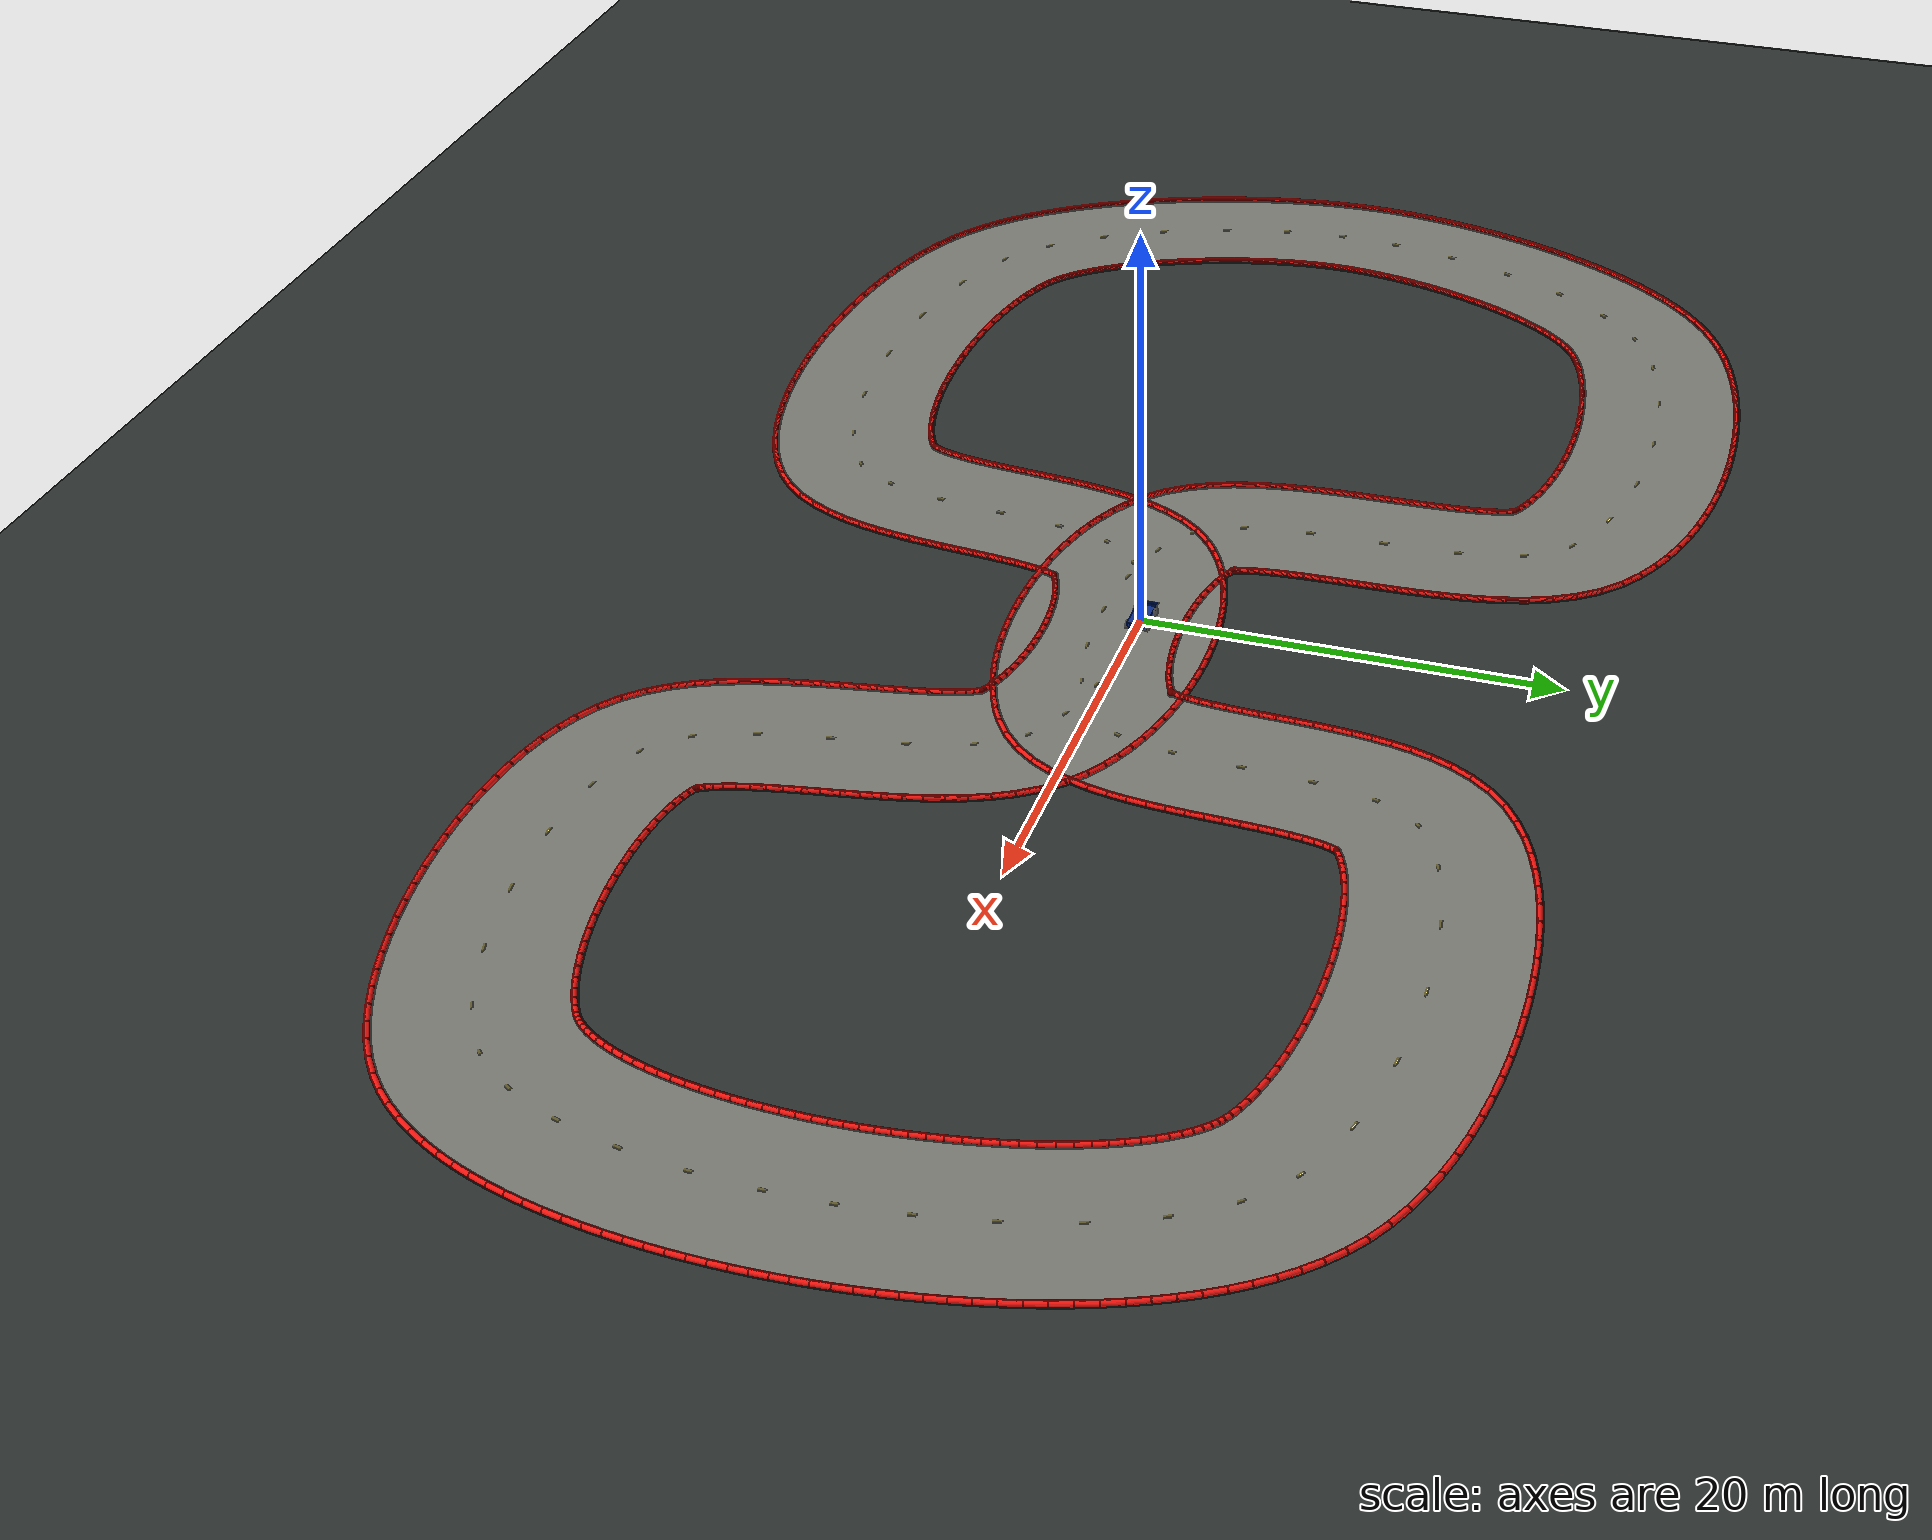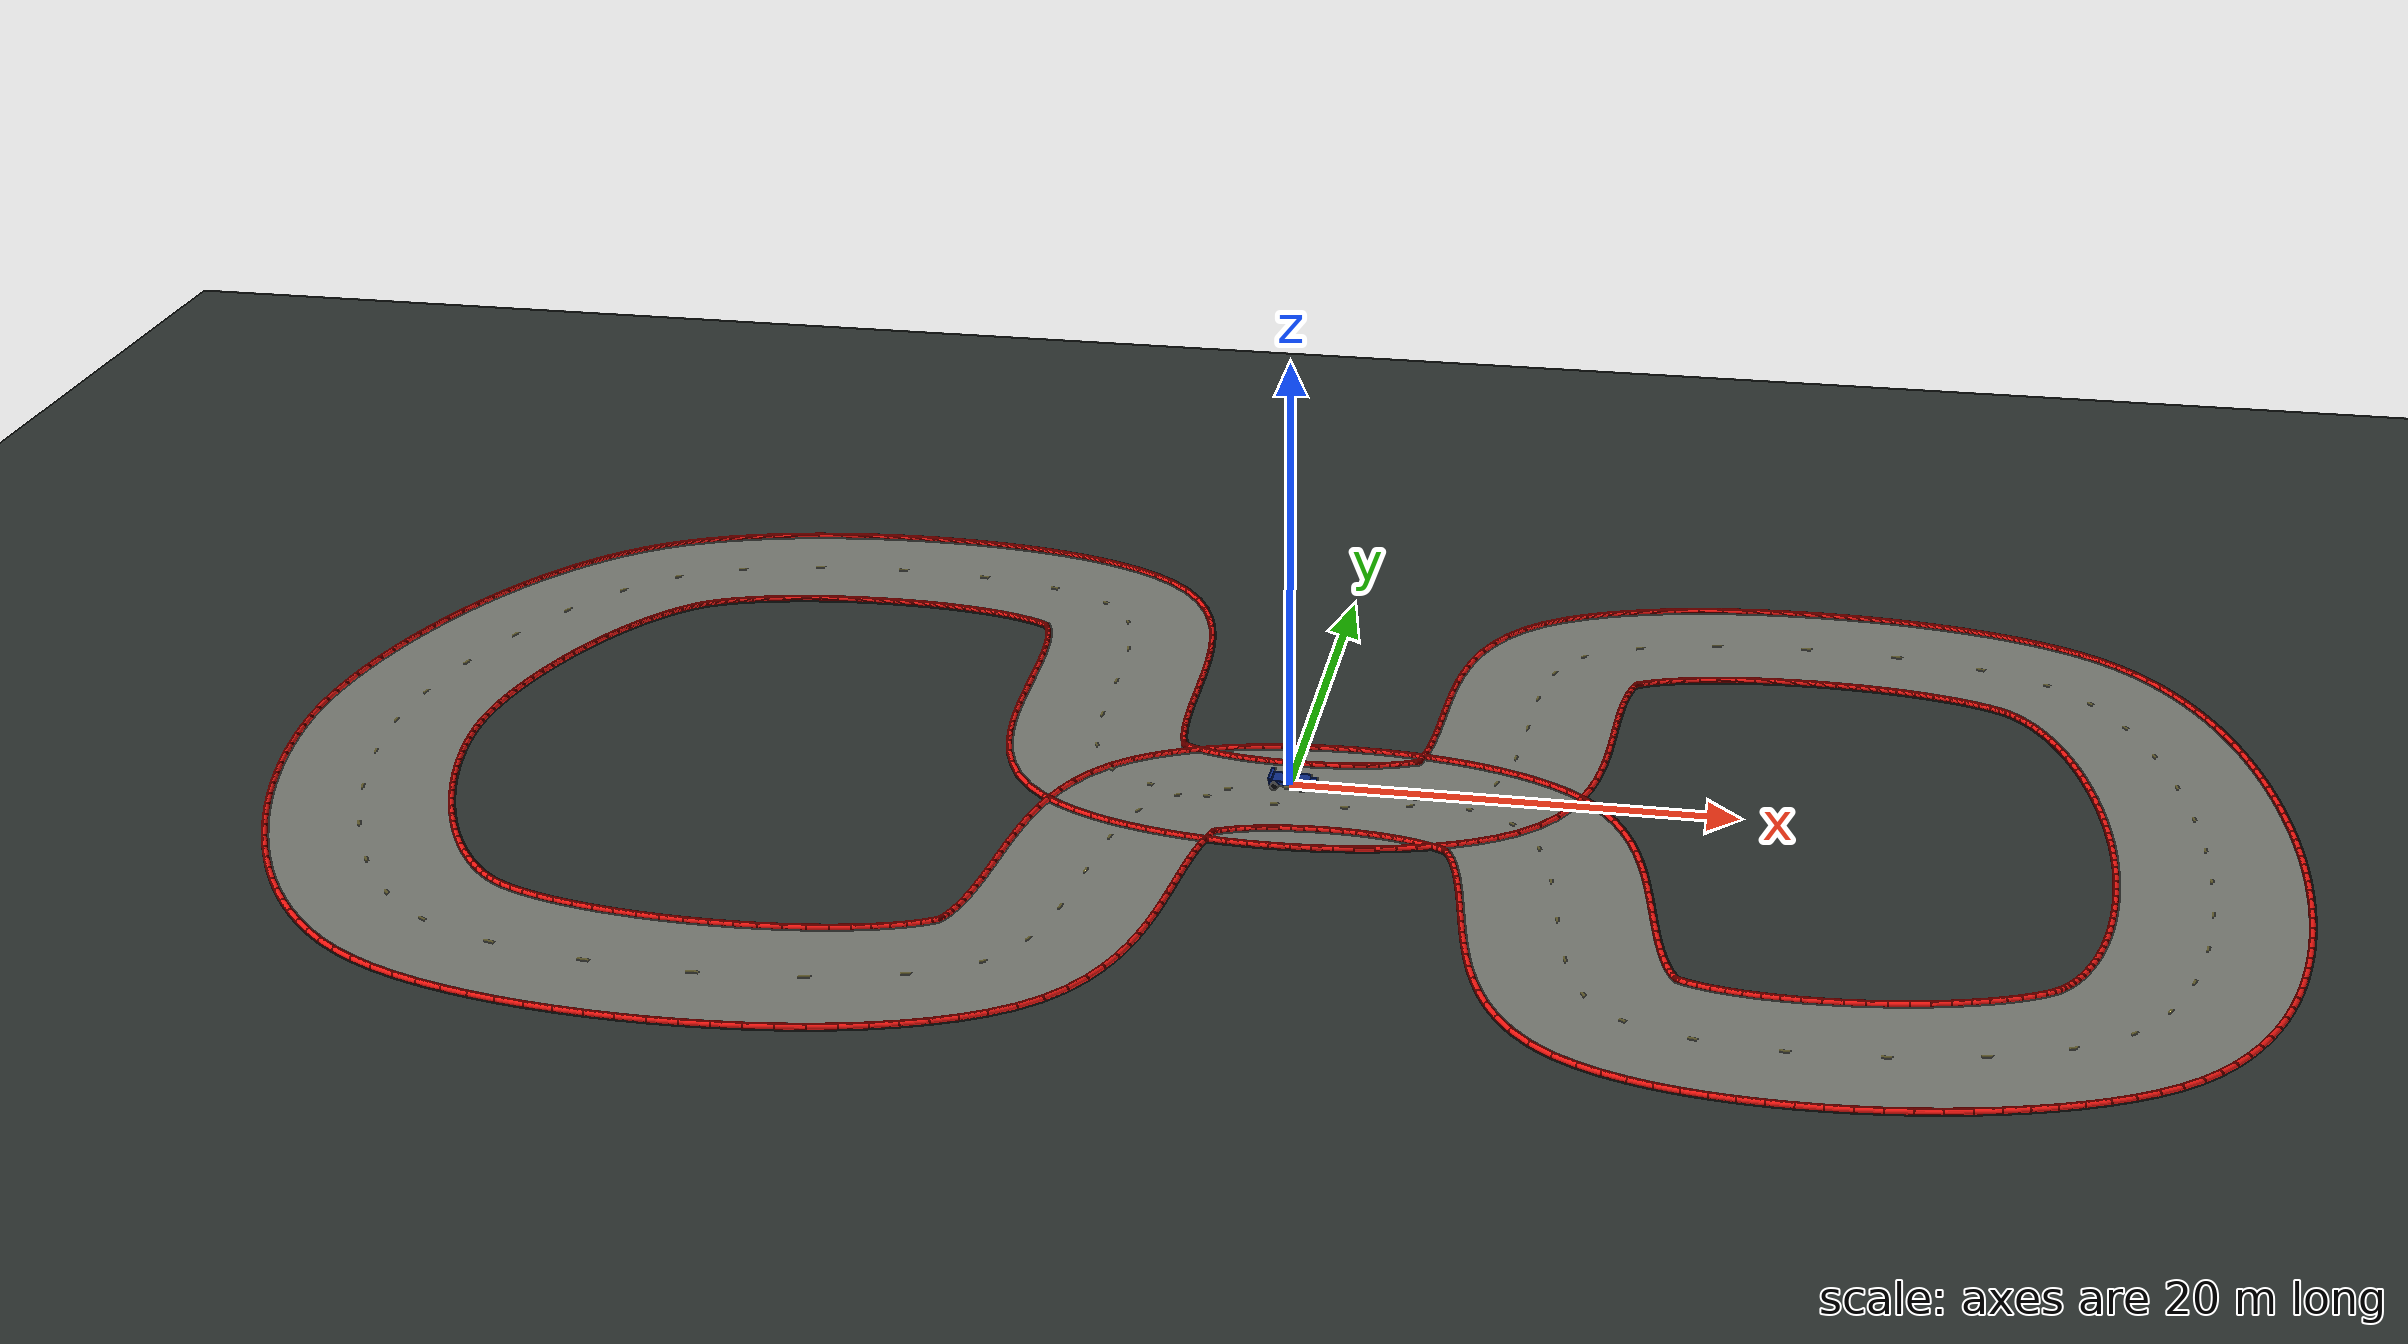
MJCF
<mujoco model="racesim_stop_go_world">
  <compiler angle="degree" autolimits="true"/>
  <option timestep="0.02" gravity="0 0 -9.81"/>
  <visual>
    <global offwidth="1280" offheight="960"/>
    <headlight ambient="0.35 0.35 0.35" diffuse="0.8 0.8 0.8"/>
  </visual>

  <include file="car.xml"/>
  <include file="stop_go_track.xml"/>

  <asset>
    <texture name="grid" type="2d" builtin="checker" width="512" height="512"
             rgb1="0.16 0.18 0.17" rgb2="0.20 0.22 0.21"/>
    <material name="ground" texture="grid" texrepeat="12 12" reflectance="0.05"/>
  </asset>

  <worldbody>
    <light name="sun" pos="0 0 30" dir="0 0 -1" diffuse="1.0 1.0 1.0" ambient="0.25 0.25 0.25"/>
    <geom name="ground" type="plane" size="90 90 0.1" material="ground"/>
    <camera name="topdown" pos="0 0 125" xyaxes="1 0 0 0 1 0" fovy="42"/>
    <camera name="follow" mode="trackcom" target="car" pos="-5 0 3" xyaxes="0 -1 0 0.5 0 0.866"/>
  </worldbody>
</mujoco>

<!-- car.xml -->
<mujoco model="simple_car">
  <default>
    <geom friction="1.2 0.02 0.001" density="600"/>
    <joint damping="0.1"/>
  </default>

  <asset>
    <material name="chassis_blue" rgba="0.05 0.18 0.55 1"/>
    <material name="wheel_dark" rgba="0.02 0.02 0.025 1"/>
  </asset>

  <worldbody>
    <body name="car" pos="0 0 0.28">
      <freejoint name="root"/>
      <geom name="chassis" type="box" size="0.9 0.45 0.12" material="chassis_blue"/>
      <geom name="nose" type="box" pos="0.75 0 0.02" size="0.45 0.25 0.06" material="chassis_blue"/>
      <geom name="rear_wing" type="box" pos="-0.85 0 0.22" size="0.08 0.55 0.04" material="chassis_blue"/>

      <body name="front_left_wheel" pos="0.65 0.48 -0.12">
        <joint name="front_left_spin" type="hinge" axis="0 1 0"/>
        <geom type="cylinder" size="0.18 0.08" euler="90 0 0" material="wheel_dark"/>
      </body>
      <body name="front_right_wheel" pos="0.65 -0.48 -0.12">
        <joint name="front_right_spin" type="hinge" axis="0 1 0"/>
        <geom type="cylinder" size="0.18 0.08" euler="90 0 0" material="wheel_dark"/>
      </body>
      <body name="rear_left_wheel" pos="-0.65 0.48 -0.12">
        <joint name="rear_left_spin" type="hinge" axis="0 1 0"/>
        <geom type="cylinder" size="0.18 0.08" euler="90 0 0" material="wheel_dark"/>
      </body>
      <body name="rear_right_wheel" pos="-0.65 -0.48 -0.12">
        <joint name="rear_right_spin" type="hinge" axis="0 1 0"/>
        <geom type="cylinder" size="0.18 0.08" euler="90 0 0" material="wheel_dark"/>
      </body>
    </body>
  </worldbody>
</mujoco>

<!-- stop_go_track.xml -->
<mujoco model="stop_go_track_visuals">
  <asset>
    <mesh name="track_surface_mesh" inertia="shell" vertex="36.00645 -0.22706 0.02200 35.96600 0.38612 0.02200 35.91275 1.02197 0.02200 35.84627 1.67602 0.02200 35.76618 2.34431 0.02200 35.67215 3.02294 0.02200 35.56389 3.70801 0.02200 35.44118 4.39566 0.02200 35.30389 5.08201 0.02200 35.15195 5.76315 0.02200 34.98542 6.43513 0.02200 34.80448 7.09397 0.02200 34.60947 7.73561 0.02200 34.40094 8.35596 0.02200 34.17969 8.95090 0.02200 33.94680 9.51626 0.02200 33.70376 10.04793 0.02200 33.45247 10.54186 0.02200 33.19536 10.99426 0.02200 32.93539 11.40169 0.02200 32.67611 11.76138 0.02200 32.42151 12.07153 0.02200 32.17576 12.33173 0.02200 31.94274 12.54335 0.02200 31.73296 12.70447 0.02200 31.42575 12.89387 0.02200 31.01355 13.09914 0.02200 30.48820 13.31466 0.02200 29.86424 13.52667 0.02200 29.15575 13.72609 0.02200 28.37590 13.90686 0.02200 27.53690 14.06494 0.02200 26.65015 14.19757 0.02200 25.72645 14.30288 0.02200 24.77612 14.37959 0.02200 23.80919 14.42688 0.02200 22.83550 14.44427 0.02200 21.86481 14.43157 0.02200 20.90696 14.38891 0.02200 19.97190 14.31671 0.02200 19.06989 14.21582 0.02200 18.21160 14.08762 0.02200 17.40830 13.93424 0.02200 16.67203 13.75898 0.02200 16.01576 13.56684 0.02200 15.45350 13.36549 0.02200 15.00000 13.16666 0.02200 14.66960 12.98816 0.02200 14.50698 12.88311 0.02200 14.53935 12.91689 0.02200 14.55561 12.93220 0.02200 14.51085 12.84613 0.02200 14.42755 12.64041 0.02200 14.32836 12.31571 0.02200 14.22967 11.88272 0.02200 14.14110 11.35574 0.02200 14.06694 10.74928 0.02200 14.00780 10.07669 0.02200 13.96192 9.34976 0.02200 13.92594 8.57876 0.02200 13.89545 7.77248 0.02200 13.86524 6.93833 0.02200 13.82939 6.08239 0.02200 13.78123 5.20929 0.02200 13.71306 4.32210 0.02200 13.61564 3.42208 0.02200 13.47733 2.50854 0.02200 13.28264 1.57890 0.02200 13.01007 0.62980 0.02200 12.62971 -0.33964 0.02200 12.10244 -1.32034 0.02200 11.38590 -2.28106 0.02200 10.52811 -3.09979 0.02200 9.68769 -3.69514 0.02200 8.88342 -4.15312 0.02200 8.06121 -4.53821 0.02200 7.22219 -4.86354 0.02200 6.36674 -5.13830 0.02200 5.49537 -5.36881 0.02200 4.60910 -5.55941 0.02200 3.70945 -5.71305 0.02200 2.79842 -5.83172 0.02200 1.87838 -5.91670 0.02200 0.95200 -5.96876 0.02200 0.02209 -5.98827 0.02200 -0.90845 -5.97523 0.02200 -1.83670 -5.92933 0.02200 -2.75988 -5.84985 0.02200 -3.67537 -5.73569 0.02200 -4.58086 -5.58517 0.02200 -5.47437 -5.39589 0.02200 -6.35440 -5.16440 0.02200 -7.21988 -4.88583 0.02200 -8.07006 -4.55322 0.02200 -8.90402 -4.15676 0.02200 -9.71958 -3.68287 0.02200 -10.57429 -3.06154 0.02200 -11.46647 -2.17838 0.02200 -12.19914 -1.14362 0.02200 -12.72786 -0.09083 0.02200 -13.10274 0.95066 0.02200 -13.36677 1.97492 0.02200 -13.55124 2.98493 0.02200 -13.67802 3.98487 0.02200 -13.76275 4.97721 0.02200 -13.81724 5.96203 0.02200 -13.85101 6.93721 0.02200 -13.87214 7.89869 0.02200 -13.88780 8.84080 0.02200 -13.90447 9.75639 0.02200 -13.92800 10.63697 0.02200 -13.96354 11.47262 0.02200 -14.01527 12.25193 0.02200 -14.08587 12.96176 0.02200 -14.17569 13.58716 0.02200 -14.28139 14.11153 0.02200 -14.39396 14.51768 0.02200 -14.49655 14.79097 0.02200 -14.56391 14.92632 0.02200 -14.56798 14.93909 0.02200 -14.55668 14.92374 0.02200 -14.72196 15.03340 0.02200 -15.05301 15.21894 0.02200 -15.49849 15.42189 0.02200 -16.04678 15.62605 0.02200 -16.68513 15.82030 0.02200 -17.40096 15.99714 0.02200 -18.18237 16.15159 0.02200 -19.01815 16.28032 0.02200 -19.89775 16.38114 0.02200 -20.81111 16.45266 0.02200 -21.74860 16.49404 0.02200 -22.70085 16.50487 0.02200 -23.65865 16.48504 0.02200 -24.61288 16.43479 0.02200 -25.55439 16.35458 0.02200 -26.47392 16.24525 0.02200 -27.36200 16.10799 0.02200 -28.20884 15.94450 0.02200 -29.00422 15.75720 0.02200 -29.73735 15.54951 0.02200 -30.39684 15.32630 0.02200 -30.97064 15.09462 0.02200 -31.44638 14.86469 0.02200 -31.82756 14.64135 0.02200 -32.14882 14.41242 0.02200 -32.49619 14.12342 0.02200 -32.86040 13.77613 0.02200 -33.23537 13.37211 0.02200 -33.61558 12.91420 0.02200 -33.99614 12.40602 0.02200 -34.37286 11.85175 0.02200 -34.74212 11.25586 0.02200 -35.10083 10.62300 0.02200 -35.44635 9.95789 0.02200 -35.77637 9.26531 0.02200 -36.08888 8.55005 0.02200 -36.38213 7.81691 0.02200 -36.65454 7.07070 0.02200 -36.90472 6.31627 0.02200 -37.13142 5.55849 0.02200 -37.33353 4.80232 0.02200 -37.51008 4.05280 0.02200 -37.66022 3.31513 0.02200 -37.78330 2.59468 0.02200 -37.87884 1.89705 0.02200 -37.94662 1.22819 0.02200 -37.98679 0.59440 0.02200 -38.00000 -0.00129 0.02200 -37.98709 -0.59878 0.02200 -37.94785 -1.23534 0.02200 -37.88165 -1.90545 0.02200 -37.78831 -2.60303 0.02200 -37.66797 -3.32239 0.02200 -37.52103 -4.05811 0.02200 -37.34806 -4.80497 0.02200 -37.14978 -5.55795 0.02200 -36.92706 -6.31214 0.02200 -36.68091 -7.06272 0.02200 -36.41244 -7.80496 0.02200 -36.12294 -8.53412 0.02200 -35.81385 -9.24555 0.02200 -35.48681 -9.93457 0.02200 -35.14371 -10.59655 0.02200 -34.78669 -11.22689 0.02200 -34.41824 -11.82104 0.02200 -34.04127 -12.37458 0.02200 -33.65912 -12.88328 0.02200 -33.27568 -13.34325 0.02200 -32.89538 -13.75116 0.02200 -32.52317 -14.10448 0.02200 -32.16435 -14.40186 0.02200 -31.83224 -14.63833 0.02200 -31.41288 -14.88313 0.02200 -30.89262 -15.13126 0.02200 -30.26363 -15.37995 0.02200 -29.53951 -15.61819 0.02200 -28.73346 -15.83851 0.02200 -27.85797 -16.03588 0.02200 -26.92480 -16.20687 0.02200 -25.94507 -16.34916 0.02200 -24.92940 -16.46115 0.02200 -23.88802 -16.54179 0.02200 -22.83094 -16.59042 0.02200 -21.76797 -16.60669 0.02200 -20.70890 -16.59052 0.02200 -19.66356 -16.54213 0.02200 -18.64191 -16.46199 0.02200 -17.65416 -16.35098 0.02200 -16.71091 -16.21043 0.02200 -15.82327 -16.04236 0.02200 -15.00304 -15.84979 0.02200 -14.26287 -15.63722 0.02200 -13.61633 -15.41143 0.02200 -13.07781 -15.18265 0.02200 -12.66166 -14.96629 0.02200 -12.41239 -14.80933 0.02200 -12.38899 -14.79208 0.02200 -12.36192 -14.75549 0.02200 -12.28433 -14.62868 0.02200 -12.17228 -14.39487 0.02200 -12.04374 -14.05263 0.02200 -11.91283 -13.60967 0.02200 -11.78843 -13.07772 0.02200 -11.67498 -12.46945 0.02200 -11.57356 -11.79701 0.02200 -11.48299 -11.07145 0.02200 -11.40046 -10.30260 0.02200 -11.32207 -9.49904 0.02200 -11.24301 -8.66810 0.02200 -11.15774 -7.81590 0.02200 -11.05982 -6.94723 0.02200 -10.94178 -6.06543 0.02200 -10.79454 -5.17227 0.02200 -10.60663 -4.26779 0.02200 -10.36288 -3.35060 0.02200 -10.04259 -2.41894 0.02200 -9.61752 -1.47389 0.02200 -9.05173 -0.52604 0.02200 -8.30729 0.39414 0.02200 -7.44073 1.16904 0.02200 -6.63021 1.71531 0.02200 -5.86482 2.13642 0.02200 -5.08348 2.49380 0.02200 -4.28800 2.79701 0.02200 -3.47939 3.05318 0.02200 -2.65852 3.26751 0.02200 -1.82640 3.44379 0.02200 -0.98432 3.58473 0.02200 -0.13383 3.69229 0.02200 0.72324 3.76781 0.02200 1.58491 3.81222 0.02200 2.44904 3.82607 0.02200 3.31340 3.80962 0.02200 4.17577 3.76281 0.02200 5.03395 3.68531 0.02200 5.88585 3.57644 0.02200 6.72953 3.43515 0.02200 7.56326 3.25985 0.02200 8.38557 3.04828 0.02200 9.19525 2.79729 0.02200 9.99128 2.50250 0.02200 10.77268 2.15785 0.02200 11.53800 1.75514 0.02200 12.35175 1.23563 0.02200 13.23729 0.49230 0.02200 14.01366 -0.39582 0.02200 14.62215 -1.31793 0.02200 15.09827 -2.24652 0.02200 15.47494 -3.17108 0.02200 15.77798 -4.08916 0.02200 16.02653 -5.00070 0.02200 16.23473 -5.90540 0.02200 16.41334 -6.80175 0.02200 16.57086 -7.68679 0.02200 16.71428 -8.55613 0.02200 16.84953 -9.40412 0.02200 16.98167 -10.22389 0.02200 17.11494 -11.00739 0.02200 17.25269 -11.74537 0.02200 17.39710 -12.42732 0.02200 17.54863 -13.04144 0.02200 17.70531 -13.57466 0.02200 17.86151 -14.01317 0.02200 18.00649 -14.34383 0.02200 18.12327 -14.55744 0.02200 18.18962 -14.65484 0.02200 18.18472 -14.65490 0.02200 18.16493 -14.63651 0.02200 18.31920 -14.71436 0.02200 18.63583 -14.84696 0.02200 19.06151 -14.98644 0.02200 19.58279 -15.11865 0.02200 20.18607 -15.23442 0.02200 20.85849 -15.32800 0.02200 21.58817 -15.39586 0.02200 22.36412 -15.43598 0.02200 23.17608 -15.44730 0.02200 24.01437 -15.42947 0.02200 24.86969 -15.38259 0.02200 25.73307 -15.30717 0.02200 26.59567 -15.20401 0.02200 27.44873 -15.07420 0.02200 28.28344 -14.91915 0.02200 29.09086 -14.74064 0.02200 29.86181 -14.54091 0.02200 30.58673 -14.32286 0.02200 31.25563 -14.09031 0.02200 31.85791 -13.84840 0.02200 32.38237 -13.60423 0.02200 32.81740 -13.36784 0.02200 33.15161 -13.15348 0.02200 33.39229 -12.96688 0.02200 33.55862 -12.80797 0.02200 33.74323 -12.59932 0.02200 33.93806 -12.34133 0.02200 34.13871 -12.03286 0.02200 34.34071 -11.67467 0.02200 34.53999 -11.26892 0.02200 34.73310 -10.81875 0.02200 34.91728 -10.32784 0.02200 35.09039 -9.80022 0.02200 35.25085 -9.24002 0.02200 35.39755 -8.65146 0.02200 35.52977 -8.03869 0.02200 35.64707 -7.40583 0.02200 35.74929 -6.75690 0.02200 35.83645 -6.09585 0.02200 35.90873 -5.42657 0.02200 35.96644 -4.75288 0.02200 36.00999 -4.07853 0.02200 36.03988 -3.40726 0.02200 36.05668 -2.74278 0.02200 36.06101 -2.08880 0.02200 36.05358 -1.44906 0.02200 36.03513 -0.82733 0.02200 43.99355 0.22706 0.02200 43.94369 0.98321 0.02200 43.87860 1.76035 0.02200 43.79766 2.55657 0.02200 43.70023 3.36946 0.02200 43.58560 4.19654 0.02200 43.45301 5.03530 0.02200 43.30166 5.88325 0.02200 43.13065 6.73787 0.02200 42.93900 7.59670 0.02200 42.72563 8.45731 0.02200 42.48932 9.31730 0.02200 42.22870 10.17434 0.02200 41.94217 11.02613 0.02200 41.62792 11.87044 0.02200 41.28381 12.70503 0.02200 40.90734 13.52765 0.02200 40.49555 14.33594 0.02200 40.04500 15.12735 0.02200 39.55167 15.89890 0.02200 39.01100 16.64700 0.02200 38.41795 17.36707 0.02200 37.76732 18.05314 0.02200 37.05420 18.69745 0.02200 36.26704 19.29553 0.02200 35.32795 19.87763 0.02200 34.33209 20.37838 0.02200 33.30274 20.80321 0.02200 32.24044 21.16563 0.02200 31.14620 21.47451 0.02200 30.02197 21.73569 0.02200 28.87062 21.95298 0.02200 27.69584 22.12894 0.02200 26.50194 22.26520 0.02200 25.29368 22.36283 0.02200 24.07613 22.42243 0.02200 22.85456 22.44425 0.02200 21.63428 22.42825 0.02200 20.42058 22.37411 0.02200 19.21857 22.28117 0.02200 18.03311 22.14836 0.02200 16.86861 21.97409 0.02200 15.72891 21.75598 0.02200 14.61706 21.49055 0.02200 13.53518 21.17254 0.02200 12.48436 20.79410 0.02200 11.46495 20.34324 0.02200 10.47769 19.80196 0.02200 9.49302 19.11689 0.02200 8.61341 18.29120 0.02200 7.87832 17.33831 0.02200 7.32123 16.35460 0.02200 6.90826 15.37176 0.02200 6.60534 14.40258 0.02200 6.38466 13.44980 0.02200 6.22518 12.51256 0.02200 6.11121 11.58980 0.02200 6.03071 10.68162 0.02200 5.97402 9.78964 0.02200 5.93310 8.91707 0.02200 5.90093 8.06855 0.02200 5.87132 7.25009 0.02200 5.83874 6.46908 0.02200 5.79848 5.73432 0.02200 5.74681 5.05619 0.02200 5.68155 4.44686 0.02200 5.60292 3.92048 0.02200 5.51501 3.49305 0.02200 5.42789 3.18138 0.02200 5.36005 2.99981 0.02200 5.33921 2.95267 0.02200 5.39629 3.02220 0.02200 5.47189 3.09979 0.02200 5.41728 3.06974 0.02200 5.21265 2.95501 0.02200 4.92238 2.82031 0.02200 4.55570 2.67900 0.02200 4.12257 2.54049 0.02200 3.63280 2.41135 0.02200 3.09570 2.29614 0.02200 2.52009 2.19804 0.02200 1.91431 2.11928 0.02200 1.28630 2.06136 0.02200 0.64375 2.02530 0.02200 -0.00583 2.01168 0.02200 -0.65502 2.02075 0.02200 -1.29638 2.05241 0.02200 -1.92237 2.10619 0.02200 -2.52527 2.18121 0.02200 -3.09708 2.27603 0.02200 -3.62942 2.38847 0.02200 -4.11346 2.51532 0.02200 -4.53995 2.65194 0.02200 -4.89931 2.79160 0.02200 -5.18211 2.92473 0.02200 -5.38020 3.03797 0.02200 -5.42571 3.06154 0.02200 -5.36329 2.99378 0.02200 -5.32467 2.94804 0.02200 -5.36693 3.04233 0.02200 -5.45255 3.29043 0.02200 -5.55118 3.68270 0.02200 -5.64414 4.20060 0.02200 -5.72219 4.82440 0.02200 -5.78229 5.53609 0.02200 -5.82525 6.32001 0.02200 -5.85419 7.16272 0.02200 -5.87363 8.05273 0.02200 -5.88901 8.98017 0.02200 -5.90650 9.93661 0.02200 -5.93283 10.91498 0.02200 -5.97549 11.90966 0.02200 -6.04292 12.91649 0.02200 -6.14505 13.93306 0.02200 -6.29415 14.95876 0.02200 -6.50618 15.99463 0.02200 -6.80277 17.04231 0.02200 -7.21338 18.10087 0.02200 -7.77589 19.15985 0.02200 -8.53097 20.18832 0.02200 -9.44332 21.07626 0.02200 -10.43010 21.78469 0.02200 -11.41324 22.34299 0.02200 -12.43006 22.81004 0.02200 -13.47815 23.20247 0.02200 -14.55622 23.53183 0.02200 -15.66281 23.80604 0.02200 -16.79582 24.03052 0.02200 -17.95240 24.20901 0.02200 -19.12909 24.34412 0.02200 -20.32190 24.43769 0.02200 -21.52643 24.49095 0.02200 -22.73803 24.50478 0.02200 -23.95187 24.47967 0.02200 -25.16305 24.41585 0.02200 -26.36668 24.31324 0.02200 -27.55798 24.17146 0.02200 -28.73241 23.98974 0.02200 -29.88571 23.76678 0.02200 -31.01407 23.50062 0.02200 -32.11426 23.18825 0.02200 -33.18363 22.82522 0.02200 -34.22021 22.40491 0.02200 -35.22231 21.91752 0.02200 -36.17244 21.35865 0.02200 -37.02138 20.75735 0.02200 -37.81169 20.10217 0.02200 -38.55109 19.39894 0.02200 -39.24414 18.65366 0.02200 -39.89481 17.87113 0.02200 -40.50646 17.05530 0.02200 -41.08175 16.20959 0.02200 -41.62276 15.33713 0.02200 -42.13104 14.44087 0.02200 -42.60771 13.52369 0.02200 -43.05354 12.58839 0.02200 -43.46898 11.63779 0.02200 -43.85429 10.67468 0.02200 -44.20948 9.70185 0.02200 -44.53441 8.72205 0.02200 -44.82880 7.73801 0.02200 -45.09223 6.75235 0.02200 -45.32412 5.76764 0.02200 -45.52380 4.78627 0.02200 -45.69038 3.81048 0.02200 -45.82280 2.84224 0.02200 -45.91976 1.88323 0.02200 -45.97955 0.93472 0.02200 -46.00000 0.00129 0.02200 -45.98025 -0.92969 0.02200 -45.92235 -1.87359 0.02200 -45.82822 -2.82850 0.02200 -45.69930 -3.79307 0.02200 -45.53672 -4.76557 0.02200 -45.34137 -5.74401 0.02200 -45.11395 -6.72614 0.02200 -44.85500 -7.70959 0.02200 -44.56494 -8.69182 0.02200 -44.24403 -9.67024 0.02200 -43.89243 -10.64215 0.02200 -43.51013 -11.60484 0.02200 -43.09696 -12.55557 0.02200 -42.65255 -13.49157 0.02200 -42.17629 -14.41005 0.02200 -41.66732 -15.30818 0.02200 -41.12440 -16.18308 0.02200 -40.54593 -17.03176 0.02200 -39.92982 -17.85100 0.02200 -39.27346 -18.63727 0.02200 -38.57369 -19.38648 0.02200 -37.82683 -20.09374 0.02200 -37.02888 -20.75295 0.02200 -36.16776 -21.36167 0.02200 -35.16359 -21.94940 0.02200 -34.09706 -22.46144 0.02200 -32.99140 -22.90055 0.02200 -31.84847 -23.27774 0.02200 -30.67048 -23.60046 0.02200 -29.46038 -23.87375 0.02200 -28.22182 -24.10103 0.02200 -26.95913 -24.28463 0.02200 -25.67710 -24.42613 0.02200 -24.38094 -24.52659 0.02200 -23.07607 -24.58666 0.02200 -21.76810 -24.60669 0.02200 -20.46268 -24.58673 0.02200 -19.16540 -24.52660 0.02200 -17.88173 -24.42579 0.02200 -16.61688 -24.28345 0.02200 -15.37570 -24.09822 0.02200 -14.16249 -23.86807 0.02200 -12.98089 -23.59000 0.02200 -11.83368 -23.25949 0.02200 -10.72270 -22.86977 0.02200 -9.64900 -22.41060 0.02200 -8.61367 -21.86656 0.02200 -7.58761 -21.19067 0.02200 -6.68825 -20.40471 0.02200 -5.91574 -19.49329 0.02200 -5.30610 -18.54073 0.02200 -4.83251 -17.57729 0.02200 -4.46617 -16.61786 0.02200 -4.18220 -15.66817 0.02200 -3.96091 -14.72997 0.02200 -3.78708 -13.80405 0.02200 -3.64882 -12.89172 0.02200 -3.53652 -11.99537 0.02200 -3.44219 -11.11866 0.02200 -3.35896 -10.26645 0.02200 -3.28081 -9.44488 0.02200 -3.20253 -8.66129 0.02200 -3.11972 -7.92435 0.02200 -3.02909 -7.24416 0.02200 -2.92892 -6.63245 0.02200 -2.81988 -6.10260 0.02200 -2.70633 -5.66950 0.02200 -2.59821 -5.34833 0.02200 -2.51294 -5.15151 0.02200 -2.47569 -5.08188 0.02200 -2.51356 -5.12244 0.02200 -2.55927 -5.16904 0.02200 -2.48679 -5.12809 0.02200 -2.27660 -5.01373 0.02200 -1.99807 -4.88727 0.02200 -1.65764 -4.75820 0.02200 -1.26259 -4.63355 0.02200 -0.82032 -4.51844 0.02200 -0.33808 -4.41655 0.02200 0.17714 -4.33051 0.02200 0.71862 -4.26217 0.02200 1.27992 -4.21280 0.02200 1.85474 -4.18323 0.02200 2.43697 -4.17392 0.02200 3.02054 -4.18502 0.02200 3.59942 -4.21640 0.02200 4.16752 -4.26764 0.02200 4.71868 -4.33795 0.02200 5.24655 -4.42620 0.02200 5.74459 -4.53069 0.02200 6.20601 -4.64909 0.02200 6.62374 -4.77815 0.02200 6.99052 -4.91339 0.02200 7.29908 -5.04868 0.02200 7.54258 -5.17570 0.02200 7.64825 -5.23563 0.02200 7.63838 -5.22191 0.02200 7.63412 -5.22297 0.02200 7.70385 -5.33502 0.02200 7.82173 -5.57095 0.02200 7.96450 -5.92669 0.02200 8.11601 -6.39007 0.02200 8.26679 -6.94657 0.02200 8.41236 -7.58187 0.02200 8.55164 -8.28288 0.02200 8.68579 -9.03797 0.02200 8.81747 -9.83692 0.02200 8.95044 -10.67078 0.02200 9.08931 -11.53182 0.02200 9.23948 -12.41349 0.02200 9.40728 -13.31044 0.02200 9.60021 -14.21857 0.02200 9.82745 -15.13509 0.02200 10.10066 -16.05845 0.02200 10.43513 -16.98789 0.02200 10.85126 -17.92192 0.02200 11.37571 -18.85516 0.02200 12.04037 -19.77214 0.02200 12.87572 -20.63942 0.02200 13.83507 -21.36349 0.02200 14.83741 -21.91693 0.02200 15.81848 -22.33445 0.02200 16.81841 -22.66554 0.02200 17.83745 -22.92594 0.02200 18.87601 -23.12643 0.02200 19.93374 -23.27437 0.02200 21.00935 -23.37490 0.02200 22.10064 -23.43164 0.02200 23.20466 -23.44725 0.02200 24.31792 -23.42370 0.02200 25.43650 -23.36249 0.02200 26.55621 -23.26471 0.02200 27.67267 -23.13118 0.02200 28.78147 -22.96240 0.02200 29.87821 -22.75858 0.02200 30.95865 -22.51954 0.02200 32.01878 -22.24464 0.02200 33.05495 -21.93259 0.02200 34.06398 -21.58118 0.02200 35.04327 -21.18689 0.02200 35.99082 -20.74419 0.02200 36.90506 -20.24468 0.02200 37.78419 -19.67569 0.02200 38.60771 -19.03312 0.02200 39.30453 -18.37435 0.02200 39.92551 -17.67666 0.02200 40.48027 -16.94563 0.02200 40.97477 -16.18838 0.02200 41.41505 -15.41012 0.02200 41.80677 -14.61465 0.02200 42.15491 -13.80484 0.02200 42.46383 -12.98295 0.02200 42.73722 -12.15095 0.02200 42.97823 -11.31067 0.02200 43.18955 -10.46387 0.02200 43.37346 -9.61236 0.02200 43.53197 -8.75803 0.02200 43.66680 -7.90280 0.02200 43.77950 -7.04871 0.02200 43.87146 -6.19785 0.02200 43.94395 -5.35237 0.02200 43.99810 -4.51448 0.02200 44.03501 -3.68644 0.02200 44.05566 -2.87049 0.02200 44.06099 -2.06891 0.02200 44.05188 -1.28394 0.02200 44.02914 -0.51777 0.02200" face="0 337 1 0 336 337 1 338 2 1 337 338 2 339 3 2 338 339 3 340 4 3 339 340 4 341 5 4 340 341 5 342 6 5 341 342 6 343 7 6 342 343 7 344 8 7 343 344 8 345 9 8 344 345 9 346 10 9 345 346 10 347 11 10 346 347 11 348 12 11 347 348 12 349 13 12 348 349 13 350 14 13 349 350 14 351 15 14 350 351 15 352 16 15 351 352 16 353 17 16 352 353 17 354 18 17 353 354 18 355 19 18 354 355 19 356 20 19 355 356 20 357 21 20 356 357 21 358 22 21 357 358 22 359 23 22 358 359 23 360 24 23 359 360 24 361 25 24 360 361 25 362 26 25 361 362 26 363 27 26 362 363 27 364 28 27 363 364 28 365 29 28 364 365 29 366 30 29 365 366 30 367 31 30 366 367 31 368 32 31 367 368 32 369 33 32 368 369 33 370 34 33 369 370 34 371 35 34 370 371 35 372 36 35 371 372 36 373 37 36 372 373 37 374 38 37 373 374 38 375 39 38 374 375 39 376 40 39 375 376 40 377 41 40 376 377 41 378 42 41 377 378 42 379 43 42 378 379 43 380 44 43 379 380 44 381 45 44 380 381 45 382 46 45 381 382 46 383 47 46 382 383 47 384 48 47 383 384 48 385 49 48 384 385 49 386 50 49 385 386 50 387 51 50 386 387 51 388 52 51 387 388 52 389 53 52 388 389 53 390 54 53 389 390 54 391 55 54 390 391 55 392 56 55 391 392 56 393 57 56 392 393 57 394 58 57 393 394 58 395 59 58 394 395 59 396 60 59 395 396 60 397 61 60 396 397 61 398 62 61 397 398 62 399 63 62 398 399 63 400 64 63 399 400 64 401 65 64 400 401 65 402 66 65 401 402 66 403 67 66 402 403 67 404 68 67 403 404 68 405 69 68 404 405 69 406 70 69 405 406 70 407 71 70 406 407 71 408 72 71 407 408 72 409 73 72 408 409 73 410 74 73 409 410 74 411 75 74 410 411 75 412 76 75 411 412 76 413 77 76 412 413 77 414 78 77 413 414 78 415 79 78 414 415 79 416 80 79 415 416 80 417 81 80 416 417 81 418 82 81 417 418 82 419 83 82 418 419 83 420 84 83 419 420 84 421 85 84 420 421 85 422 86 85 421 422 86 423 87 86 422 423 87 424 88 87 423 424 88 425 89 88 424 425 89 426 90 89 425 426 90 427 91 90 426 427 91 428 92 91 427 428 92 429 93 92 428 429 93 430 94 93 429 430 94 431 95 94 430 431 95 432 96 95 431 432 96 433 97 96 432 433 97 434 98 97 433 434 98 435 99 98 434 435 99 436 100 99 435 436 100 437 101 100 436 437 101 438 102 101 437 438 102 439 103 102 438 439 103 440 104 103 439 440 104 441 105 104 440 441 105 442 106 105 441 442 106 443 107 106 442 443 107 444 108 107 443 444 108 445 109 108 444 445 109 446 110 109 445 446 110 447 111 110 446 447 111 448 112 111 447 448 112 449 113 112 448 449 113 450 114 113 449 450 114 451 115 114 450 451 115 452 116 115 451 452 116 453 117 116 452 453 117 454 118 117 453 454 118 455 119 118 454 455 119 456 120 119 455 456 120 457 121 120 456 457 121 458 122 121 457 458 122 459 123 122 458 459 123 460 124 123 459 460 124 461 125 124 460 461 125 462 126 125 461 462 126 463 127 126 462 463 127 464 128 127 463 464 128 465 129 128 464 465 129 466 130 129 465 466 130 467 131 130 466 467 131 468 132 131 467 468 132 469 133 132 468 469 133 470 134 133 469 470 134 471 135 134 470 471 135 472 136 135 471 472 136 473 137 136 472 473 137 474 138 137 473 474 138 475 139 138 474 475 139 476 140 139 475 476 140 477 141 140 476 477 141 478 142 141 477 478 142 479 143 142 478 479 143 480 144 143 479 480 144 481 145 144 480 481 145 482 146 145 481 482 146 483 147 146 482 483 147 484 148 147 483 484 148 485 149 148 484 485 149 486 150 149 485 486 150 487 151 150 486 487 151 488 152 151 487 488 152 489 153 152 488 489 153 490 154 153 489 490 154 491 155 154 490 491 155 492 156 155 491 492 156 493 157 156 492 493 157 494 158 157 493 494 158 495 159 158 494 495 159 496 160 159 495 496 160 497 161 160 496 497 161 498 162 161 497 498 162 499 163 162 498 499 163 500 164 163 499 500 164 501 165 164 500 501 165 502 166 165 501 502 166 503 167 166 502 503 167 504 168 167 503 504 168 505 169 168 504 505 169 506 170 169 505 506 170 507 171 170 506 507 171 508 172 171 507 508 172 509 173 172 508 509 173 510 174 173 509 510 174 511 175 174 510 511 175 512 176 175 511 512 176 513 177 176 512 513 177 514 178 177 513 514 178 515 179 178 514 515 179 516 180 179 515 516 180 517 181 180 516 517 181 518 182 181 517 518 182 519 183 182 518 519 183 520 184 183 519 520 184 521 185 184 520 521 185 522 186 185 521 522 186 523 187 186 522 523 187 524 188 187 523 524 188 525 189 188 524 525 189 526 190 189 525 526 190 527 191 190 526 527 191 528 192 191 527 528 192 529 193 192 528 529 193 530 194 193 529 530 194 531 195 194 530 531 195 532 196 195 531 532 196 533 197 196 532 533 197 534 198 197 533 534 198 535 199 198 534 535 199 536 200 199 535 536 200 537 201 200 536 537 201 538 202 201 537 538 202 539 203 202 538 539 203 540 204 203 539 540 204 541 205 204 540 541 205 542 206 205 541 542 206 543 207 206 542 543 207 544 208 207 543 544 208 545 209 208 544 545 209 546 210 209 545 546 210 547 211 210 546 547 211 548 212 211 547 548 212 549 213 212 548 549 213 550 214 213 549 550 214 551 215 214 550 551 215 552 216 215 551 552 216 553 217 216 552 553 217 554 218 217 553 554 218 555 219 218 554 555 219 556 220 219 555 556 220 557 221 220 556 557 221 558 222 221 557 558 222 559 223 222 558 559 223 560 224 223 559 560 224 561 225 224 560 561 225 562 226 225 561 562 226 563 227 226 562 563 227 564 228 227 563 564 228 565 229 228 564 565 229 566 230 229 565 566 230 567 231 230 566 567 231 568 232 231 567 568 232 569 233 232 568 569 233 570 234 233 569 570 234 571 235 234 570 571 235 572 236 235 571 572 236 573 237 236 572 573 237 574 238 237 573 574 238 575 239 238 574 575 239 576 240 239 575 576 240 577 241 240 576 577 241 578 242 241 577 578 242 579 243 242 578 579 243 580 244 243 579 580 244 581 245 244 580 581 245 582 246 245 581 582 246 583 247 246 582 583 247 584 248 247 583 584 248 585 249 248 584 585 249 586 250 249 585 586 250 587 251 250 586 587 251 588 252 251 587 588 252 589 253 252 588 589 253 590 254 253 589 590 254 591 255 254 590 591 255 592 256 255 591 592 256 593 257 256 592 593 257 594 258 257 593 594 258 595 259 258 594 595 259 596 260 259 595 596 260 597 261 260 596 597 261 598 262 261 597 598 262 599 263 262 598 599 263 600 264 263 599 600 264 601 265 264 600 601 265 602 266 265 601 602 266 603 267 266 602 603 267 604 268 267 603 604 268 605 269 268 604 605 269 606 270 269 605 606 270 607 271 270 606 607 271 608 272 271 607 608 272 609 273 272 608 609 273 610 274 273 609 610 274 611 275 274 610 611 275 612 276 275 611 612 276 613 277 276 612 613 277 614 278 277 613 614 278 615 279 278 614 615 279 616 280 279 615 616 280 617 281 280 616 617 281 618 282 281 617 618 282 619 283 282 618 619 283 620 284 283 619 620 284 621 285 284 620 621 285 622 286 285 621 622 286 623 287 286 622 623 287 624 288 287 623 624 288 625 289 288 624 625 289 626 290 289 625 626 290 627 291 290 626 627 291 628 292 291 627 628 292 629 293 292 628 629 293 630 294 293 629 630 294 631 295 294 630 631 295 632 296 295 631 632 296 633 297 296 632 633 297 634 298 297 633 634 298 635 299 298 634 635 299 636 300 299 635 636 300 637 301 300 636 637 301 638 302 301 637 638 302 639 303 302 638 639 303 640 304 303 639 640 304 641 305 304 640 641 305 642 306 305 641 642 306 643 307 306 642 643 307 644 308 307 643 644 308 645 309 308 644 645 309 646 310 309 645 646 310 647 311 310 646 647 311 648 312 311 647 648 312 649 313 312 648 649 313 650 314 313 649 650 314 651 315 314 650 651 315 652 316 315 651 652 316 653 317 316 652 653 317 654 318 317 653 654 318 655 319 318 654 655 319 656 320 319 655 656 320 657 321 320 656 657 321 658 322 321 657 658 322 659 323 322 658 659 323 660 324 323 659 660 324 661 325 324 660 661 325 662 326 325 661 662 326 663 327 326 662 663 327 664 328 327 663 664 328 665 329 328 664 665 329 666 330 329 665 666 330 667 331 330 666 667 331 668 332 331 667 668 332 669 333 332 668 669 333 670 334 333 669 670 334 671 335 334 670 671 335 336 0 335 671 336"/>
    <material name="track_asphalt" rgba="0.48 0.49 0.46 1" emission="0.08"/>
    <material name="track_boundary" rgba="0.95 0.08 0.06 1" emission="0.05"/>
    <material name="track_centerline" rgba="1.0 0.95 0.55 1" emission="0.15"/>
  </asset>
  <worldbody>
    <geom name="track_surface" type="mesh" mesh="track_surface_mesh" material="track_asphalt" contype="0" conaffinity="0"/>
    <geom name="track_left_boundary_000" type="capsule" fromto="36.00645 -0.22706 0.09 35.96600 0.38612 0.09" size="0.14" material="track_boundary" contype="0" conaffinity="0"/>
    <geom name="track_left_boundary_001" type="capsule" fromto="35.96600 0.38612 0.09 35.91275 1.02197 0.09" size="0.14" material="track_boundary" contype="0" conaffinity="0"/>
    <geom name="track_left_boundary_002" type="capsule" fromto="35.91275 1.02197 0.09 35.84627 1.67602 0.09" size="0.14" material="track_boundary" contype="0" conaffinity="0"/>
    <geom name="track_left_boundary_003" type="capsule" fromto="35.84627 1.67602 0.09 35.76618 2.34431 0.09" size="0.14" material="track_boundary" contype="0" conaffinity="0"/>
    <geom name="track_left_boundary_004" type="capsule" fromto="35.76618 2.34431 0.09 35.67215 3.02294 0.09" size="0.14" material="track_boundary" contype="0" conaffinity="0"/>
    <geom name="track_left_boundary_005" type="capsule" fromto="35.67215 3.02294 0.09 35.56389 3.70801 0.09" size="0.14" material="track_boundary" contype="0" conaffinity="0"/>
    <geom name="track_left_boundary_006" type="capsule" fromto="35.56389 3.70801 0.09 35.44118 4.39566 0.09" size="0.14" material="track_boundary" contype="0" conaffinity="0"/>
    <geom name="track_left_boundary_007" type="capsule" fromto="35.44118 4.39566 0.09 35.30389 5.08201 0.09" size="0.14" material="track_boundary" contype="0" conaffinity="0"/>
    <geom name="track_left_boundary_008" type="capsule" fromto="35.30389 5.08201 0.09 35.15195 5.76315 0.09" size="0.14" material="track_boundary" contype="0" conaffinity="0"/>
    <geom name="track_left_boundary_009" type="capsule" fromto="35.15195 5.76315 0.09 34.98542 6.43513 0.09" size="0.14" material="track_boundary" contype="0" conaffinity="0"/>
    <geom name="track_left_boundary_010" type="capsule" fromto="34.98542 6.43513 0.09 34.80448 7.09397 0.09" size="0.14" material="track_boundary" contype="0" conaffinity="0"/>
    <geom name="track_left_boundary_011" type="capsule" fromto="34.80448 7.09397 0.09 34.60947 7.73561 0.09" size="0.14" material="track_boundary" contype="0" conaffinity="0"/>
    <geom name="track_left_boundary_012" type="capsule" fromto="34.60947 7.73561 0.09 34.40094 8.35596 0.09" size="0.14" material="track_boundary" contype="0" conaffinity="0"/>
    <geom name="track_left_boundary_013" type="capsule" fromto="34.40094 8.35596 0.09 34.17969 8.95090 0.09" size="0.14" material="track_boundary" contype="0" conaffinity="0"/>
    <geom name="track_left_boundary_014" type="capsule" fromto="34.17969 8.95090 0.09 33.94680 9.51626 0.09" size="0.14" material="track_boundary" contype="0" conaffinity="0"/>
    <geom name="track_left_boundary_015" type="capsule" fromto="33.94680 9.51626 0.09 33.70376 10.04793 0.09" size="0.14" material="track_boundary" contype="0" conaffinity="0"/>
    <geom name="track_left_boundary_016" type="capsule" fromto="33.70376 10.04793 0.09 33.45247 10.54186 0.09" size="0.14" material="track_boundary" contype="0" conaffinity="0"/>
    <geom name="track_left_boundary_017" type="capsule" fromto="33.45247 10.54186 0.09 33.19536 10.99426 0.09" size="0.14" material="track_boundary" contype="0" conaffinity="0"/>
    <geom name="track_left_boundary_018" type="capsule" fromto="33.19536 10.99426 0.09 32.93539 11.40169 0.09" size="0.14" material="track_boundary" contype="0" conaffinity="0"/>
    <geom name="track_left_boundary_019" type="capsule" fromto="32.93539 11.40169 0.09 32.67611 11.76138 0.09" size="0.14" material="track_boundary" contype="0" conaffinity="0"/>
    <geom name="track_left_boundary_020" type="capsule" fromto="32.67611 11.76138 0.09 32.42151 12.07153 0.09" size="0.14" material="track_boundary" contype="0" conaffinity="0"/>
    <geom name="track_left_boundary_021" type="capsule" fromto="32.42151 12.07153 0.09 32.17576 12.33173 0.09" size="0.14" material="track_boundary" contype="0" conaffinity="0"/>
    <geom name="track_left_boundary_022" type="capsule" fromto="32.17576 12.33173 0.09 31.94274 12.54335 0.09" size="0.14" material="track_boundary" contype="0" conaffinity="0"/>
    <geom name="track_left_boundary_023" type="capsule" fromto="31.94274 12.54335 0.09 31.73296 12.70447 0.09" size="0.14" material="track_boundary" contype="0" conaffinity="0"/>
    <geom name="track_left_boundary_024" type="capsule" fromto="31.73296 12.70447 0.09 31.42575 12.89387 0.09" size="0.14" material="track_boundary" contype="0" conaffinity="0"/>
    <geom name="track_left_boundary_025" type="capsule" fromto="31.42575 12.89387 0.09 31.01355 13.09914 0.09" size="0.14" material="track_boundary" contype="0" conaffinity="0"/>
    <geom name="track_left_boundary_026" type="capsule" fromto="31.01355 13.09914 0.09 30.48820 13.31466 0.09" size="0.14" material="track_boundary" contype="0" conaffinity="0"/>
    <geom name="track_left_boundary_027" type="capsule" fromto="30.48820 13.31466 0.09 29.86424 13.52667 0.09" size="0.14" material="track_boundary" contype="0" conaffinity="0"/>
    <geom name="track_left_boundary_028" type="capsule" fromto="29.86424 13.52667 0.09 29.15575 13.72609 0.09" size="0.14" material="track_boundary" contype="0" conaffinity="0"/>
    <geom name="track_left_boundary_029" type="capsule" fromto="29.15575 13.72609 0.09 28.37590 13.90686 0.09" size="0.14" material="track_boundary" contype="0" conaffinity="0"/>
    <geom name="track_left_boundary_030" type="capsule" fromto="28.37590 13.90686 0.09 27.53690 14.06494 0.09" size="0.14" material="track_boundary" contype="0" conaffinity="0"/>
    <geom name="track_left_boundary_031" type="capsule" fromto="27.53690 14.06494 0.09 26.65015 14.19757 0.09" size="0.14" material="track_boundary" contype="0" conaffinity="0"/>
    <geom name="track_left_boundary_032" type="capsule" fromto="26.65015 14.19757 0.09 25.72645 14.30288 0.09" size="0.14" material="track_boundary" contype="0" conaffinity="0"/>
    <geom name="track_left_boundary_033" type="capsule" fromto="25.72645 14.30288 0.09 24.77612 14.37959 0.09" size="0.14" material="track_boundary" contype="0" conaffinity="0"/>
    <geom name="track_left_boundary_034" type="capsule" fromto="24.77612 14.37959 0.09 23.80919 14.42688 0.09" size="0.14" material="track_boundary" contype="0" conaffinity="0"/>
    <geom name="track_left_boundary_035" type="capsule" fromto="23.80919 14.42688 0.09 22.83550 14.44427 0.09" size="0.14" material="track_boundary" contype="0" conaffinity="0"/>
    <geom name="track_left_boundary_036" type="capsule" fromto="22.83550 14.44427 0.09 21.86481 14.43157 0.09" size="0.14" material="track_boundary" contype="0" conaffinity="0"/>
    <geom name="track_left_boundary_037" type="capsule" fromto="21.86481 14.43157 0.09 20.90696 14.38891 0.09" size="0.14" material="track_boundary" contype="0" conaffinity="0"/>
    <geom name="track_left_boundary_038" type="capsule" fromto="20.90696 14.38891 0.09 19.97190 14.31671 0.09" size="0.14" material="track_boundary" contype="0" conaffinity="0"/>
    <geom name="track_left_boundary_039" type="capsule" fromto="19.97190 14.31671 0.09 19.06989 14.21582 0.09" size="0.14" material="track_boundary" contype="0" conaffinity="0"/>
    <geom name="track_left_boundary_040" type="capsule" fromto="19.06989 14.21582 0.09 18.21160 14.08762 0.09" size="0.14" material="track_boundary" contype="0" conaffinity="0"/>
    <geom name="track_left_boundary_041" type="capsule" fromto="18.21160 14.08762 0.09 17.40830 13.93424 0.09" size="0.14" material="track_boundary" contype="0" conaffinity="0"/>
    <geom name="track_left_boundary_042" type="capsule" fromto="17.40830 13.93424 0.09 16.67203 13.75898 0.09" size="0.14" material="track_boundary" contype="0" conaffinity="0"/>
    <geom name="track_left_boundary_043" type="capsule" fromto="16.67203 13.75898 0.09 16.01576 13.56684 0.09" size="0.14" material="track_boundary" contype="0" conaffinity="0"/>
    <geom name="track_left_boundary_044" type="capsule" fromto="16.01576 13.56684 0.09 15.45350 13.36549 0.09" size="0.14" material="track_boundary" contype="0" conaffinity="0"/>
    <geom name="track_left_boundary_045" type="capsule" fromto="15.45350 13.36549 0.09 15.00000 13.16666 0.09" size="0.14" material="track_boundary" contype="0" conaffinity="0"/>
    <geom name="track_left_boundary_046" type="capsule" fromto="15.00000 13.16666 0.09 14.66960 12.98816 0.09" size="0.14" material="track_boundary" contype="0" conaffinity="0"/>
    <geom name="track_left_boundary_047" type="capsule" fromto="14.66960 12.98816 0.09 14.50698 12.88311 0.09" size="0.14" material="track_boundary" contype="0" conaffinity="0"/>
    <geom name="track_left_boundary_048" type="capsule" fromto="14.50698 12.88311 0.09 14.53935 12.91689 0.09" size="0.14" material="track_boundary" contype="0" conaffinity="0"/>
    <geom name="track_left_boundary_049" type="capsule" fromto="14.53935 12.91689 0.09 14.55561 12.93220 0.09" size="0.14" material="track_boundary" contype="0" conaffinity="0"/>
    <geom name="track_left_boundary_050" type="capsule" fromto="14.55561 12.93220 0.09 14.51085 12.84613 0.09" size="0.14" material="track_boundary" contype="0" conaffinity="0"/>
    <geom name="track_left_boundary_051" type="capsule" fromto="14.51085 12.84613 0.09 14.42755 12.64041 0.09" size="0.14" material="track_boundary" contype="0" conaffinity="0"/>
    <geom name="track_left_boundary_052" type="capsule" fromto="14.42755 12.64041 0.09 14.32836 12.31571 0.09" size="0.14" material="track_boundary" contype="0" conaffinity="0"/>
    <geom name="track_left_boundary_053" type="capsule" fromto="14.32836 12.31571 0.09 14.22967 11.88272 0.09" size="0.14" material="track_boundary" contype="0" conaffinity="0"/>
    <geom name="track_left_boundary_054" type="capsule" fromto="14.22967 11.88272 0.09 14.14110 11.35574 0.09" size="0.14" material="track_boundary" contype="0" conaffinity="0"/>
    <geom name="track_left_boundary_055" type="capsule" fromto="14.14110 11.35574 0.09 14.06694 10.74928 0.09" size="0.14" material="track_boundary" contype="0" conaffinity="0"/>
    <geom name="track_left_boundary_056" type="capsule" fromto="14.06694 10.74928 0.09 14.00780 10.07669 0.09" size="0.14" material="track_boundary" contype="0" conaffinity="0"/>
    <geom name="track_left_boundary_057" type="capsule" fromto="14.00780 10.07669 0.09 13.96192 9.34976 0.09" size="0.14" material="track_boundary" contype="0" conaffinity="0"/>
    <geom name="track_left_boundary_058" type="capsule" fromto="13.96192 9.34976 0.09 13.92594 8.57876 0.09" size="0.14" material="track_boundary" contype="0" conaffinity="0"/>
    <geom name="track_left_boundary_059" type="capsule" fromto="13.92594 8.57876 0.09 13.89545 7.77248 0.09" size="0.14" material="track_boundary" contype="0" conaffinity="0"/>
    <geom name="track_left_boundary_060" type="capsule" fromto="13.89545 7.77248 0.09 13.86524 6.93833 0.09" size="0.14" material="track_boundary" contype="0" conaffinity="0"/>
    <geom name="track_left_boundary_061" type="capsule" fromto="13.86524 6.93833 0.09 13.82939 6.08239 0.09" size="0.14" material="track_boundary" contype="0" conaffinity="0"/>
    <geom name="track_left_boundary_062" type="capsule" fromto="13.82939 6.08239 0.09 13.78123 5.20929 0.09" size="0.14" material="track_boundary" contype="0" conaffinity="0"/>
    <geom name="track_left_boundary_063" type="capsule" fromto="13.78123 5.20929 0.09 13.71306 4.32210 0.09" size="0.14" material="track_boundary" contype="0" conaffinity="0"/>
    <geom name="track_left_boundary_064" type="capsule" fromto="13.71306 4.32210 0.09 13.61564 3.42208 0.09" size="0.14" material="track_boundary" contype="0" conaffinity="0"/>
    <geom name="track_left_boundary_065" type="capsule" fromto="13.61564 3.42208 0.09 13.47733 2.50854 0.09" size="0.14" material="track_boundary" contype="0" conaffinity="0"/>
    <geom name="track_left_boundary_066" type="capsule" fromto="13.47733 2.50854 0.09 13.28264 1.57890 0.09" size="0.14" material="track_boundary" contype="0" conaffinity="0"/>
    <geom name="track_left_boundary_067" type="capsule" fromto="13.28264 1.57890 0.09 13.01007 0.62980 0.09" size="0.14" material="track_boundary" contype="0" conaffinity="0"/>
    <geom name="track_left_boundary_068" type="capsule" fromto="13.01007 0.62980 0.09 12.62971 -0.33964 0.09" size="0.14" material="track_boundary" contype="0" conaffinity="0"/>
    <geom name="track_left_boundary_069" type="capsule" fromto="12.62971 -0.33964 0.09 12.10244 -1.32034 0.09" size="0.14" material="track_boundary" contype="0" conaffinity="0"/>
    <geom name="track_left_boundary_070" type="capsule" fromto="12.10244 -1.32034 0.09 11.38590 -2.28106 0.09" size="0.14" material="track_boundary" contype="0" conaffinity="0"/>
    <geom name="track_left_boundary_071" type="capsule" fromto="11.38590 -2.28106 0.09 10.52811 -3.09979 0.09" size="0.14" material="track_boundary" contype="0" conaffinity="0"/>
    <geom name="track_left_boundary_072" type="capsule" fromto="10.52811 -3.09979 0.09 9.68769 -3.69514 0.09" size="0.14" material="track_boundary" contype="0" conaffinity="0"/>
    <geom name="track_left_boundary_073" type="capsule" fromto="9.68769 -3.69514 0.09 8.88342 -4.15312 0.09" size="0.14" material="track_boundary" contype="0" conaffinity="0"/>
    <geom name="track_left_boundary_074" type="capsule" fromto="8.88342 -4.15312 0.09 8.06121 -4.53821 0.09" size="0.14" material="track_boundary" contype="0" conaffinity="0"/>
    <geom name="track_left_boundary_075" type="capsule" fromto="8.06121 -4.53821 0.09 7.22219 -4.86354 0.09" size="0.14" material="track_boundary" contype="0" conaffinity="0"/>
    <geom name="track_left_boundary_076" type="capsule" fromto="7.22219 -4.86354 0.09 6.36674 -5.13830 0.09" size="0.14" material="track_boundary" contype="0" conaffinity="0"/>
    <geom name="track_left_boundary_077" type="capsule" fromto="6.36674 -5.13830 0.09 5.49537 -5.36881 0.09" size="0.14" material="track_boundary" contype="0" conaffinity="0"/>
    <geom name="track_left_boundary_078" type="capsule" fromto="5.49537 -5.36881 0.09 4.60910 -5.55941 0.09" size="0.14" material="track_boundary" contype="0" conaffinity="0"/>
    <geom name="track_left_boundary_079" type="capsule" fromto="4.60910 -5.55941 0.09 3.70945 -5.71305 0.09" size="0.14" material="track_boundary" contype="0" conaffinity="0"/>
    <geom name="track_left_boundary_080" type="capsule" fromto="3.70945 -5.71305 0.09 2.79842 -5.83172 0.09" size="0.14" material="track_boundary" contype="0" conaffinity="0"/>
    <geom name="track_left_boundary_081" type="capsule" fromto="2.79842 -5.83172 0.09 1.87838 -5.91670 0.09" size="0.14" material="track_boundary" contype="0" conaffinity="0"/>
    <geom name="track_left_boundary_082" type="capsule" fromto="1.87838 -5.91670 0.09 0.95200 -5.96876 0.09" size="0.14" material="track_boundary" contype="0" conaffinity="0"/>
    <geom name="track_left_boundary_083" type="capsule" fromto="0.95200 -5.96876 0.09 0.02209 -5.98827 0.09" size="0.14" material="track_boundary" contype="0" conaffinity="0"/>
    <geom name="track_left_boundary_084" type="capsule" fromto="0.02209 -5.98827 0.09 -0.90845 -5.97523 0.09" size="0.14" material="track_boundary" contype="0" conaffinity="0"/>
    <geom name="track_left_boundary_085" type="capsule" fromto="-0.90845 -5.97523 0.09 -1.83670 -5.92933 0.09" size="0.14" material="track_boundary" contype="0" conaffinity="0"/>
    <geom name="track_left_boundary_086" type="capsule" fromto="-1.83670 -5.92933 0.09 -2.75988 -5.84985 0.09" size="0.14" material="track_boundary" contype="0" conaffinity="0"/>
    <geom name="track_left_boundary_087" type="capsule" fromto="-2.75988 -5.84985 0.09 -3.67537 -5.73569 0.09" size="0.14" material="track_boundary" contype="0" conaffinity="0"/>
    <geom name="track_left_boundary_088" type="capsule" fromto="-3.67537 -5.73569 0.09 -4.58086 -5.58517 0.09" size="0.14" material="track_boundary" contype="0" conaffinity="0"/>
    <geom name="track_left_boundary_089" type="capsule" fromto="-4.58086 -5.58517 0.09 -5.47437 -5.39589 0.09" size="0.14" material="track_boundary" contype="0" conaffinity="0"/>
    <geom name="track_left_boundary_090" type="capsule" fromto="-5.47437 -5.39589 0.09 -6.35440 -5.16440 0.09" size="0.14" material="track_boundary" contype="0" conaffinity="0"/>
    <geom name="track_left_boundary_091" type="capsule" fromto="-6.35440 -5.16440 0.09 -7.21988 -4.88583 0.09" size="0.14" material="track_boundary" contype="0" conaffinity="0"/>
    <geom name="track_left_boundary_092" type="capsule" fromto="-7.21988 -4.88583 0.09 -8.07006 -4.55322 0.09" size="0.14" material="track_boundary" contype="0" conaffinity="0"/>
    <geom name="track_left_boundary_093" type="capsule" fromto="-8.07006 -4.55322 0.09 -8.90402 -4.15676 0.09" size="0.14" material="track_boundary" contype="0" conaffinity="0"/>
    <geom name="track_left_boundary_094" type="capsule" fromto="-8.90402 -4.15676 0.09 -9.71958 -3.68287 0.09" size="0.14" material="track_boundary" contype="0" conaffinity="0"/>
    <geom name="track_left_boundary_095" type="capsule" fromto="-9.71958 -3.68287 0.09 -10.57429 -3.06154 0.09" size="0.14" material="track_boundary" contype="0" conaffinity="0"/>
    <geom name="track_left_boundary_096" type="capsule" fromto="-10.57429 -3.06154 0.09 -11.46647 -2.17838 0.09" size="0.14" material="track_boundary" contype="0" conaffinity="0"/>
    <geom name="track_left_boundary_097" type="capsule" fromto="-11.46647 -2.17838 0.09 -12.19914 -1.14362 0.09" size="0.14" material="track_boundary" contype="0" conaffinity="0"/>
    <geom name="track_left_boundary_098" type="capsule" fromto="-12.19914 -1.14362 0.09 -12.72786 -0.09083 0.09" size="0.14" material="track_boundary" contype="0" conaffinity="0"/>
    <geom name="track_left_boundary_099" type="capsule" fromto="-12.72786 -0.09083 0.09 -13.10274 0.95066 0.09" size="0.14" material="track_boundary" contype="0" conaffinity="0"/>
    <geom name="track_left_boundary_100" type="capsule" fromto="-13.10274 0.95066 0.09 -13.36677 1.97492 0.09" size="0.14" material="track_boundary" contype="0" conaffinity="0"/>
    <geom name="track_left_boundary_101" type="capsule" fromto="-13.36677 1.97492 0.09 -13.55124 2.98493 0.09" size="0.14" material="track_boundary" contype="0" conaffinity="0"/>
    <geom name="track_left_boundary_102" type="capsule" fromto="-13.55124 2.98493 0.09 -13.67802 3.98487 0.09" size="0.14" material="track_boundary" contype="0" conaffinity="0"/>
    <geom name="track_left_boundary_103" type="capsule" fromto="-13.67802 3.98487 0.09 -13.76275 4.97721 0.09" size="0.14" material="track_boundary" contype="0" conaffinity="0"/>
    <geom name="track_left_boundary_104" type="capsule" fromto="-13.76275 4.97721 0.09 -13.81724 5.96203 0.09" size="0.14" material="track_boundary" contype="0" conaffinity="0"/>
    <geom name="track_left_boundary_105" type="capsule" fromto="-13.81724 5.96203 0.09 -13.85101 6.93721 0.09" size="0.14" material="track_boundary" contype="0" conaffinity="0"/>
    <geom name="track_left_boundary_106" type="capsule" fromto="-13.85101 6.93721 0.09 -13.87214 7.89869 0.09" size="0.14" material="track_boundary" contype="0" conaffinity="0"/>
    <geom name="track_left_boundary_107" type="capsule" fromto="-13.87214 7.89869 0.09 -13.88780 8.84080 0.09" size="0.14" material="track_boundary" contype="0" conaffinity="0"/>
    <geom name="track_left_boundary_108" type="capsule" fromto="-13.88780 8.84080 0.09 -13.90447 9.75639 0.09" size="0.14" material="track_boundary" contype="0" conaffinity="0"/>
    <geom name="track_left_boundary_109" type="capsule" fromto="-13.90447 9.75639 0.09 -13.92800 10.63697 0.09" size="0.14" material="track_boundary" contype="0" conaffinity="0"/>
    <geom name="track_left_boundary_110" type="capsule" fromto="-13.92800 10.63697 0.09 -13.96354 11.47262 0.09" size="0.14" material="track_boundary" contype="0" conaffinity="0"/>
    <geom name="track_left_boundary_111" type="capsule" fromto="-13.96354 11.47262 0.09 -14.01527 12.25193 0.09" size="0.14" material="track_boundary" contype="0" conaffinity="0"/>
    <geom name="track_left_boundary_112" type="capsule" fromto="-14.01527 12.25193 0.09 -14.08587 12.96176 0.09" size="0.14" material="track_boundary" contype="0" conaffinity="0"/>
    <geom name="track_left_boundary_113" type="capsule" fromto="-14.08587 12.96176 0.09 -14.17569 13.58716 0.09" size="0.14" material="track_boundary" contype="0" conaffinity="0"/>
    <geom name="track_left_boundary_114" type="capsule" fromto="-14.17569 13.58716 0.09 -14.28139 14.11153 0.09" size="0.14" material="track_boundary" contype="0" conaffinity="0"/>
    <geom name="track_left_boundary_115" type="capsule" fromto="-14.28139 14.11153 0.09 -14.39396 14.51768 0.09" size="0.14" material="track_boundary" contype="0" conaffinity="0"/>
    <geom name="track_left_boundary_116" type="capsule" fromto="-14.39396 14.51768 0.09 -14.49655 14.79097 0.09" size="0.14" material="track_boundary" contype="0" conaffinity="0"/>
    <geom name="track_left_boundary_117" type="capsule" fromto="-14.49655 14.79097 0.09 -14.56391 14.92632 0.09" size="0.14" material="track_boundary" contype="0" conaffinity="0"/>
    <geom name="track_left_boundary_118" type="capsule" fromto="-14.56391 14.92632 0.09 -14.56798 14.93909 0.09" size="0.14" material="track_boundary" contype="0" conaffinity="0"/>
    <geom name="track_left_boundary_119" type="capsule" fromto="-14.56798 14.93909 0.09 -14.55668 14.92374 0.09" size="0.14" material="track_boundary" contype="0" conaffinity="0"/>
    <geom name="track_left_boundary_120" type="capsule" fromto="-14.55668 14.92374 0.09 -14.72196 15.03340 0.09" size="0.14" material="track_boundary" contype="0" conaffinity="0"/>
    <geom name="track_left_boundary_121" type="capsule" fromto="-14.72196 15.03340 0.09 -15.05301 15.21894 0.09" size="0.14" material="track_boundary" contype="0" conaffinity="0"/>
    <geom name="track_left_boundary_122" type="capsule" fromto="-15.05301 15.21894 0.09 -15.49849 15.42189 0.09" size="0.14" material="track_boundary" contype="0" conaffinity="0"/>
    <geom name="track_left_boundary_123" type="capsule" fromto="-15.49849 15.42189 0.09 -16.04678 15.62605 0.09" size="0.14" material="track_boundary" contype="0" conaffinity="0"/>
    <geom name="track_left_boundary_124" type="capsule" fromto="-16.04678 15.62605 0.09 -16.68513 15.82030 0.09" size="0.14" material="track_boundary" contype="0" conaffinity="0"/>
    <geom name="track_left_boundary_125" type="capsule" fromto="-16.68513 15.82030 0.09 -17.40096 15.99714 0.09" size="0.14" material="track_boundary" contype="0" conaffinity="0"/>
    <geom name="track_left_boundary_126" type="capsule" fromto="-17.40096 15.99714 0.09 -18.18237 16.15159 0.09" size="0.14" material="track_boundary" contype="0" conaffinity="0"/>
    <geom name="track_left_boundary_127" type="capsule" fromto="-18.18237 16.15159 0.09 -19.01815 16.28032 0.09" size="0.14" material="track_boundary" contype="0" conaffinity="0"/>
    <geom name="track_left_boundary_128" type="capsule" fromto="-19.01815 16.28032 0.09 -19.89775 16.38114 0.09" size="0.14" material="track_boundary" contype="0" conaffinity="0"/>
    <geom name="track_left_boundary_129" type="capsule" fromto="-19.89775 16.38114 0.09 -20.81111 16.45266 0.09" size="0.14" material="track_boundary" contype="0" conaffinity="0"/>
    <geom name="track_left_boundary_130" type="capsule" fromto="-20.81111 16.45266 0.09 -21.74860 16.49404 0.09" size="0.14" material="track_boundary" contype="0" conaffinity="0"/>
    <geom name="track_left_boundary_131" type="capsule" fromto="-21.74860 16.49404 0.09 -22.70085 16.50487 0.09" size="0.14" material="track_boundary" contype="0" conaffinity="0"/>
    <geom name="track_left_boundary_132" type="capsule" fromto="-22.70085 16.50487 0.09 -23.65865 16.48504 0.09" size="0.14" material="track_boundary" contype="0" conaffinity="0"/>
    <geom name="track_left_boundary_133" type="capsule" fromto="-23.65865 16.48504 0.09 -24.61288 16.43479 0.09" size="0.14" material="track_boundary" contype="0" conaffinity="0"/>
    <geom name="track_left_boundary_134" type="capsule" fromto="-24.61288 16.43479 0.09 -25.55439 16.35458 0.09" size="0.14" material="track_boundary" contype="0" conaffinity="0"/>
    <geom name="track_left_boundary_135" type="capsule" fromto="-25.55439 16.35458 0.09 -26.47392 16.24525 0.09" size="0.14" material="track_boundary" contype="0" conaffinity="0"/>
    <geom name="track_left_boundary_136" type="capsule" fromto="-26.47392 16.24525 0.09 -27.36200 16.10799 0.09" size="0.14" material="track_boundary" contype="0" conaffinity="0"/>
    <geom name="track_left_boundary_137" type="capsule" fromto="-27.36200 16.10799 0.09 -28.20884 15.94450 0.09" size="0.14" material="track_boundary" contype="0" conaffinity="0"/>
    <geom name="track_left_boundary_138" type="capsule" fromto="-28.20884 15.94450 0.09 -29.00422 15.75720 0.09" size="0.14" material="track_boundary" contype="0" conaffinity="0"/>
    <geom name="track_left_boundary_139" type="capsule" fromto="-29.00422 15.75720 0.09 -29.73735 15.54951 0.09" size="0.14" material="track_boundary" contype="0" conaffinity="0"/>
    <geom name="track_left_boundary_140" type="capsule" fromto="-29.73735 15.54951 0.09 -30.39684 15.32630 0.09" size="0.14" material="track_boundary" contype="0" conaffinity="0"/>
    <geom name="track_left_boundary_141" type="capsule" fromto="-30.39684 15.32630 0.09 -30.97064 15.09462 0.09" size="0.14" material="track_boundary" contype="0" conaffinity="0"/>
    <geom name="track_left_boundary_142" type="capsule" fromto="-30.97064 15.09462 0.09 -31.44638 14.86469 0.09" size="0.14" material="track_boundary" contype="0" conaffinity="0"/>
    <geom name="track_left_boundary_143" type="capsule" fromto="-31.44638 14.86469 0.09 -31.82756 14.64135 0.09" size="0.14" material="track_boundary" contype="0" conaffinity="0"/>
    <geom name="track_left_boundary_144" type="capsule" fromto="-31.82756 14.64135 0.09 -32.14882 14.41242 0.09" size="0.14" material="track_boundary" contype="0" conaffinity="0"/>
    <geom name="track_left_boundary_145" type="capsule" fromto="-32.14882 14.41242 0.09 -32.49619 14.12342 0.09" size="0.14" material="track_boundary" contype="0" conaffinity="0"/>
    <geom name="track_left_boundary_146" type="capsule" fromto="-32.49619 14.12342 0.09 -32.86040 13.77613 0.09" size="0.14" material="track_boundary" contype="0" conaffinity="0"/>
    <geom name="track_left_boundary_147" type="capsule" fromto="-32.86040 13.77613 0.09 -33.23537 13.37211 0.09" size="0.14" material="track_boundary" contype="0" conaffinity="0"/>
    <geom name="track_left_boundary_148" type="capsule" fromto="-33.23537 13.37211 0.09 -33.61558 12.91420 0.09" size="0.14" material="track_boundary" contype="0" conaffinity="0"/>
    <geom name="track_left_boundary_149" type="capsule" fromto="-33.61558 12.91420 0.09 -33.99614 12.40602 0.09" size="0.14" material="track_boundary" contype="0" conaffinity="0"/>
    <geom name="track_left_boundary_150" type="capsule" fromto="-33.99614 12.40602 0.09 -34.37286 11.85175 0.09" size="0.14" material="track_boundary" contype="0" conaffinity="0"/>
    <geom name="track_left_boundary_151" type="capsule" fromto="-34.37286 11.85175 0.09 -34.74212 11.25586 0.09" size="0.14" material="track_boundary" contype="0" conaffinity="0"/>
    <geom name="track_left_boundary_152" type="capsule" fromto="-34.74212 11.25586 0.09 -35.10083 10.62300 0.09" size="0.14" material="track_boundary" contype="0" conaffinity="0"/>
    <geom name="track_left_boundary_153" type="capsule" fromto="-35.10083 10.62300 0.09 -35.44635 9.95789 0.09" size="0.14" material="track_boundary" contype="0" conaffinity="0"/>
    <geom name="track_left_boundary_154" type="capsule" fromto="-35.44635 9.95789 0.09 -35.77637 9.26531 0.09" size="0.14" material="track_boundary" contype="0" conaffinity="0"/>
    <geom name="track_left_boundary_155" type="capsule" fromto="-35.77637 9.26531 0.09 -36.08888 8.55005 0.09" size="0.14" material="track_boundary" contype="0" conaffinity="0"/>
    <geom name="track_left_boundary_156" type="capsule" fromto="-36.08888 8.55005 0.09 -36.38213 7.81691 0.09" size="0.14" material="track_boundary" contype="0" conaffinity="0"/>
    <geom name="track_left_boundary_157" type="capsule" fromto="-36.38213 7.81691 0.09 -36.65454 7.07070 0.09" size="0.14" material="track_boundary" contype="0" conaffinity="0"/>
    <geom name="track_left_boundary_158" type="capsule" fromto="-36.65454 7.07070 0.09 -36.90472 6.31627 0.09" size="0.14" material="track_boundary" contype="0" conaffinity="0"/>
    <geom name="track_left_boundary_159" type="capsule" fromto="-36.90472 6.31627 0.09 -37.13142 5.55849 0.09" size="0.14" material="track_boundary" contype="0" conaffinity="0"/>
    <geom name="track_left_boundary_160" type="capsule" fromto="-37.13142 5.55849 0.09 -37.33353 4.80232 0.09" size="0.14" material="track_boundary" contype="0" conaffinity="0"/>
    <geom name="track_left_boundary_161" type="capsule" fromto="-37.33353 4.80232 0.09 -37.51008 4.05280 0.09" size="0.14" material="track_boundary" contype="0" conaffinity="0"/>
    <geom name="track_left_boundary_162" type="capsule" fromto="-37.51008 4.05280 0.09 -37.66022 3.31513 0.09" size="0.14" material="track_boundary" contype="0" conaffinity="0"/>
    <geom name="track_left_boundary_163" type="capsule" fromto="-37.66022 3.31513 0.09 -37.78330 2.59468 0.09" size="0.14" material="track_boundary" contype="0" conaffinity="0"/>
    <geom name="track_left_boundary_164" type="capsule" fromto="-37.78330 2.59468 0.09 -37.87884 1.89705 0.09" size="0.14" material="track_boundary" contype="0" conaffinity="0"/>
    <geom name="track_left_boundary_165" type="capsule" fromto="-37.87884 1.89705 0.09 -37.94662 1.22819 0.09" size="0.14" material="track_boundary" contype="0" conaffinity="0"/>
    <geom name="track_left_boundary_166" type="capsule" fromto="-37.94662 1.22819 0.09 -37.98679 0.59440 0.09" size="0.14" material="track_boundary" contype="0" conaffinity="0"/>
    <geom name="track_left_boundary_167" type="capsule" fromto="-37.98679 0.59440 0.09 -38.00000 -0.00129 0.09" size="0.14" material="track_boundary" contype="0" conaffinity="0"/>
    <geom name="track_left_boundary_168" type="capsule" fromto="-38.00000 -0.00129 0.09 -37.98709 -0.59878 0.09" size="0.14" material="track_boundary" contype="0" conaffinity="0"/>
    <geom name="track_left_boundary_169" type="capsule" fromto="-37.98709 -0.59878 0.09 -37.94785 -1.23534 0.09" size="0.14" material="track_boundary" contype="0" conaffinity="0"/>
    <geom name="track_left_boundary_170" type="capsule" fromto="-37.94785 -1.23534 0.09 -37.88165 -1.90545 0.09" size="0.14" material="track_boundary" contype="0" conaffinity="0"/>
    <geom name="track_left_boundary_171" type="capsule" fromto="-37.88165 -1.90545 0.09 -37.78831 -2.60303 0.09" size="0.14" material="track_boundary" contype="0" conaffinity="0"/>
    <geom name="track_left_boundary_172" type="capsule" fromto="-37.78831 -2.60303 0.09 -37.66797 -3.32239 0.09" size="0.14" material="track_boundary" contype="0" conaffinity="0"/>
    <geom name="track_left_boundary_173" type="capsule" fromto="-37.66797 -3.32239 0.09 -37.52103 -4.05811 0.09" size="0.14" material="track_boundary" contype="0" conaffinity="0"/>
    <geom name="track_left_boundary_174" type="capsule" fromto="-37.52103 -4.05811 0.09 -37.34806 -4.80497 0.09" size="0.14" material="track_boundary" contype="0" conaffinity="0"/>
    <geom name="track_left_boundary_175" type="capsule" fromto="-37.34806 -4.80497 0.09 -37.14978 -5.55795 0.09" size="0.14" material="track_boundary" contype="0" conaffinity="0"/>
    <geom name="track_left_boundary_176" type="capsule" fromto="-37.14978 -5.55795 0.09 -36.92706 -6.31214 0.09" size="0.14" material="track_boundary" contype="0" conaffinity="0"/>
    <geom name="track_left_boundary_177" type="capsule" fromto="-36.92706 -6.31214 0.09 -36.68091 -7.06272 0.09" size="0.14" material="track_boundary" contype="0" conaffinity="0"/>
    <geom name="track_left_boundary_178" type="capsule" fromto="-36.68091 -7.06272 0.09 -36.41244 -7.80496 0.09" size="0.14" material="track_boundary" contype="0" conaffinity="0"/>
    <geom name="track_left_boundary_179" type="capsule" fromto="-36.41244 -7.80496 0.09 -36.12294 -8.53412 0.09" size="0.14" material="track_boundary" contype="0" conaffinity="0"/>
    <geom name="track_left_boundary_180" type="capsule" fromto="-36.12294 -8.53412 0.09 -35.81385 -9.24555 0.09" size="0.14" material="track_boundary" contype="0" conaffinity="0"/>
    <geom name="track_left_boundary_181" type="capsule" fromto="-35.81385 -9.24555 0.09 -35.48681 -9.93457 0.09" size="0.14" material="track_boundary" contype="0" conaffinity="0"/>
    <geom name="track_left_boundary_182" type="capsule" fromto="-35.48681 -9.93457 0.09 -35.14371 -10.59655 0.09" size="0.14" material="track_boundary" contype="0" conaffinity="0"/>
    <geom name="track_left_boundary_183" type="capsule" fromto="-35.14371 -10.59655 0.09 -34.78669 -11.22689 0.09" size="0.14" material="track_boundary" contype="0" conaffinity="0"/>
    <geom name="track_left_boundary_184" type="capsule" fromto="-34.78669 -11.22689 0.09 -34.41824 -11.82104 0.09" size="0.14" material="track_boundary" contype="0" conaffinity="0"/>
    <geom name="track_left_boundary_185" type="capsule" fromto="-34.41824 -11.82104 0.09 -34.04127 -12.37458 0.09" size="0.14" material="track_boundary" contype="0" conaffinity="0"/>
    <geom name="track_left_boundary_186" type="capsule" fromto="-34.04127 -12.37458 0.09 -33.65912 -12.88328 0.09" size="0.14" material="track_boundary" contype="0" conaffinity="0"/>
    <geom name="track_left_boundary_187" type="capsule" fromto="-33.65912 -12.88328 0.09 -33.27568 -13.34325 0.09" size="0.14" material="track_boundary" contype="0" conaffinity="0"/>
    <geom name="track_left_boundary_188" type="capsule" fromto="-33.27568 -13.34325 0.09 -32.89538 -13.75116 0.09" size="0.14" material="track_boundary" contype="0" conaffinity="0"/>
    <geom name="track_left_boundary_189" type="capsule" fromto="-32.89538 -13.75116 0.09 -32.52317 -14.10448 0.09" size="0.14" material="track_boundary" contype="0" conaffinity="0"/>
    <geom name="track_left_boundary_190" type="capsule" fromto="-32.52317 -14.10448 0.09 -32.16435 -14.40186 0.09" size="0.14" material="track_boundary" contype="0" conaffinity="0"/>
    <geom name="track_left_boundary_191" type="capsule" fromto="-32.16435 -14.40186 0.09 -31.83224 -14.63833 0.09" size="0.14" material="track_boundary" contype="0" conaffinity="0"/>
    <geom name="track_left_boundary_192" type="capsule" fromto="-31.83224 -14.63833 0.09 -31.41288 -14.88313 0.09" size="0.14" material="track_boundary" contype="0" conaffinity="0"/>
    <geom name="track_left_boundary_193" type="capsule" fromto="-31.41288 -14.88313 0.09 -30.89262 -15.13126 0.09" size="0.14" material="track_boundary" contype="0" conaffinity="0"/>
    <geom name="track_left_boundary_194" type="capsule" fromto="-30.89262 -15.13126 0.09 -30.26363 -15.37995 0.09" size="0.14" material="track_boundary" contype="0" conaffinity="0"/>
    <geom name="track_left_boundary_195" type="capsule" fromto="-30.26363 -15.37995 0.09 -29.53951 -15.61819 0.09" size="0.14" material="track_boundary" contype="0" conaffinity="0"/>
    <geom name="track_left_boundary_196" type="capsule" fromto="-29.53951 -15.61819 0.09 -28.73346 -15.83851 0.09" size="0.14" material="track_boundary" contype="0" conaffinity="0"/>
    <geom name="track_left_boundary_197" type="capsule" fromto="-28.73346 -15.83851 0.09 -27.85797 -16.03588 0.09" size="0.14" material="track_boundary" contype="0" conaffinity="0"/>
    <geom name="track_left_boundary_198" type="capsule" fromto="-27.85797 -16.03588 0.09 -26.92480 -16.20687 0.09" size="0.14" material="track_boundary" contype="0" conaffinity="0"/>
    <geom name="track_left_boundary_199" type="capsule" fromto="-26.92480 -16.20687 0.09 -25.94507 -16.34916 0.09" size="0.14" material="track_boundary" contype="0" conaffinity="0"/>
    <geom name="track_left_boundary_200" type="capsule" fromto="-25.94507 -16.34916 0.09 -24.92940 -16.46115 0.09" size="0.14" material="track_boundary" contype="0" conaffinity="0"/>
    <geom name="track_left_boundary_201" type="capsule" fromto="-24.92940 -16.46115 0.09 -23.88802 -16.54179 0.09" size="0.14" material="track_boundary" contype="0" conaffinity="0"/>
    <geom name="track_left_boundary_202" type="capsule" fromto="-23.88802 -16.54179 0.09 -22.83094 -16.59042 0.09" size="0.14" material="track_boundary" contype="0" conaffinity="0"/>
    <geom name="track_left_boundary_203" type="capsule" fromto="-22.83094 -16.59042 0.09 -21.76797 -16.60669 0.09" size="0.14" material="track_boundary" contype="0" conaffinity="0"/>
    <geom name="track_left_boundary_204" type="capsule" fromto="-21.76797 -16.60669 0.09 -20.70890 -16.59052 0.09" size="0.14" material="track_boundary" contype="0" conaffinity="0"/>
    <geom name="track_left_boundary_205" type="capsule" fromto="-20.70890 -16.59052 0.09 -19.66356 -16.54213 0.09" size="0.14" material="track_boundary" contype="0" conaffinity="0"/>
    <geom name="track_left_boundary_206" type="capsule" fromto="-19.66356 -16.54213 0.09 -18.64191 -16.46199 0.09" size="0.14" material="track_boundary" contype="0" conaffinity="0"/>
    <geom name="track_left_boundary_207" type="capsule" fromto="-18.64191 -16.46199 0.09 -17.65416 -16.35098 0.09" size="0.14" material="track_boundary" contype="0" conaffinity="0"/>
    <geom name="track_left_boundary_208" type="capsule" fromto="-17.65416 -16.35098 0.09 -16.71091 -16.21043 0.09" size="0.14" material="track_boundary" contype="0" conaffinity="0"/>
    <geom name="track_left_boundary_209" type="capsule" fromto="-16.71091 -16.21043 0.09 -15.82327 -16.04236 0.09" size="0.14" material="track_boundary" contype="0" conaffinity="0"/>
    <geom name="track_left_boundary_210" type="capsule" fromto="-15.82327 -16.04236 0.09 -15.00304 -15.84979 0.09" size="0.14" material="track_boundary" contype="0" conaffinity="0"/>
    <geom name="track_left_boundary_211" type="capsule" fromto="-15.00304 -15.84979 0.09 -14.26287 -15.63722 0.09" size="0.14" material="track_boundary" contype="0" conaffinity="0"/>
    <geom name="track_left_boundary_212" type="capsule" fromto="-14.26287 -15.63722 0.09 -13.61633 -15.41143 0.09" size="0.14" material="track_boundary" contype="0" conaffinity="0"/>
    <geom name="track_left_boundary_213" type="capsule" fromto="-13.61633 -15.41143 0.09 -13.07781 -15.18265 0.09" size="0.14" material="track_boundary" contype="0" conaffinity="0"/>
    <geom name="track_left_boundary_214" type="capsule" fromto="-13.07781 -15.18265 0.09 -12.66166 -14.96629 0.09" size="0.14" material="track_boundary" contype="0" conaffinity="0"/>
    <geom name="track_left_boundary_215" type="capsule" fromto="-12.66166 -14.96629 0.09 -12.41239 -14.80933 0.09" size="0.14" material="track_boundary" contype="0" conaffinity="0"/>
    <geom name="track_left_boundary_216" type="capsule" fromto="-12.41239 -14.80933 0.09 -12.38899 -14.79208 0.09" size="0.14" material="track_boundary" contype="0" conaffinity="0"/>
    <geom name="track_left_boundary_217" type="capsule" fromto="-12.38899 -14.79208 0.09 -12.36192 -14.75549 0.09" size="0.14" material="track_boundary" contype="0" conaffinity="0"/>
    <geom name="track_left_boundary_218" type="capsule" fromto="-12.36192 -14.75549 0.09 -12.28433 -14.62868 0.09" size="0.14" material="track_boundary" contype="0" conaffinity="0"/>
    <geom name="track_left_boundary_219" type="capsule" fromto="-12.28433 -14.62868 0.09 -12.17228 -14.39487 0.09" size="0.14" material="track_boundary" contype="0" conaffinity="0"/>
    <geom name="track_left_boundary_220" type="capsule" fromto="-12.17228 -14.39487 0.09 -12.04374 -14.05263 0.09" size="0.14" material="track_boundary" contype="0" conaffinity="0"/>
    <geom name="track_left_boundary_221" type="capsule" fromto="-12.04374 -14.05263 0.09 -11.91283 -13.60967 0.09" size="0.14" material="track_boundary" contype="0" conaffinity="0"/>
    <geom name="track_left_boundary_222" type="capsule" fromto="-11.91283 -13.60967 0.09 -11.78843 -13.07772 0.09" size="0.14" material="track_boundary" contype="0" conaffinity="0"/>
    <geom name="track_left_boundary_223" type="capsule" fromto="-11.78843 -13.07772 0.09 -11.67498 -12.46945 0.09" size="0.14" material="track_boundary" contype="0" conaffinity="0"/>
    <geom name="track_left_boundary_224" type="capsule" fromto="-11.67498 -12.46945 0.09 -11.57356 -11.79701 0.09" size="0.14" material="track_boundary" contype="0" conaffinity="0"/>
    <geom name="track_left_boundary_225" type="capsule" fromto="-11.57356 -11.79701 0.09 -11.48299 -11.07145 0.09" size="0.14" material="track_boundary" contype="0" conaffinity="0"/>
    <geom name="track_left_boundary_226" type="capsule" fromto="-11.48299 -11.07145 0.09 -11.40046 -10.30260 0.09" size="0.14" material="track_boundary" contype="0" conaffinity="0"/>
    <geom name="track_left_boundary_227" type="capsule" fromto="-11.40046 -10.30260 0.09 -11.32207 -9.49904 0.09" size="0.14" material="track_boundary" contype="0" conaffinity="0"/>
    <geom name="track_left_boundary_228" type="capsule" fromto="-11.32207 -9.49904 0.09 -11.24301 -8.66810 0.09" size="0.14" material="track_boundary" contype="0" conaffinity="0"/>
    <geom name="track_left_boundary_229" type="capsule" fromto="-11.24301 -8.66810 0.09 -11.15774 -7.81590 0.09" size="0.14" material="track_boundary" contype="0" conaffinity="0"/>
    <geom name="track_left_boundary_230" type="capsule" fromto="-11.15774 -7.81590 0.09 -11.05982 -6.94723 0.09" size="0.14" material="track_boundary" contype="0" conaffinity="0"/>
    <geom name="track_left_boundary_231" type="capsule" fromto="-11.05982 -6.94723 0.09 -10.94178 -6.06543 0.09" size="0.14" material="track_boundary" contype="0" conaffinity="0"/>
    <geom name="track_left_boundary_232" type="capsule" fromto="-10.94178 -6.06543 0.09 -10.79454 -5.17227 0.09" size="0.14" material="track_boundary" contype="0" conaffinity="0"/>
    <geom name="track_left_boundary_233" type="capsule" fromto="-10.79454 -5.17227 0.09 -10.60663 -4.26779 0.09" size="0.14" material="track_boundary" contype="0" conaffinity="0"/>
    <geom name="track_left_boundary_234" type="capsule" fromto="-10.60663 -4.26779 0.09 -10.36288 -3.35060 0.09" size="0.14" material="track_boundary" contype="0" conaffinity="0"/>
    <geom name="track_left_boundary_235" type="capsule" fromto="-10.36288 -3.35060 0.09 -10.04259 -2.41894 0.09" size="0.14" material="track_boundary" contype="0" conaffinity="0"/>
    <geom name="track_left_boundary_236" type="capsule" fromto="-10.04259 -2.41894 0.09 -9.61752 -1.47389 0.09" size="0.14" material="track_boundary" contype="0" conaffinity="0"/>
    <geom name="track_left_boundary_237" type="capsule" fromto="-9.61752 -1.47389 0.09 -9.05173 -0.52604 0.09" size="0.14" material="track_boundary" contype="0" conaffinity="0"/>
    <geom name="track_left_boundary_238" type="capsule" fromto="-9.05173 -0.52604 0.09 -8.30729 0.39414 0.09" size="0.14" material="track_boundary" contype="0" conaffinity="0"/>
    <geom name="track_left_boundary_239" type="capsule" fromto="-8.30729 0.39414 0.09 -7.44073 1.16904 0.09" size="0.14" material="track_boundary" contype="0" conaffinity="0"/>
    <geom name="track_left_boundary_240" type="capsule" fromto="-7.44073 1.16904 0.09 -6.63021 1.71531 0.09" size="0.14" material="track_boundary" contype="0" conaffinity="0"/>
    <geom name="track_left_boundary_241" type="capsule" fromto="-6.63021 1.71531 0.09 -5.86482 2.13642 0.09" size="0.14" material="track_boundary" contype="0" conaffinity="0"/>
    <geom name="track_left_boundary_242" type="capsule" fromto="-5.86482 2.13642 0.09 -5.08348 2.49380 0.09" size="0.14" material="track_boundary" contype="0" conaffinity="0"/>
    <geom name="track_left_boundary_243" type="capsule" fromto="-5.08348 2.49380 0.09 -4.28800 2.79701 0.09" size="0.14" material="track_boundary" contype="0" conaffinity="0"/>
    <geom name="track_left_boundary_244" type="capsule" fromto="-4.28800 2.79701 0.09 -3.47939 3.05318 0.09" size="0.14" material="track_boundary" contype="0" conaffinity="0"/>
    <geom name="track_left_boundary_245" type="capsule" fromto="-3.47939 3.05318 0.09 -2.65852 3.26751 0.09" size="0.14" material="track_boundary" contype="0" conaffinity="0"/>
    <geom name="track_left_boundary_246" type="capsule" fromto="-2.65852 3.26751 0.09 -1.82640 3.44379 0.09" size="0.14" material="track_boundary" contype="0" conaffinity="0"/>
    <geom name="track_left_boundary_247" type="capsule" fromto="-1.82640 3.44379 0.09 -0.98432 3.58473 0.09" size="0.14" material="track_boundary" contype="0" conaffinity="0"/>
    <geom name="track_left_boundary_248" type="capsule" fromto="-0.98432 3.58473 0.09 -0.13383 3.69229 0.09" size="0.14" material="track_boundary" contype="0" conaffinity="0"/>
    <geom name="track_left_boundary_249" type="capsule" fromto="-0.13383 3.69229 0.09 0.72324 3.76781 0.09" size="0.14" material="track_boundary" contype="0" conaffinity="0"/>
    <geom name="track_left_boundary_250" type="capsule" fromto="0.72324 3.76781 0.09 1.58491 3.81222 0.09" size="0.14" material="track_boundary" contype="0" conaffinity="0"/>
    <geom name="track_left_boundary_251" type="capsule" fromto="1.58491 3.81222 0.09 2.44904 3.82607 0.09" size="0.14" material="track_boundary" contype="0" conaffinity="0"/>
    <geom name="track_left_boundary_252" type="capsule" fromto="2.44904 3.82607 0.09 3.31340 3.80962 0.09" size="0.14" material="track_boundary" contype="0" conaffinity="0"/>
    <geom name="track_left_boundary_253" type="capsule" fromto="3.31340 3.80962 0.09 4.17577 3.76281 0.09" size="0.14" material="track_boundary" contype="0" conaffinity="0"/>
    <geom name="track_left_boundary_254" type="capsule" fromto="4.17577 3.76281 0.09 5.03395 3.68531 0.09" size="0.14" material="track_boundary" contype="0" conaffinity="0"/>
    <geom name="track_left_boundary_255" type="capsule" fromto="5.03395 3.68531 0.09 5.88585 3.57644 0.09" size="0.14" material="track_boundary" contype="0" conaffinity="0"/>
    <geom name="track_left_boundary_256" type="capsule" fromto="5.88585 3.57644 0.09 6.72953 3.43515 0.09" size="0.14" material="track_boundary" contype="0" conaffinity="0"/>
    <geom name="track_left_boundary_257" type="capsule" fromto="6.72953 3.43515 0.09 7.56326 3.25985 0.09" size="0.14" material="track_boundary" contype="0" conaffinity="0"/>
    <geom name="track_left_boundary_258" type="capsule" fromto="7.56326 3.25985 0.09 8.38557 3.04828 0.09" size="0.14" material="track_boundary" contype="0" conaffinity="0"/>
    <geom name="track_left_boundary_259" type="capsule" fromto="8.38557 3.04828 0.09 9.19525 2.79729 0.09" size="0.14" material="track_boundary" contype="0" conaffinity="0"/>
    <geom name="track_left_boundary_260" type="capsule" fromto="9.19525 2.79729 0.09 9.99128 2.50250 0.09" size="0.14" material="track_boundary" contype="0" conaffinity="0"/>
    <geom name="track_left_boundary_261" type="capsule" fromto="9.99128 2.50250 0.09 10.77268 2.15785 0.09" size="0.14" material="track_boundary" contype="0" conaffinity="0"/>
    <geom name="track_left_boundary_262" type="capsule" fromto="10.77268 2.15785 0.09 11.53800 1.75514 0.09" size="0.14" material="track_boundary" contype="0" conaffinity="0"/>
    <geom name="track_left_boundary_263" type="capsule" fromto="11.53800 1.75514 0.09 12.35175 1.23563 0.09" size="0.14" material="track_boundary" contype="0" conaffinity="0"/>
    <geom name="track_left_boundary_264" type="capsule" fromto="12.35175 1.23563 0.09 13.23729 0.49230 0.09" size="0.14" material="track_boundary" contype="0" conaffinity="0"/>
    <geom name="track_left_boundary_265" type="capsule" fromto="13.23729 0.49230 0.09 14.01366 -0.39582 0.09" size="0.14" material="track_boundary" contype="0" conaffinity="0"/>
    <geom name="track_left_boundary_266" type="capsule" fromto="14.01366 -0.39582 0.09 14.62215 -1.31793 0.09" size="0.14" material="track_boundary" contype="0" conaffinity="0"/>
    <geom name="track_left_boundary_267" type="capsule" fromto="14.62215 -1.31793 0.09 15.09827 -2.24652 0.09" size="0.14" material="track_boundary" contype="0" conaffinity="0"/>
    <geom name="track_left_boundary_268" type="capsule" fromto="15.09827 -2.24652 0.09 15.47494 -3.17108 0.09" size="0.14" material="track_boundary" contype="0" conaffinity="0"/>
    <geom name="track_left_boundary_269" type="capsule" fromto="15.47494 -3.17108 0.09 15.77798 -4.08916 0.09" size="0.14" material="track_boundary" contype="0" conaffinity="0"/>
    <geom name="track_left_boundary_270" type="capsule" fromto="15.77798 -4.08916 0.09 16.02653 -5.00070 0.09" size="0.14" material="track_boundary" contype="0" conaffinity="0"/>
    <geom name="track_left_boundary_271" type="capsule" fromto="16.02653 -5.00070 0.09 16.23473 -5.90540 0.09" size="0.14" material="track_boundary" contype="0" conaffinity="0"/>
    <geom name="track_left_boundary_272" type="capsule" fromto="16.23473 -5.90540 0.09 16.41334 -6.80175 0.09" size="0.14" material="track_boundary" contype="0" conaffinity="0"/>
    <geom name="track_left_boundary_273" type="capsule" fromto="16.41334 -6.80175 0.09 16.57086 -7.68679 0.09" size="0.14" material="track_boundary" contype="0" conaffinity="0"/>
    <geom name="track_left_boundary_274" type="capsule" fromto="16.57086 -7.68679 0.09 16.71428 -8.55613 0.09" size="0.14" material="track_boundary" contype="0" conaffinity="0"/>
    <geom name="track_left_boundary_275" type="capsule" fromto="16.71428 -8.55613 0.09 16.84953 -9.40412 0.09" size="0.14" material="track_boundary" contype="0" conaffinity="0"/>
    <geom name="track_left_boundary_276" type="capsule" fromto="16.84953 -9.40412 0.09 16.98167 -10.22389 0.09" size="0.14" material="track_boundary" contype="0" conaffinity="0"/>
    <geom name="track_left_boundary_277" type="capsule" fromto="16.98167 -10.22389 0.09 17.11494 -11.00739 0.09" size="0.14" material="track_boundary" contype="0" conaffinity="0"/>
    <geom name="track_left_boundary_278" type="capsule" fromto="17.11494 -11.00739 0.09 17.25269 -11.74537 0.09" size="0.14" material="track_boundary" contype="0" conaffinity="0"/>
    <geom name="track_left_boundary_279" type="capsule" fromto="17.25269 -11.74537 0.09 17.39710 -12.42732 0.09" size="0.14" material="track_boundary" contype="0" conaffinity="0"/>
    <geom name="track_left_boundary_280" type="capsule" fromto="17.39710 -12.42732 0.09 17.54863 -13.04144 0.09" size="0.14" material="track_boundary" contype="0" conaffinity="0"/>
    <geom name="track_left_boundary_281" type="capsule" fromto="17.54863 -13.04144 0.09 17.70531 -13.57466 0.09" size="0.14" material="track_boundary" contype="0" conaffinity="0"/>
    <geom name="track_left_boundary_282" type="capsule" fromto="17.70531 -13.57466 0.09 17.86151 -14.01317 0.09" size="0.14" material="track_boundary" contype="0" conaffinity="0"/>
    <geom name="track_left_boundary_283" type="capsule" fromto="17.86151 -14.01317 0.09 18.00649 -14.34383 0.09" size="0.14" material="track_boundary" contype="0" conaffinity="0"/>
    <geom name="track_left_boundary_284" type="capsule" fromto="18.00649 -14.34383 0.09 18.12327 -14.55744 0.09" size="0.14" material="track_boundary" contype="0" conaffinity="0"/>
    <geom name="track_left_boundary_285" type="capsule" fromto="18.12327 -14.55744 0.09 18.18962 -14.65484 0.09" size="0.14" material="track_boundary" contype="0" conaffinity="0"/>
    <geom name="track_left_boundary_286" type="capsule" fromto="18.18962 -14.65484 0.09 18.18472 -14.65490 0.09" size="0.14" material="track_boundary" contype="0" conaffinity="0"/>
    <geom name="track_left_boundary_287" type="capsule" fromto="18.18472 -14.65490 0.09 18.16493 -14.63651 0.09" size="0.14" material="track_boundary" contype="0" conaffinity="0"/>
    <geom name="track_left_boundary_288" type="capsule" fromto="18.16493 -14.63651 0.09 18.31920 -14.71436 0.09" size="0.14" material="track_boundary" contype="0" conaffinity="0"/>
    <geom name="track_left_boundary_289" type="capsule" fromto="18.31920 -14.71436 0.09 18.63583 -14.84696 0.09" size="0.14" material="track_boundary" contype="0" conaffinity="0"/>
    <geom name="track_left_boundary_290" type="capsule" fromto="18.63583 -14.84696 0.09 19.06151 -14.98644 0.09" size="0.14" material="track_boundary" contype="0" conaffinity="0"/>
    <geom name="track_left_boundary_291" type="capsule" fromto="19.06151 -14.98644 0.09 19.58279 -15.11865 0.09" size="0.14" material="track_boundary" contype="0" conaffinity="0"/>
    <geom name="track_left_boundary_292" type="capsule" fromto="19.58279 -15.11865 0.09 20.18607 -15.23442 0.09" size="0.14" material="track_boundary" contype="0" conaffinity="0"/>
    <geom name="track_left_boundary_293" type="capsule" fromto="20.18607 -15.23442 0.09 20.85849 -15.32800 0.09" size="0.14" material="track_boundary" contype="0" conaffinity="0"/>
    <geom name="track_left_boundary_294" type="capsule" fromto="20.85849 -15.32800 0.09 21.58817 -15.39586 0.09" size="0.14" material="track_boundary" contype="0" conaffinity="0"/>
    <geom name="track_left_boundary_295" type="capsule" fromto="21.58817 -15.39586 0.09 22.36412 -15.43598 0.09" size="0.14" material="track_boundary" contype="0" conaffinity="0"/>
    <geom name="track_left_boundary_296" type="capsule" fromto="22.36412 -15.43598 0.09 23.17608 -15.44730 0.09" size="0.14" material="track_boundary" contype="0" conaffinity="0"/>
    <geom name="track_left_boundary_297" type="capsule" fromto="23.17608 -15.44730 0.09 24.01437 -15.42947 0.09" size="0.14" material="track_boundary" contype="0" conaffinity="0"/>
    <geom name="track_left_boundary_298" type="capsule" fromto="24.01437 -15.42947 0.09 24.86969 -15.38259 0.09" size="0.14" material="track_boundary" contype="0" conaffinity="0"/>
    <geom name="track_left_boundary_299" type="capsule" fromto="24.86969 -15.38259 0.09 25.73307 -15.30717 0.09" size="0.14" material="track_boundary" contype="0" conaffinity="0"/>
    <geom name="track_left_boundary_300" type="capsule" fromto="25.73307 -15.30717 0.09 26.59567 -15.20401 0.09" size="0.14" material="track_boundary" contype="0" conaffinity="0"/>
    <geom name="track_left_boundary_301" type="capsule" fromto="26.59567 -15.20401 0.09 27.44873 -15.07420 0.09" size="0.14" material="track_boundary" contype="0" conaffinity="0"/>
    <geom name="track_left_boundary_302" type="capsule" fromto="27.44873 -15.07420 0.09 28.28344 -14.91915 0.09" size="0.14" material="track_boundary" contype="0" conaffinity="0"/>
    <geom name="track_left_boundary_303" type="capsule" fromto="28.28344 -14.91915 0.09 29.09086 -14.74064 0.09" size="0.14" material="track_boundary" contype="0" conaffinity="0"/>
    <geom name="track_left_boundary_304" type="capsule" fromto="29.09086 -14.74064 0.09 29.86181 -14.54091 0.09" size="0.14" material="track_boundary" contype="0" conaffinity="0"/>
    <geom name="track_left_boundary_305" type="capsule" fromto="29.86181 -14.54091 0.09 30.58673 -14.32286 0.09" size="0.14" material="track_boundary" contype="0" conaffinity="0"/>
    <geom name="track_left_boundary_306" type="capsule" fromto="30.58673 -14.32286 0.09 31.25563 -14.09031 0.09" size="0.14" material="track_boundary" contype="0" conaffinity="0"/>
    <geom name="track_left_boundary_307" type="capsule" fromto="31.25563 -14.09031 0.09 31.85791 -13.84840 0.09" size="0.14" material="track_boundary" contype="0" conaffinity="0"/>
    <geom name="track_left_boundary_308" type="capsule" fromto="31.85791 -13.84840 0.09 32.38237 -13.60423 0.09" size="0.14" material="track_boundary" contype="0" conaffinity="0"/>
    <geom name="track_left_boundary_309" type="capsule" fromto="32.38237 -13.60423 0.09 32.81740 -13.36784 0.09" size="0.14" material="track_boundary" contype="0" conaffinity="0"/>
    <geom name="track_left_boundary_310" type="capsule" fromto="32.81740 -13.36784 0.09 33.15161 -13.15348 0.09" size="0.14" material="track_boundary" contype="0" conaffinity="0"/>
    <geom name="track_left_boundary_311" type="capsule" fromto="33.15161 -13.15348 0.09 33.39229 -12.96688 0.09" size="0.14" material="track_boundary" contype="0" conaffinity="0"/>
    <geom name="track_left_boundary_312" type="capsule" fromto="33.39229 -12.96688 0.09 33.55862 -12.80797 0.09" size="0.14" material="track_boundary" contype="0" conaffinity="0"/>
    <geom name="track_left_boundary_313" type="capsule" fromto="33.55862 -12.80797 0.09 33.74323 -12.59932 0.09" size="0.14" material="track_boundary" contype="0" conaffinity="0"/>
    <geom name="track_left_boundary_314" type="capsule" fromto="33.74323 -12.59932 0.09 33.93806 -12.34133 0.09" size="0.14" material="track_boundary" contype="0" conaffinity="0"/>
    <geom name="track_left_boundary_315" type="capsule" fromto="33.93806 -12.34133 0.09 34.13871 -12.03286 0.09" size="0.14" material="track_boundary" contype="0" conaffinity="0"/>
    <geom name="track_left_boundary_316" type="capsule" fromto="34.13871 -12.03286 0.09 34.34071 -11.67467 0.09" size="0.14" material="track_boundary" contype="0" conaffinity="0"/>
    <geom name="track_left_boundary_317" type="capsule" fromto="34.34071 -11.67467 0.09 34.53999 -11.26892 0.09" size="0.14" material="track_boundary" contype="0" conaffinity="0"/>
    <geom name="track_left_boundary_318" type="capsule" fromto="34.53999 -11.26892 0.09 34.73310 -10.81875 0.09" size="0.14" material="track_boundary" contype="0" conaffinity="0"/>
    <geom name="track_left_boundary_319" type="capsule" fromto="34.73310 -10.81875 0.09 34.91728 -10.32784 0.09" size="0.14" material="track_boundary" contype="0" conaffinity="0"/>
    <geom name="track_left_boundary_320" type="capsule" fromto="34.91728 -10.32784 0.09 35.09039 -9.80022 0.09" size="0.14" material="track_boundary" contype="0" conaffinity="0"/>
    <geom name="track_left_boundary_321" type="capsule" fromto="35.09039 -9.80022 0.09 35.25085 -9.24002 0.09" size="0.14" material="track_boundary" contype="0" conaffinity="0"/>
    <geom name="track_left_boundary_322" type="capsule" fromto="35.25085 -9.24002 0.09 35.39755 -8.65146 0.09" size="0.14" material="track_boundary" contype="0" conaffinity="0"/>
    <geom name="track_left_boundary_323" type="capsule" fromto="35.39755 -8.65146 0.09 35.52977 -8.03869 0.09" size="0.14" material="track_boundary" contype="0" conaffinity="0"/>
    <geom name="track_left_boundary_324" type="capsule" fromto="35.52977 -8.03869 0.09 35.64707 -7.40583 0.09" size="0.14" material="track_boundary" contype="0" conaffinity="0"/>
    <geom name="track_left_boundary_325" type="capsule" fromto="35.64707 -7.40583 0.09 35.74929 -6.75690 0.09" size="0.14" material="track_boundary" contype="0" conaffinity="0"/>
    <geom name="track_left_boundary_326" type="capsule" fromto="35.74929 -6.75690 0.09 35.83645 -6.09585 0.09" size="0.14" material="track_boundary" contype="0" conaffinity="0"/>
    <geom name="track_left_boundary_327" type="capsule" fromto="35.83645 -6.09585 0.09 35.90873 -5.42657 0.09" size="0.14" material="track_boundary" contype="0" conaffinity="0"/>
    <geom name="track_left_boundary_328" type="capsule" fromto="35.90873 -5.42657 0.09 35.96644 -4.75288 0.09" size="0.14" material="track_boundary" contype="0" conaffinity="0"/>
    <geom name="track_left_boundary_329" type="capsule" fromto="35.96644 -4.75288 0.09 36.00999 -4.07853 0.09" size="0.14" material="track_boundary" contype="0" conaffinity="0"/>
    <geom name="track_left_boundary_330" type="capsule" fromto="36.00999 -4.07853 0.09 36.03988 -3.40726 0.09" size="0.14" material="track_boundary" contype="0" conaffinity="0"/>
    <geom name="track_left_boundary_331" type="capsule" fromto="36.03988 -3.40726 0.09 36.05668 -2.74278 0.09" size="0.14" material="track_boundary" contype="0" conaffinity="0"/>
    <geom name="track_left_boundary_332" type="capsule" fromto="36.05668 -2.74278 0.09 36.06101 -2.08880 0.09" size="0.14" material="track_boundary" contype="0" conaffinity="0"/>
    <geom name="track_left_boundary_333" type="capsule" fromto="36.06101 -2.08880 0.09 36.05358 -1.44906 0.09" size="0.14" material="track_boundary" contype="0" conaffinity="0"/>
    <geom name="track_left_boundary_334" type="capsule" fromto="36.05358 -1.44906 0.09 36.03513 -0.82733 0.09" size="0.14" material="track_boundary" contype="0" conaffinity="0"/>
    <geom name="track_left_boundary_335" type="capsule" fromto="36.03513 -0.82733 0.09 36.00645 -0.22706 0.09" size="0.14" material="track_boundary" contype="0" conaffinity="0"/>
    <geom name="track_right_boundary_000" type="capsule" fromto="43.99355 0.22706 0.09 43.94369 0.98321 0.09" size="0.14" material="track_boundary" contype="0" conaffinity="0"/>
    <geom name="track_right_boundary_001" type="capsule" fromto="43.94369 0.98321 0.09 43.87860 1.76035 0.09" size="0.14" material="track_boundary" contype="0" conaffinity="0"/>
    <geom name="track_right_boundary_002" type="capsule" fromto="43.87860 1.76035 0.09 43.79766 2.55657 0.09" size="0.14" material="track_boundary" contype="0" conaffinity="0"/>
    <geom name="track_right_boundary_003" type="capsule" fromto="43.79766 2.55657 0.09 43.70023 3.36946 0.09" size="0.14" material="track_boundary" contype="0" conaffinity="0"/>
    <geom name="track_right_boundary_004" type="capsule" fromto="43.70023 3.36946 0.09 43.58560 4.19654 0.09" size="0.14" material="track_boundary" contype="0" conaffinity="0"/>
    <geom name="track_right_boundary_005" type="capsule" fromto="43.58560 4.19654 0.09 43.45301 5.03530 0.09" size="0.14" material="track_boundary" contype="0" conaffinity="0"/>
    <geom name="track_right_boundary_006" type="capsule" fromto="43.45301 5.03530 0.09 43.30166 5.88325 0.09" size="0.14" material="track_boundary" contype="0" conaffinity="0"/>
    <geom name="track_right_boundary_007" type="capsule" fromto="43.30166 5.88325 0.09 43.13065 6.73787 0.09" size="0.14" material="track_boundary" contype="0" conaffinity="0"/>
    <geom name="track_right_boundary_008" type="capsule" fromto="43.13065 6.73787 0.09 42.93900 7.59670 0.09" size="0.14" material="track_boundary" contype="0" conaffinity="0"/>
    <geom name="track_right_boundary_009" type="capsule" fromto="42.93900 7.59670 0.09 42.72563 8.45731 0.09" size="0.14" material="track_boundary" contype="0" conaffinity="0"/>
    <geom name="track_right_boundary_010" type="capsule" fromto="42.72563 8.45731 0.09 42.48932 9.31730 0.09" size="0.14" material="track_boundary" contype="0" conaffinity="0"/>
    <geom name="track_right_boundary_011" type="capsule" fromto="42.48932 9.31730 0.09 42.22870 10.17434 0.09" size="0.14" material="track_boundary" contype="0" conaffinity="0"/>
    <geom name="track_right_boundary_012" type="capsule" fromto="42.22870 10.17434 0.09 41.94217 11.02613 0.09" size="0.14" material="track_boundary" contype="0" conaffinity="0"/>
    <geom name="track_right_boundary_013" type="capsule" fromto="41.94217 11.02613 0.09 41.62792 11.87044 0.09" size="0.14" material="track_boundary" contype="0" conaffinity="0"/>
    <geom name="track_right_boundary_014" type="capsule" fromto="41.62792 11.87044 0.09 41.28381 12.70503 0.09" size="0.14" material="track_boundary" contype="0" conaffinity="0"/>
    <geom name="track_right_boundary_015" type="capsule" fromto="41.28381 12.70503 0.09 40.90734 13.52765 0.09" size="0.14" material="track_boundary" contype="0" conaffinity="0"/>
    <geom name="track_right_boundary_016" type="capsule" fromto="40.90734 13.52765 0.09 40.49555 14.33594 0.09" size="0.14" material="track_boundary" contype="0" conaffinity="0"/>
    <geom name="track_right_boundary_017" type="capsule" fromto="40.49555 14.33594 0.09 40.04500 15.12735 0.09" size="0.14" material="track_boundary" contype="0" conaffinity="0"/>
    <geom name="track_right_boundary_018" type="capsule" fromto="40.04500 15.12735 0.09 39.55167 15.89890 0.09" size="0.14" material="track_boundary" contype="0" conaffinity="0"/>
    <geom name="track_right_boundary_019" type="capsule" fromto="39.55167 15.89890 0.09 39.01100 16.64700 0.09" size="0.14" material="track_boundary" contype="0" conaffinity="0"/>
    <geom name="track_right_boundary_020" type="capsule" fromto="39.01100 16.64700 0.09 38.41795 17.36707 0.09" size="0.14" material="track_boundary" contype="0" conaffinity="0"/>
    <geom name="track_right_boundary_021" type="capsule" fromto="38.41795 17.36707 0.09 37.76732 18.05314 0.09" size="0.14" material="track_boundary" contype="0" conaffinity="0"/>
    <geom name="track_right_boundary_022" type="capsule" fromto="37.76732 18.05314 0.09 37.05420 18.69745 0.09" size="0.14" material="track_boundary" contype="0" conaffinity="0"/>
    <geom name="track_right_boundary_023" type="capsule" fromto="37.05420 18.69745 0.09 36.26704 19.29553 0.09" size="0.14" material="track_boundary" contype="0" conaffinity="0"/>
    <geom name="track_right_boundary_024" type="capsule" fromto="36.26704 19.29553 0.09 35.32795 19.87763 0.09" size="0.14" material="track_boundary" contype="0" conaffinity="0"/>
    <geom name="track_right_boundary_025" type="capsule" fromto="35.32795 19.87763 0.09 34.33209 20.37838 0.09" size="0.14" material="track_boundary" contype="0" conaffinity="0"/>
    <geom name="track_right_boundary_026" type="capsule" fromto="34.33209 20.37838 0.09 33.30274 20.80321 0.09" size="0.14" material="track_boundary" contype="0" conaffinity="0"/>
    <geom name="track_right_boundary_027" type="capsule" fromto="33.30274 20.80321 0.09 32.24044 21.16563 0.09" size="0.14" material="track_boundary" contype="0" conaffinity="0"/>
    <geom name="track_right_boundary_028" type="capsule" fromto="32.24044 21.16563 0.09 31.14620 21.47451 0.09" size="0.14" material="track_boundary" contype="0" conaffinity="0"/>
    <geom name="track_right_boundary_029" type="capsule" fromto="31.14620 21.47451 0.09 30.02197 21.73569 0.09" size="0.14" material="track_boundary" contype="0" conaffinity="0"/>
    <geom name="track_right_boundary_030" type="capsule" fromto="30.02197 21.73569 0.09 28.87062 21.95298 0.09" size="0.14" material="track_boundary" contype="0" conaffinity="0"/>
    <geom name="track_right_boundary_031" type="capsule" fromto="28.87062 21.95298 0.09 27.69584 22.12894 0.09" size="0.14" material="track_boundary" contype="0" conaffinity="0"/>
    <geom name="track_right_boundary_032" type="capsule" fromto="27.69584 22.12894 0.09 26.50194 22.26520 0.09" size="0.14" material="track_boundary" contype="0" conaffinity="0"/>
    <geom name="track_right_boundary_033" type="capsule" fromto="26.50194 22.26520 0.09 25.29368 22.36283 0.09" size="0.14" material="track_boundary" contype="0" conaffinity="0"/>
    <geom name="track_right_boundary_034" type="capsule" fromto="25.29368 22.36283 0.09 24.07613 22.42243 0.09" size="0.14" material="track_boundary" contype="0" conaffinity="0"/>
    <geom name="track_right_boundary_035" type="capsule" fromto="24.07613 22.42243 0.09 22.85456 22.44425 0.09" size="0.14" material="track_boundary" contype="0" conaffinity="0"/>
    <geom name="track_right_boundary_036" type="capsule" fromto="22.85456 22.44425 0.09 21.63428 22.42825 0.09" size="0.14" material="track_boundary" contype="0" conaffinity="0"/>
    <geom name="track_right_boundary_037" type="capsule" fromto="21.63428 22.42825 0.09 20.42058 22.37411 0.09" size="0.14" material="track_boundary" contype="0" conaffinity="0"/>
    <geom name="track_right_boundary_038" type="capsule" fromto="20.42058 22.37411 0.09 19.21857 22.28117 0.09" size="0.14" material="track_boundary" contype="0" conaffinity="0"/>
    <geom name="track_right_boundary_039" type="capsule" fromto="19.21857 22.28117 0.09 18.03311 22.14836 0.09" size="0.14" material="track_boundary" contype="0" conaffinity="0"/>
    <geom name="track_right_boundary_040" type="capsule" fromto="18.03311 22.14836 0.09 16.86861 21.97409 0.09" size="0.14" material="track_boundary" contype="0" conaffinity="0"/>
    <geom name="track_right_boundary_041" type="capsule" fromto="16.86861 21.97409 0.09 15.72891 21.75598 0.09" size="0.14" material="track_boundary" contype="0" conaffinity="0"/>
    <geom name="track_right_boundary_042" type="capsule" fromto="15.72891 21.75598 0.09 14.61706 21.49055 0.09" size="0.14" material="track_boundary" contype="0" conaffinity="0"/>
    <geom name="track_right_boundary_043" type="capsule" fromto="14.61706 21.49055 0.09 13.53518 21.17254 0.09" size="0.14" material="track_boundary" contype="0" conaffinity="0"/>
    <geom name="track_right_boundary_044" type="capsule" fromto="13.53518 21.17254 0.09 12.48436 20.79410 0.09" size="0.14" material="track_boundary" contype="0" conaffinity="0"/>
    <geom name="track_right_boundary_045" type="capsule" fromto="12.48436 20.79410 0.09 11.46495 20.34324 0.09" size="0.14" material="track_boundary" contype="0" conaffinity="0"/>
    <geom name="track_right_boundary_046" type="capsule" fromto="11.46495 20.34324 0.09 10.47769 19.80196 0.09" size="0.14" material="track_boundary" contype="0" conaffinity="0"/>
    <geom name="track_right_boundary_047" type="capsule" fromto="10.47769 19.80196 0.09 9.49302 19.11689 0.09" size="0.14" material="track_boundary" contype="0" conaffinity="0"/>
    <geom name="track_right_boundary_048" type="capsule" fromto="9.49302 19.11689 0.09 8.61341 18.29120 0.09" size="0.14" material="track_boundary" contype="0" conaffinity="0"/>
    <geom name="track_right_boundary_049" type="capsule" fromto="8.61341 18.29120 0.09 7.87832 17.33831 0.09" size="0.14" material="track_boundary" contype="0" conaffinity="0"/>
    <geom name="track_right_boundary_050" type="capsule" fromto="7.87832 17.33831 0.09 7.32123 16.35460 0.09" size="0.14" material="track_boundary" contype="0" conaffinity="0"/>
    <geom name="track_right_boundary_051" type="capsule" fromto="7.32123 16.35460 0.09 6.90826 15.37176 0.09" size="0.14" material="track_boundary" contype="0" conaffinity="0"/>
    <geom name="track_right_boundary_052" type="capsule" fromto="6.90826 15.37176 0.09 6.60534 14.40258 0.09" size="0.14" material="track_boundary" contype="0" conaffinity="0"/>
    <geom name="track_right_boundary_053" type="capsule" fromto="6.60534 14.40258 0.09 6.38466 13.44980 0.09" size="0.14" material="track_boundary" contype="0" conaffinity="0"/>
    <geom name="track_right_boundary_054" type="capsule" fromto="6.38466 13.44980 0.09 6.22518 12.51256 0.09" size="0.14" material="track_boundary" contype="0" conaffinity="0"/>
    <geom name="track_right_boundary_055" type="capsule" fromto="6.22518 12.51256 0.09 6.11121 11.58980 0.09" size="0.14" material="track_boundary" contype="0" conaffinity="0"/>
    <geom name="track_right_boundary_056" type="capsule" fromto="6.11121 11.58980 0.09 6.03071 10.68162 0.09" size="0.14" material="track_boundary" contype="0" conaffinity="0"/>
    <geom name="track_right_boundary_057" type="capsule" fromto="6.03071 10.68162 0.09 5.97402 9.78964 0.09" size="0.14" material="track_boundary" contype="0" conaffinity="0"/>
    <geom name="track_right_boundary_058" type="capsule" fromto="5.97402 9.78964 0.09 5.93310 8.91707 0.09" size="0.14" material="track_boundary" contype="0" conaffinity="0"/>
    <geom name="track_right_boundary_059" type="capsule" fromto="5.93310 8.91707 0.09 5.90093 8.06855 0.09" size="0.14" material="track_boundary" contype="0" conaffinity="0"/>
    <geom name="track_right_boundary_060" type="capsule" fromto="5.90093 8.06855 0.09 5.87132 7.25009 0.09" size="0.14" material="track_boundary" contype="0" conaffinity="0"/>
    <geom name="track_right_boundary_061" type="capsule" fromto="5.87132 7.25009 0.09 5.83874 6.46908 0.09" size="0.14" material="track_boundary" contype="0" conaffinity="0"/>
    <geom name="track_right_boundary_062" type="capsule" fromto="5.83874 6.46908 0.09 5.79848 5.73432 0.09" size="0.14" material="track_boundary" contype="0" conaffinity="0"/>
    <geom name="track_right_boundary_063" type="capsule" fromto="5.79848 5.73432 0.09 5.74681 5.05619 0.09" size="0.14" material="track_boundary" contype="0" conaffinity="0"/>
    <geom name="track_right_boundary_064" type="capsule" fromto="5.74681 5.05619 0.09 5.68155 4.44686 0.09" size="0.14" material="track_boundary" contype="0" conaffinity="0"/>
    <geom name="track_right_boundary_065" type="capsule" fromto="5.68155 4.44686 0.09 5.60292 3.92048 0.09" size="0.14" material="track_boundary" contype="0" conaffinity="0"/>
    <geom name="track_right_boundary_066" type="capsule" fromto="5.60292 3.92048 0.09 5.51501 3.49305 0.09" size="0.14" material="track_boundary" contype="0" conaffinity="0"/>
    <geom name="track_right_boundary_067" type="capsule" fromto="5.51501 3.49305 0.09 5.42789 3.18138 0.09" size="0.14" material="track_boundary" contype="0" conaffinity="0"/>
    <geom name="track_right_boundary_068" type="capsule" fromto="5.42789 3.18138 0.09 5.36005 2.99981 0.09" size="0.14" material="track_boundary" contype="0" conaffinity="0"/>
    <geom name="track_right_boundary_069" type="capsule" fromto="5.36005 2.99981 0.09 5.33921 2.95267 0.09" size="0.14" material="track_boundary" contype="0" conaffinity="0"/>
    <geom name="track_right_boundary_070" type="capsule" fromto="5.33921 2.95267 0.09 5.39629 3.02220 0.09" size="0.14" material="track_boundary" contype="0" conaffinity="0"/>
    <geom name="track_right_boundary_071" type="capsule" fromto="5.39629 3.02220 0.09 5.47189 3.09979 0.09" size="0.14" material="track_boundary" contype="0" conaffinity="0"/>
    <geom name="track_right_boundary_072" type="capsule" fromto="5.47189 3.09979 0.09 5.41728 3.06974 0.09" size="0.14" material="track_boundary" contype="0" conaffinity="0"/>
    <geom name="track_right_boundary_073" type="capsule" fromto="5.41728 3.06974 0.09 5.21265 2.95501 0.09" size="0.14" material="track_boundary" contype="0" conaffinity="0"/>
    <geom name="track_right_boundary_074" type="capsule" fromto="5.21265 2.95501 0.09 4.92238 2.82031 0.09" size="0.14" material="track_boundary" contype="0" conaffinity="0"/>
    <geom name="track_right_boundary_075" type="capsule" fromto="4.92238 2.82031 0.09 4.55570 2.67900 0.09" size="0.14" material="track_boundary" contype="0" conaffinity="0"/>
    <geom name="track_right_boundary_076" type="capsule" fromto="4.55570 2.67900 0.09 4.12257 2.54049 0.09" size="0.14" material="track_boundary" contype="0" conaffinity="0"/>
    <geom name="track_right_boundary_077" type="capsule" fromto="4.12257 2.54049 0.09 3.63280 2.41135 0.09" size="0.14" material="track_boundary" contype="0" conaffinity="0"/>
    <geom name="track_right_boundary_078" type="capsule" fromto="3.63280 2.41135 0.09 3.09570 2.29614 0.09" size="0.14" material="track_boundary" contype="0" conaffinity="0"/>
    <geom name="track_right_boundary_079" type="capsule" fromto="3.09570 2.29614 0.09 2.52009 2.19804 0.09" size="0.14" material="track_boundary" contype="0" conaffinity="0"/>
    <geom name="track_right_boundary_080" type="capsule" fromto="2.52009 2.19804 0.09 1.91431 2.11928 0.09" size="0.14" material="track_boundary" contype="0" conaffinity="0"/>
    <geom name="track_right_boundary_081" type="capsule" fromto="1.91431 2.11928 0.09 1.28630 2.06136 0.09" size="0.14" material="track_boundary" contype="0" conaffinity="0"/>
    <geom name="track_right_boundary_082" type="capsule" fromto="1.28630 2.06136 0.09 0.64375 2.02530 0.09" size="0.14" material="track_boundary" contype="0" conaffinity="0"/>
    <geom name="track_right_boundary_083" type="capsule" fromto="0.64375 2.02530 0.09 -0.00583 2.01168 0.09" size="0.14" material="track_boundary" contype="0" conaffinity="0"/>
    <geom name="track_right_boundary_084" type="capsule" fromto="-0.00583 2.01168 0.09 -0.65502 2.02075 0.09" size="0.14" material="track_boundary" contype="0" conaffinity="0"/>
    <geom name="track_right_boundary_085" type="capsule" fromto="-0.65502 2.02075 0.09 -1.29638 2.05241 0.09" size="0.14" material="track_boundary" contype="0" conaffinity="0"/>
    <geom name="track_right_boundary_086" type="capsule" fromto="-1.29638 2.05241 0.09 -1.92237 2.10619 0.09" size="0.14" material="track_boundary" contype="0" conaffinity="0"/>
    <geom name="track_right_boundary_087" type="capsule" fromto="-1.92237 2.10619 0.09 -2.52527 2.18121 0.09" size="0.14" material="track_boundary" contype="0" conaffinity="0"/>
    <geom name="track_right_boundary_088" type="capsule" fromto="-2.52527 2.18121 0.09 -3.09708 2.27603 0.09" size="0.14" material="track_boundary" contype="0" conaffinity="0"/>
    <geom name="track_right_boundary_089" type="capsule" fromto="-3.09708 2.27603 0.09 -3.62942 2.38847 0.09" size="0.14" material="track_boundary" contype="0" conaffinity="0"/>
    <geom name="track_right_boundary_090" type="capsule" fromto="-3.62942 2.38847 0.09 -4.11346 2.51532 0.09" size="0.14" material="track_boundary" contype="0" conaffinity="0"/>
    <geom name="track_right_boundary_091" type="capsule" fromto="-4.11346 2.51532 0.09 -4.53995 2.65194 0.09" size="0.14" material="track_boundary" contype="0" conaffinity="0"/>
    <geom name="track_right_boundary_092" type="capsule" fromto="-4.53995 2.65194 0.09 -4.89931 2.79160 0.09" size="0.14" material="track_boundary" contype="0" conaffinity="0"/>
    <geom name="track_right_boundary_093" type="capsule" fromto="-4.89931 2.79160 0.09 -5.18211 2.92473 0.09" size="0.14" material="track_boundary" contype="0" conaffinity="0"/>
    <geom name="track_right_boundary_094" type="capsule" fromto="-5.18211 2.92473 0.09 -5.38020 3.03797 0.09" size="0.14" material="track_boundary" contype="0" conaffinity="0"/>
    <geom name="track_right_boundary_095" type="capsule" fromto="-5.38020 3.03797 0.09 -5.42571 3.06154 0.09" size="0.14" material="track_boundary" contype="0" conaffinity="0"/>
    <geom name="track_right_boundary_096" type="capsule" fromto="-5.42571 3.06154 0.09 -5.36329 2.99378 0.09" size="0.14" material="track_boundary" contype="0" conaffinity="0"/>
    <geom name="track_right_boundary_097" type="capsule" fromto="-5.36329 2.99378 0.09 -5.32467 2.94804 0.09" size="0.14" material="track_boundary" contype="0" conaffinity="0"/>
    <geom name="track_right_boundary_098" type="capsule" fromto="-5.32467 2.94804 0.09 -5.36693 3.04233 0.09" size="0.14" material="track_boundary" contype="0" conaffinity="0"/>
    <geom name="track_right_boundary_099" type="capsule" fromto="-5.36693 3.04233 0.09 -5.45255 3.29043 0.09" size="0.14" material="track_boundary" contype="0" conaffinity="0"/>
    <geom name="track_right_boundary_100" type="capsule" fromto="-5.45255 3.29043 0.09 -5.55118 3.68270 0.09" size="0.14" material="track_boundary" contype="0" conaffinity="0"/>
    <geom name="track_right_boundary_101" type="capsule" fromto="-5.55118 3.68270 0.09 -5.64414 4.20060 0.09" size="0.14" material="track_boundary" contype="0" conaffinity="0"/>
    <geom name="track_right_boundary_102" type="capsule" fromto="-5.64414 4.20060 0.09 -5.72219 4.82440 0.09" size="0.14" material="track_boundary" contype="0" conaffinity="0"/>
    <geom name="track_right_boundary_103" type="capsule" fromto="-5.72219 4.82440 0.09 -5.78229 5.53609 0.09" size="0.14" material="track_boundary" contype="0" conaffinity="0"/>
    <geom name="track_right_boundary_104" type="capsule" fromto="-5.78229 5.53609 0.09 -5.82525 6.32001 0.09" size="0.14" material="track_boundary" contype="0" conaffinity="0"/>
    <geom name="track_right_boundary_105" type="capsule" fromto="-5.82525 6.32001 0.09 -5.85419 7.16272 0.09" size="0.14" material="track_boundary" contype="0" conaffinity="0"/>
    <geom name="track_right_boundary_106" type="capsule" fromto="-5.85419 7.16272 0.09 -5.87363 8.05273 0.09" size="0.14" material="track_boundary" contype="0" conaffinity="0"/>
    <geom name="track_right_boundary_107" type="capsule" fromto="-5.87363 8.05273 0.09 -5.88901 8.98017 0.09" size="0.14" material="track_boundary" contype="0" conaffinity="0"/>
    <geom name="track_right_boundary_108" type="capsule" fromto="-5.88901 8.98017 0.09 -5.90650 9.93661 0.09" size="0.14" material="track_boundary" contype="0" conaffinity="0"/>
    <geom name="track_right_boundary_109" type="capsule" fromto="-5.90650 9.93661 0.09 -5.93283 10.91498 0.09" size="0.14" material="track_boundary" contype="0" conaffinity="0"/>
    <geom name="track_right_boundary_110" type="capsule" fromto="-5.93283 10.91498 0.09 -5.97549 11.90966 0.09" size="0.14" material="track_boundary" contype="0" conaffinity="0"/>
    <geom name="track_right_boundary_111" type="capsule" fromto="-5.97549 11.90966 0.09 -6.04292 12.91649 0.09" size="0.14" material="track_boundary" contype="0" conaffinity="0"/>
    <geom name="track_right_boundary_112" type="capsule" fromto="-6.04292 12.91649 0.09 -6.14505 13.93306 0.09" size="0.14" material="track_boundary" contype="0" conaffinity="0"/>
    <geom name="track_right_boundary_113" type="capsule" fromto="-6.14505 13.93306 0.09 -6.29415 14.95876 0.09" size="0.14" material="track_boundary" contype="0" conaffinity="0"/>
    <geom name="track_right_boundary_114" type="capsule" fromto="-6.29415 14.95876 0.09 -6.50618 15.99463 0.09" size="0.14" material="track_boundary" contype="0" conaffinity="0"/>
    <geom name="track_right_boundary_115" type="capsule" fromto="-6.50618 15.99463 0.09 -6.80277 17.04231 0.09" size="0.14" material="track_boundary" contype="0" conaffinity="0"/>
    <geom name="track_right_boundary_116" type="capsule" fromto="-6.80277 17.04231 0.09 -7.21338 18.10087 0.09" size="0.14" material="track_boundary" contype="0" conaffinity="0"/>
    <geom name="track_right_boundary_117" type="capsule" fromto="-7.21338 18.10087 0.09 -7.77589 19.15985 0.09" size="0.14" material="track_boundary" contype="0" conaffinity="0"/>
    <geom name="track_right_boundary_118" type="capsule" fromto="-7.77589 19.15985 0.09 -8.53097 20.18832 0.09" size="0.14" material="track_boundary" contype="0" conaffinity="0"/>
    <geom name="track_right_boundary_119" type="capsule" fromto="-8.53097 20.18832 0.09 -9.44332 21.07626 0.09" size="0.14" material="track_boundary" contype="0" conaffinity="0"/>
    <geom name="track_right_boundary_120" type="capsule" fromto="-9.44332 21.07626 0.09 -10.43010 21.78469 0.09" size="0.14" material="track_boundary" contype="0" conaffinity="0"/>
    <geom name="track_right_boundary_121" type="capsule" fromto="-10.43010 21.78469 0.09 -11.41324 22.34299 0.09" size="0.14" material="track_boundary" contype="0" conaffinity="0"/>
    <geom name="track_right_boundary_122" type="capsule" fromto="-11.41324 22.34299 0.09 -12.43006 22.81004 0.09" size="0.14" material="track_boundary" contype="0" conaffinity="0"/>
    <geom name="track_right_boundary_123" type="capsule" fromto="-12.43006 22.81004 0.09 -13.47815 23.20247 0.09" size="0.14" material="track_boundary" contype="0" conaffinity="0"/>
    <geom name="track_right_boundary_124" type="capsule" fromto="-13.47815 23.20247 0.09 -14.55622 23.53183 0.09" size="0.14" material="track_boundary" contype="0" conaffinity="0"/>
    <geom name="track_right_boundary_125" type="capsule" fromto="-14.55622 23.53183 0.09 -15.66281 23.80604 0.09" size="0.14" material="track_boundary" contype="0" conaffinity="0"/>
    <geom name="track_right_boundary_126" type="capsule" fromto="-15.66281 23.80604 0.09 -16.79582 24.03052 0.09" size="0.14" material="track_boundary" contype="0" conaffinity="0"/>
    <geom name="track_right_boundary_127" type="capsule" fromto="-16.79582 24.03052 0.09 -17.95240 24.20901 0.09" size="0.14" material="track_boundary" contype="0" conaffinity="0"/>
    <geom name="track_right_boundary_128" type="capsule" fromto="-17.95240 24.20901 0.09 -19.12909 24.34412 0.09" size="0.14" material="track_boundary" contype="0" conaffinity="0"/>
    <geom name="track_right_boundary_129" type="capsule" fromto="-19.12909 24.34412 0.09 -20.32190 24.43769 0.09" size="0.14" material="track_boundary" contype="0" conaffinity="0"/>
    <geom name="track_right_boundary_130" type="capsule" fromto="-20.32190 24.43769 0.09 -21.52643 24.49095 0.09" size="0.14" material="track_boundary" contype="0" conaffinity="0"/>
    <geom name="track_right_boundary_131" type="capsule" fromto="-21.52643 24.49095 0.09 -22.73803 24.50478 0.09" size="0.14" material="track_boundary" contype="0" conaffinity="0"/>
    <geom name="track_right_boundary_132" type="capsule" fromto="-22.73803 24.50478 0.09 -23.95187 24.47967 0.09" size="0.14" material="track_boundary" contype="0" conaffinity="0"/>
    <geom name="track_right_boundary_133" type="capsule" fromto="-23.95187 24.47967 0.09 -25.16305 24.41585 0.09" size="0.14" material="track_boundary" contype="0" conaffinity="0"/>
    <geom name="track_right_boundary_134" type="capsule" fromto="-25.16305 24.41585 0.09 -26.36668 24.31324 0.09" size="0.14" material="track_boundary" contype="0" conaffinity="0"/>
    <geom name="track_right_boundary_135" type="capsule" fromto="-26.36668 24.31324 0.09 -27.55798 24.17146 0.09" size="0.14" material="track_boundary" contype="0" conaffinity="0"/>
    <geom name="track_right_boundary_136" type="capsule" fromto="-27.55798 24.17146 0.09 -28.73241 23.98974 0.09" size="0.14" material="track_boundary" contype="0" conaffinity="0"/>
    <geom name="track_right_boundary_137" type="capsule" fromto="-28.73241 23.98974 0.09 -29.88571 23.76678 0.09" size="0.14" material="track_boundary" contype="0" conaffinity="0"/>
    <geom name="track_right_boundary_138" type="capsule" fromto="-29.88571 23.76678 0.09 -31.01407 23.50062 0.09" size="0.14" material="track_boundary" contype="0" conaffinity="0"/>
    <geom name="track_right_boundary_139" type="capsule" fromto="-31.01407 23.50062 0.09 -32.11426 23.18825 0.09" size="0.14" material="track_boundary" contype="0" conaffinity="0"/>
    <geom name="track_right_boundary_140" type="capsule" fromto="-32.11426 23.18825 0.09 -33.18363 22.82522 0.09" size="0.14" material="track_boundary" contype="0" conaffinity="0"/>
    <geom name="track_right_boundary_141" type="capsule" fromto="-33.18363 22.82522 0.09 -34.22021 22.40491 0.09" size="0.14" material="track_boundary" contype="0" conaffinity="0"/>
    <geom name="track_right_boundary_142" type="capsule" fromto="-34.22021 22.40491 0.09 -35.22231 21.91752 0.09" size="0.14" material="track_boundary" contype="0" conaffinity="0"/>
    <geom name="track_right_boundary_143" type="capsule" fromto="-35.22231 21.91752 0.09 -36.17244 21.35865 0.09" size="0.14" material="track_boundary" contype="0" conaffinity="0"/>
    <geom name="track_right_boundary_144" type="capsule" fromto="-36.17244 21.35865 0.09 -37.02138 20.75735 0.09" size="0.14" material="track_boundary" contype="0" conaffinity="0"/>
    <geom name="track_right_boundary_145" type="capsule" fromto="-37.02138 20.75735 0.09 -37.81169 20.10217 0.09" size="0.14" material="track_boundary" contype="0" conaffinity="0"/>
    <geom name="track_right_boundary_146" type="capsule" fromto="-37.81169 20.10217 0.09 -38.55109 19.39894 0.09" size="0.14" material="track_boundary" contype="0" conaffinity="0"/>
    <geom name="track_right_boundary_147" type="capsule" fromto="-38.55109 19.39894 0.09 -39.24414 18.65366 0.09" size="0.14" material="track_boundary" contype="0" conaffinity="0"/>
    <geom name="track_right_boundary_148" type="capsule" fromto="-39.24414 18.65366 0.09 -39.89481 17.87113 0.09" size="0.14" material="track_boundary" contype="0" conaffinity="0"/>
    <geom name="track_right_boundary_149" type="capsule" fromto="-39.89481 17.87113 0.09 -40.50646 17.05530 0.09" size="0.14" material="track_boundary" contype="0" conaffinity="0"/>
    <geom name="track_right_boundary_150" type="capsule" fromto="-40.50646 17.05530 0.09 -41.08175 16.20959 0.09" size="0.14" material="track_boundary" contype="0" conaffinity="0"/>
    <geom name="track_right_boundary_151" type="capsule" fromto="-41.08175 16.20959 0.09 -41.62276 15.33713 0.09" size="0.14" material="track_boundary" contype="0" conaffinity="0"/>
    <geom name="track_right_boundary_152" type="capsule" fromto="-41.62276 15.33713 0.09 -42.13104 14.44087 0.09" size="0.14" material="track_boundary" contype="0" conaffinity="0"/>
    <geom name="track_right_boundary_153" type="capsule" fromto="-42.13104 14.44087 0.09 -42.60771 13.52369 0.09" size="0.14" material="track_boundary" contype="0" conaffinity="0"/>
    <geom name="track_right_boundary_154" type="capsule" fromto="-42.60771 13.52369 0.09 -43.05354 12.58839 0.09" size="0.14" material="track_boundary" contype="0" conaffinity="0"/>
    <geom name="track_right_boundary_155" type="capsule" fromto="-43.05354 12.58839 0.09 -43.46898 11.63779 0.09" size="0.14" material="track_boundary" contype="0" conaffinity="0"/>
    <geom name="track_right_boundary_156" type="capsule" fromto="-43.46898 11.63779 0.09 -43.85429 10.67468 0.09" size="0.14" material="track_boundary" contype="0" conaffinity="0"/>
    <geom name="track_right_boundary_157" type="capsule" fromto="-43.85429 10.67468 0.09 -44.20948 9.70185 0.09" size="0.14" material="track_boundary" contype="0" conaffinity="0"/>
    <geom name="track_right_boundary_158" type="capsule" fromto="-44.20948 9.70185 0.09 -44.53441 8.72205 0.09" size="0.14" material="track_boundary" contype="0" conaffinity="0"/>
    <geom name="track_right_boundary_159" type="capsule" fromto="-44.53441 8.72205 0.09 -44.82880 7.73801 0.09" size="0.14" material="track_boundary" contype="0" conaffinity="0"/>
    <geom name="track_right_boundary_160" type="capsule" fromto="-44.82880 7.73801 0.09 -45.09223 6.75235 0.09" size="0.14" material="track_boundary" contype="0" conaffinity="0"/>
    <geom name="track_right_boundary_161" type="capsule" fromto="-45.09223 6.75235 0.09 -45.32412 5.76764 0.09" size="0.14" material="track_boundary" contype="0" conaffinity="0"/>
    <geom name="track_right_boundary_162" type="capsule" fromto="-45.32412 5.76764 0.09 -45.52380 4.78627 0.09" size="0.14" material="track_boundary" contype="0" conaffinity="0"/>
    <geom name="track_right_boundary_163" type="capsule" fromto="-45.52380 4.78627 0.09 -45.69038 3.81048 0.09" size="0.14" material="track_boundary" contype="0" conaffinity="0"/>
    <geom name="track_right_boundary_164" type="capsule" fromto="-45.69038 3.81048 0.09 -45.82280 2.84224 0.09" size="0.14" material="track_boundary" contype="0" conaffinity="0"/>
    <geom name="track_right_boundary_165" type="capsule" fromto="-45.82280 2.84224 0.09 -45.91976 1.88323 0.09" size="0.14" material="track_boundary" contype="0" conaffinity="0"/>
    <geom name="track_right_boundary_166" type="capsule" fromto="-45.91976 1.88323 0.09 -45.97955 0.93472 0.09" size="0.14" material="track_boundary" contype="0" conaffinity="0"/>
    <geom name="track_right_boundary_167" type="capsule" fromto="-45.97955 0.93472 0.09 -46.00000 0.00129 0.09" size="0.14" material="track_boundary" contype="0" conaffinity="0"/>
    <geom name="track_right_boundary_168" type="capsule" fromto="-46.00000 0.00129 0.09 -45.98025 -0.92969 0.09" size="0.14" material="track_boundary" contype="0" conaffinity="0"/>
    <geom name="track_right_boundary_169" type="capsule" fromto="-45.98025 -0.92969 0.09 -45.92235 -1.87359 0.09" size="0.14" material="track_boundary" contype="0" conaffinity="0"/>
    <geom name="track_right_boundary_170" type="capsule" fromto="-45.92235 -1.87359 0.09 -45.82822 -2.82850 0.09" size="0.14" material="track_boundary" contype="0" conaffinity="0"/>
    <geom name="track_right_boundary_171" type="capsule" fromto="-45.82822 -2.82850 0.09 -45.69930 -3.79307 0.09" size="0.14" material="track_boundary" contype="0" conaffinity="0"/>
    <geom name="track_right_boundary_172" type="capsule" fromto="-45.69930 -3.79307 0.09 -45.53672 -4.76557 0.09" size="0.14" material="track_boundary" contype="0" conaffinity="0"/>
    <geom name="track_right_boundary_173" type="capsule" fromto="-45.53672 -4.76557 0.09 -45.34137 -5.74401 0.09" size="0.14" material="track_boundary" contype="0" conaffinity="0"/>
    <geom name="track_right_boundary_174" type="capsule" fromto="-45.34137 -5.74401 0.09 -45.11395 -6.72614 0.09" size="0.14" material="track_boundary" contype="0" conaffinity="0"/>
    <geom name="track_right_boundary_175" type="capsule" fromto="-45.11395 -6.72614 0.09 -44.85500 -7.70959 0.09" size="0.14" material="track_boundary" contype="0" conaffinity="0"/>
    <geom name="track_right_boundary_176" type="capsule" fromto="-44.85500 -7.70959 0.09 -44.56494 -8.69182 0.09" size="0.14" material="track_boundary" contype="0" conaffinity="0"/>
    <geom name="track_right_boundary_177" type="capsule" fromto="-44.56494 -8.69182 0.09 -44.24403 -9.67024 0.09" size="0.14" material="track_boundary" contype="0" conaffinity="0"/>
    <geom name="track_right_boundary_178" type="capsule" fromto="-44.24403 -9.67024 0.09 -43.89243 -10.64215 0.09" size="0.14" material="track_boundary" contype="0" conaffinity="0"/>
    <geom name="track_right_boundary_179" type="capsule" fromto="-43.89243 -10.64215 0.09 -43.51013 -11.60484 0.09" size="0.14" material="track_boundary" contype="0" conaffinity="0"/>
    <geom name="track_right_boundary_180" type="capsule" fromto="-43.51013 -11.60484 0.09 -43.09696 -12.55557 0.09" size="0.14" material="track_boundary" contype="0" conaffinity="0"/>
    <geom name="track_right_boundary_181" type="capsule" fromto="-43.09696 -12.55557 0.09 -42.65255 -13.49157 0.09" size="0.14" material="track_boundary" contype="0" conaffinity="0"/>
    <geom name="track_right_boundary_182" type="capsule" fromto="-42.65255 -13.49157 0.09 -42.17629 -14.41005 0.09" size="0.14" material="track_boundary" contype="0" conaffinity="0"/>
    <geom name="track_right_boundary_183" type="capsule" fromto="-42.17629 -14.41005 0.09 -41.66732 -15.30818 0.09" size="0.14" material="track_boundary" contype="0" conaffinity="0"/>
    <geom name="track_right_boundary_184" type="capsule" fromto="-41.66732 -15.30818 0.09 -41.12440 -16.18308 0.09" size="0.14" material="track_boundary" contype="0" conaffinity="0"/>
    <geom name="track_right_boundary_185" type="capsule" fromto="-41.12440 -16.18308 0.09 -40.54593 -17.03176 0.09" size="0.14" material="track_boundary" contype="0" conaffinity="0"/>
    <geom name="track_right_boundary_186" type="capsule" fromto="-40.54593 -17.03176 0.09 -39.92982 -17.85100 0.09" size="0.14" material="track_boundary" contype="0" conaffinity="0"/>
    <geom name="track_right_boundary_187" type="capsule" fromto="-39.92982 -17.85100 0.09 -39.27346 -18.63727 0.09" size="0.14" material="track_boundary" contype="0" conaffinity="0"/>
    <geom name="track_right_boundary_188" type="capsule" fromto="-39.27346 -18.63727 0.09 -38.57369 -19.38648 0.09" size="0.14" material="track_boundary" contype="0" conaffinity="0"/>
    <geom name="track_right_boundary_189" type="capsule" fromto="-38.57369 -19.38648 0.09 -37.82683 -20.09374 0.09" size="0.14" material="track_boundary" contype="0" conaffinity="0"/>
    <geom name="track_right_boundary_190" type="capsule" fromto="-37.82683 -20.09374 0.09 -37.02888 -20.75295 0.09" size="0.14" material="track_boundary" contype="0" conaffinity="0"/>
    <geom name="track_right_boundary_191" type="capsule" fromto="-37.02888 -20.75295 0.09 -36.16776 -21.36167 0.09" size="0.14" material="track_boundary" contype="0" conaffinity="0"/>
    <geom name="track_right_boundary_192" type="capsule" fromto="-36.16776 -21.36167 0.09 -35.16359 -21.94940 0.09" size="0.14" material="track_boundary" contype="0" conaffinity="0"/>
    <geom name="track_right_boundary_193" type="capsule" fromto="-35.16359 -21.94940 0.09 -34.09706 -22.46144 0.09" size="0.14" material="track_boundary" contype="0" conaffinity="0"/>
    <geom name="track_right_boundary_194" type="capsule" fromto="-34.09706 -22.46144 0.09 -32.99140 -22.90055 0.09" size="0.14" material="track_boundary" contype="0" conaffinity="0"/>
    <geom name="track_right_boundary_195" type="capsule" fromto="-32.99140 -22.90055 0.09 -31.84847 -23.27774 0.09" size="0.14" material="track_boundary" contype="0" conaffinity="0"/>
    <geom name="track_right_boundary_196" type="capsule" fromto="-31.84847 -23.27774 0.09 -30.67048 -23.60046 0.09" size="0.14" material="track_boundary" contype="0" conaffinity="0"/>
    <geom name="track_right_boundary_197" type="capsule" fromto="-30.67048 -23.60046 0.09 -29.46038 -23.87375 0.09" size="0.14" material="track_boundary" contype="0" conaffinity="0"/>
    <geom name="track_right_boundary_198" type="capsule" fromto="-29.46038 -23.87375 0.09 -28.22182 -24.10103 0.09" size="0.14" material="track_boundary" contype="0" conaffinity="0"/>
    <geom name="track_right_boundary_199" type="capsule" fromto="-28.22182 -24.10103 0.09 -26.95913 -24.28463 0.09" size="0.14" material="track_boundary" contype="0" conaffinity="0"/>
    <geom name="track_right_boundary_200" type="capsule" fromto="-26.95913 -24.28463 0.09 -25.67710 -24.42613 0.09" size="0.14" material="track_boundary" contype="0" conaffinity="0"/>
    <geom name="track_right_boundary_201" type="capsule" fromto="-25.67710 -24.42613 0.09 -24.38094 -24.52659 0.09" size="0.14" material="track_boundary" contype="0" conaffinity="0"/>
    <geom name="track_right_boundary_202" type="capsule" fromto="-24.38094 -24.52659 0.09 -23.07607 -24.58666 0.09" size="0.14" material="track_boundary" contype="0" conaffinity="0"/>
    <geom name="track_right_boundary_203" type="capsule" fromto="-23.07607 -24.58666 0.09 -21.76810 -24.60669 0.09" size="0.14" material="track_boundary" contype="0" conaffinity="0"/>
    <geom name="track_right_boundary_204" type="capsule" fromto="-21.76810 -24.60669 0.09 -20.46268 -24.58673 0.09" size="0.14" material="track_boundary" contype="0" conaffinity="0"/>
    <geom name="track_right_boundary_205" type="capsule" fromto="-20.46268 -24.58673 0.09 -19.16540 -24.52660 0.09" size="0.14" material="track_boundary" contype="0" conaffinity="0"/>
    <geom name="track_right_boundary_206" type="capsule" fromto="-19.16540 -24.52660 0.09 -17.88173 -24.42579 0.09" size="0.14" material="track_boundary" contype="0" conaffinity="0"/>
    <geom name="track_right_boundary_207" type="capsule" fromto="-17.88173 -24.42579 0.09 -16.61688 -24.28345 0.09" size="0.14" material="track_boundary" contype="0" conaffinity="0"/>
    <geom name="track_right_boundary_208" type="capsule" fromto="-16.61688 -24.28345 0.09 -15.37570 -24.09822 0.09" size="0.14" material="track_boundary" contype="0" conaffinity="0"/>
    <geom name="track_right_boundary_209" type="capsule" fromto="-15.37570 -24.09822 0.09 -14.16249 -23.86807 0.09" size="0.14" material="track_boundary" contype="0" conaffinity="0"/>
    <geom name="track_right_boundary_210" type="capsule" fromto="-14.16249 -23.86807 0.09 -12.98089 -23.59000 0.09" size="0.14" material="track_boundary" contype="0" conaffinity="0"/>
    <geom name="track_right_boundary_211" type="capsule" fromto="-12.98089 -23.59000 0.09 -11.83368 -23.25949 0.09" size="0.14" material="track_boundary" contype="0" conaffinity="0"/>
    <geom name="track_right_boundary_212" type="capsule" fromto="-11.83368 -23.25949 0.09 -10.72270 -22.86977 0.09" size="0.14" material="track_boundary" contype="0" conaffinity="0"/>
    <geom name="track_right_boundary_213" type="capsule" fromto="-10.72270 -22.86977 0.09 -9.64900 -22.41060 0.09" size="0.14" material="track_boundary" contype="0" conaffinity="0"/>
    <geom name="track_right_boundary_214" type="capsule" fromto="-9.64900 -22.41060 0.09 -8.61367 -21.86656 0.09" size="0.14" material="track_boundary" contype="0" conaffinity="0"/>
    <geom name="track_right_boundary_215" type="capsule" fromto="-8.61367 -21.86656 0.09 -7.58761 -21.19067 0.09" size="0.14" material="track_boundary" contype="0" conaffinity="0"/>
    <geom name="track_right_boundary_216" type="capsule" fromto="-7.58761 -21.19067 0.09 -6.68825 -20.40471 0.09" size="0.14" material="track_boundary" contype="0" conaffinity="0"/>
    <geom name="track_right_boundary_217" type="capsule" fromto="-6.68825 -20.40471 0.09 -5.91574 -19.49329 0.09" size="0.14" material="track_boundary" contype="0" conaffinity="0"/>
    <geom name="track_right_boundary_218" type="capsule" fromto="-5.91574 -19.49329 0.09 -5.30610 -18.54073 0.09" size="0.14" material="track_boundary" contype="0" conaffinity="0"/>
    <geom name="track_right_boundary_219" type="capsule" fromto="-5.30610 -18.54073 0.09 -4.83251 -17.57729 0.09" size="0.14" material="track_boundary" contype="0" conaffinity="0"/>
    <geom name="track_right_boundary_220" type="capsule" fromto="-4.83251 -17.57729 0.09 -4.46617 -16.61786 0.09" size="0.14" material="track_boundary" contype="0" conaffinity="0"/>
    <geom name="track_right_boundary_221" type="capsule" fromto="-4.46617 -16.61786 0.09 -4.18220 -15.66817 0.09" size="0.14" material="track_boundary" contype="0" conaffinity="0"/>
    <geom name="track_right_boundary_222" type="capsule" fromto="-4.18220 -15.66817 0.09 -3.96091 -14.72997 0.09" size="0.14" material="track_boundary" contype="0" conaffinity="0"/>
    <geom name="track_right_boundary_223" type="capsule" fromto="-3.96091 -14.72997 0.09 -3.78708 -13.80405 0.09" size="0.14" material="track_boundary" contype="0" conaffinity="0"/>
    <geom name="track_right_boundary_224" type="capsule" fromto="-3.78708 -13.80405 0.09 -3.64882 -12.89172 0.09" size="0.14" material="track_boundary" contype="0" conaffinity="0"/>
    <geom name="track_right_boundary_225" type="capsule" fromto="-3.64882 -12.89172 0.09 -3.53652 -11.99537 0.09" size="0.14" material="track_boundary" contype="0" conaffinity="0"/>
    <geom name="track_right_boundary_226" type="capsule" fromto="-3.53652 -11.99537 0.09 -3.44219 -11.11866 0.09" size="0.14" material="track_boundary" contype="0" conaffinity="0"/>
    <geom name="track_right_boundary_227" type="capsule" fromto="-3.44219 -11.11866 0.09 -3.35896 -10.26645 0.09" size="0.14" material="track_boundary" contype="0" conaffinity="0"/>
    <geom name="track_right_boundary_228" type="capsule" fromto="-3.35896 -10.26645 0.09 -3.28081 -9.44488 0.09" size="0.14" material="track_boundary" contype="0" conaffinity="0"/>
    <geom name="track_right_boundary_229" type="capsule" fromto="-3.28081 -9.44488 0.09 -3.20253 -8.66129 0.09" size="0.14" material="track_boundary" contype="0" conaffinity="0"/>
    <geom name="track_right_boundary_230" type="capsule" fromto="-3.20253 -8.66129 0.09 -3.11972 -7.92435 0.09" size="0.14" material="track_boundary" contype="0" conaffinity="0"/>
    <geom name="track_right_boundary_231" type="capsule" fromto="-3.11972 -7.92435 0.09 -3.02909 -7.24416 0.09" size="0.14" material="track_boundary" contype="0" conaffinity="0"/>
    <geom name="track_right_boundary_232" type="capsule" fromto="-3.02909 -7.24416 0.09 -2.92892 -6.63245 0.09" size="0.14" material="track_boundary" contype="0" conaffinity="0"/>
    <geom name="track_right_boundary_233" type="capsule" fromto="-2.92892 -6.63245 0.09 -2.81988 -6.10260 0.09" size="0.14" material="track_boundary" contype="0" conaffinity="0"/>
    <geom name="track_right_boundary_234" type="capsule" fromto="-2.81988 -6.10260 0.09 -2.70633 -5.66950 0.09" size="0.14" material="track_boundary" contype="0" conaffinity="0"/>
    <geom name="track_right_boundary_235" type="capsule" fromto="-2.70633 -5.66950 0.09 -2.59821 -5.34833 0.09" size="0.14" material="track_boundary" contype="0" conaffinity="0"/>
    <geom name="track_right_boundary_236" type="capsule" fromto="-2.59821 -5.34833 0.09 -2.51294 -5.15151 0.09" size="0.14" material="track_boundary" contype="0" conaffinity="0"/>
    <geom name="track_right_boundary_237" type="capsule" fromto="-2.51294 -5.15151 0.09 -2.47569 -5.08188 0.09" size="0.14" material="track_boundary" contype="0" conaffinity="0"/>
    <geom name="track_right_boundary_238" type="capsule" fromto="-2.47569 -5.08188 0.09 -2.51356 -5.12244 0.09" size="0.14" material="track_boundary" contype="0" conaffinity="0"/>
    <geom name="track_right_boundary_239" type="capsule" fromto="-2.51356 -5.12244 0.09 -2.55927 -5.16904 0.09" size="0.14" material="track_boundary" contype="0" conaffinity="0"/>
    <geom name="track_right_boundary_240" type="capsule" fromto="-2.55927 -5.16904 0.09 -2.48679 -5.12809 0.09" size="0.14" material="track_boundary" contype="0" conaffinity="0"/>
    <geom name="track_right_boundary_241" type="capsule" fromto="-2.48679 -5.12809 0.09 -2.27660 -5.01373 0.09" size="0.14" material="track_boundary" contype="0" conaffinity="0"/>
    <geom name="track_right_boundary_242" type="capsule" fromto="-2.27660 -5.01373 0.09 -1.99807 -4.88727 0.09" size="0.14" material="track_boundary" contype="0" conaffinity="0"/>
    <geom name="track_right_boundary_243" type="capsule" fromto="-1.99807 -4.88727 0.09 -1.65764 -4.75820 0.09" size="0.14" material="track_boundary" contype="0" conaffinity="0"/>
    <geom name="track_right_boundary_244" type="capsule" fromto="-1.65764 -4.75820 0.09 -1.26259 -4.63355 0.09" size="0.14" material="track_boundary" contype="0" conaffinity="0"/>
    <geom name="track_right_boundary_245" type="capsule" fromto="-1.26259 -4.63355 0.09 -0.82032 -4.51844 0.09" size="0.14" material="track_boundary" contype="0" conaffinity="0"/>
    <geom name="track_right_boundary_246" type="capsule" fromto="-0.82032 -4.51844 0.09 -0.33808 -4.41655 0.09" size="0.14" material="track_boundary" contype="0" conaffinity="0"/>
    <geom name="track_right_boundary_247" type="capsule" fromto="-0.33808 -4.41655 0.09 0.17714 -4.33051 0.09" size="0.14" material="track_boundary" contype="0" conaffinity="0"/>
    <geom name="track_right_boundary_248" type="capsule" fromto="0.17714 -4.33051 0.09 0.71862 -4.26217 0.09" size="0.14" material="track_boundary" contype="0" conaffinity="0"/>
    <geom name="track_right_boundary_249" type="capsule" fromto="0.71862 -4.26217 0.09 1.27992 -4.21280 0.09" size="0.14" material="track_boundary" contype="0" conaffinity="0"/>
    <geom name="track_right_boundary_250" type="capsule" fromto="1.27992 -4.21280 0.09 1.85474 -4.18323 0.09" size="0.14" material="track_boundary" contype="0" conaffinity="0"/>
    <geom name="track_right_boundary_251" type="capsule" fromto="1.85474 -4.18323 0.09 2.43697 -4.17392 0.09" size="0.14" material="track_boundary" contype="0" conaffinity="0"/>
    <geom name="track_right_boundary_252" type="capsule" fromto="2.43697 -4.17392 0.09 3.02054 -4.18502 0.09" size="0.14" material="track_boundary" contype="0" conaffinity="0"/>
    <geom name="track_right_boundary_253" type="capsule" fromto="3.02054 -4.18502 0.09 3.59942 -4.21640 0.09" size="0.14" material="track_boundary" contype="0" conaffinity="0"/>
    <geom name="track_right_boundary_254" type="capsule" fromto="3.59942 -4.21640 0.09 4.16752 -4.26764 0.09" size="0.14" material="track_boundary" contype="0" conaffinity="0"/>
    <geom name="track_right_boundary_255" type="capsule" fromto="4.16752 -4.26764 0.09 4.71868 -4.33795 0.09" size="0.14" material="track_boundary" contype="0" conaffinity="0"/>
    <geom name="track_right_boundary_256" type="capsule" fromto="4.71868 -4.33795 0.09 5.24655 -4.42620 0.09" size="0.14" material="track_boundary" contype="0" conaffinity="0"/>
    <geom name="track_right_boundary_257" type="capsule" fromto="5.24655 -4.42620 0.09 5.74459 -4.53069 0.09" size="0.14" material="track_boundary" contype="0" conaffinity="0"/>
    <geom name="track_right_boundary_258" type="capsule" fromto="5.74459 -4.53069 0.09 6.20601 -4.64909 0.09" size="0.14" material="track_boundary" contype="0" conaffinity="0"/>
    <geom name="track_right_boundary_259" type="capsule" fromto="6.20601 -4.64909 0.09 6.62374 -4.77815 0.09" size="0.14" material="track_boundary" contype="0" conaffinity="0"/>
    <geom name="track_right_boundary_260" type="capsule" fromto="6.62374 -4.77815 0.09 6.99052 -4.91339 0.09" size="0.14" material="track_boundary" contype="0" conaffinity="0"/>
    <geom name="track_right_boundary_261" type="capsule" fromto="6.99052 -4.91339 0.09 7.29908 -5.04868 0.09" size="0.14" material="track_boundary" contype="0" conaffinity="0"/>
    <geom name="track_right_boundary_262" type="capsule" fromto="7.29908 -5.04868 0.09 7.54258 -5.17570 0.09" size="0.14" material="track_boundary" contype="0" conaffinity="0"/>
    <geom name="track_right_boundary_263" type="capsule" fromto="7.54258 -5.17570 0.09 7.64825 -5.23563 0.09" size="0.14" material="track_boundary" contype="0" conaffinity="0"/>
    <geom name="track_right_boundary_264" type="capsule" fromto="7.64825 -5.23563 0.09 7.63838 -5.22191 0.09" size="0.14" material="track_boundary" contype="0" conaffinity="0"/>
    <geom name="track_right_boundary_265" type="capsule" fromto="7.63838 -5.22191 0.09 7.63412 -5.22297 0.09" size="0.14" material="track_boundary" contype="0" conaffinity="0"/>
    <geom name="track_right_boundary_266" type="capsule" fromto="7.63412 -5.22297 0.09 7.70385 -5.33502 0.09" size="0.14" material="track_boundary" contype="0" conaffinity="0"/>
    <geom name="track_right_boundary_267" type="capsule" fromto="7.70385 -5.33502 0.09 7.82173 -5.57095 0.09" size="0.14" material="track_boundary" contype="0" conaffinity="0"/>
    <geom name="track_right_boundary_268" type="capsule" fromto="7.82173 -5.57095 0.09 7.96450 -5.92669 0.09" size="0.14" material="track_boundary" contype="0" conaffinity="0"/>
    <geom name="track_right_boundary_269" type="capsule" fromto="7.96450 -5.92669 0.09 8.11601 -6.39007 0.09" size="0.14" material="track_boundary" contype="0" conaffinity="0"/>
    <geom name="track_right_boundary_270" type="capsule" fromto="8.11601 -6.39007 0.09 8.26679 -6.94657 0.09" size="0.14" material="track_boundary" contype="0" conaffinity="0"/>
    <geom name="track_right_boundary_271" type="capsule" fromto="8.26679 -6.94657 0.09 8.41236 -7.58187 0.09" size="0.14" material="track_boundary" contype="0" conaffinity="0"/>
    <geom name="track_right_boundary_272" type="capsule" fromto="8.41236 -7.58187 0.09 8.55164 -8.28288 0.09" size="0.14" material="track_boundary" contype="0" conaffinity="0"/>
    <geom name="track_right_boundary_273" type="capsule" fromto="8.55164 -8.28288 0.09 8.68579 -9.03797 0.09" size="0.14" material="track_boundary" contype="0" conaffinity="0"/>
    <geom name="track_right_boundary_274" type="capsule" fromto="8.68579 -9.03797 0.09 8.81747 -9.83692 0.09" size="0.14" material="track_boundary" contype="0" conaffinity="0"/>
    <geom name="track_right_boundary_275" type="capsule" fromto="8.81747 -9.83692 0.09 8.95044 -10.67078 0.09" size="0.14" material="track_boundary" contype="0" conaffinity="0"/>
    <geom name="track_right_boundary_276" type="capsule" fromto="8.95044 -10.67078 0.09 9.08931 -11.53182 0.09" size="0.14" material="track_boundary" contype="0" conaffinity="0"/>
    <geom name="track_right_boundary_277" type="capsule" fromto="9.08931 -11.53182 0.09 9.23948 -12.41349 0.09" size="0.14" material="track_boundary" contype="0" conaffinity="0"/>
    <geom name="track_right_boundary_278" type="capsule" fromto="9.23948 -12.41349 0.09 9.40728 -13.31044 0.09" size="0.14" material="track_boundary" contype="0" conaffinity="0"/>
    <geom name="track_right_boundary_279" type="capsule" fromto="9.40728 -13.31044 0.09 9.60021 -14.21857 0.09" size="0.14" material="track_boundary" contype="0" conaffinity="0"/>
    <geom name="track_right_boundary_280" type="capsule" fromto="9.60021 -14.21857 0.09 9.82745 -15.13509 0.09" size="0.14" material="track_boundary" contype="0" conaffinity="0"/>
    <geom name="track_right_boundary_281" type="capsule" fromto="9.82745 -15.13509 0.09 10.10066 -16.05845 0.09" size="0.14" material="track_boundary" contype="0" conaffinity="0"/>
    <geom name="track_right_boundary_282" type="capsule" fromto="10.10066 -16.05845 0.09 10.43513 -16.98789 0.09" size="0.14" material="track_boundary" contype="0" conaffinity="0"/>
    <geom name="track_right_boundary_283" type="capsule" fromto="10.43513 -16.98789 0.09 10.85126 -17.92192 0.09" size="0.14" material="track_boundary" contype="0" conaffinity="0"/>
    <geom name="track_right_boundary_284" type="capsule" fromto="10.85126 -17.92192 0.09 11.37571 -18.85516 0.09" size="0.14" material="track_boundary" contype="0" conaffinity="0"/>
    <geom name="track_right_boundary_285" type="capsule" fromto="11.37571 -18.85516 0.09 12.04037 -19.77214 0.09" size="0.14" material="track_boundary" contype="0" conaffinity="0"/>
    <geom name="track_right_boundary_286" type="capsule" fromto="12.04037 -19.77214 0.09 12.87572 -20.63942 0.09" size="0.14" material="track_boundary" contype="0" conaffinity="0"/>
    <geom name="track_right_boundary_287" type="capsule" fromto="12.87572 -20.63942 0.09 13.83507 -21.36349 0.09" size="0.14" material="track_boundary" contype="0" conaffinity="0"/>
    <geom name="track_right_boundary_288" type="capsule" fromto="13.83507 -21.36349 0.09 14.83741 -21.91693 0.09" size="0.14" material="track_boundary" contype="0" conaffinity="0"/>
    <geom name="track_right_boundary_289" type="capsule" fromto="14.83741 -21.91693 0.09 15.81848 -22.33445 0.09" size="0.14" material="track_boundary" contype="0" conaffinity="0"/>
    <geom name="track_right_boundary_290" type="capsule" fromto="15.81848 -22.33445 0.09 16.81841 -22.66554 0.09" size="0.14" material="track_boundary" contype="0" conaffinity="0"/>
    <geom name="track_right_boundary_291" type="capsule" fromto="16.81841 -22.66554 0.09 17.83745 -22.92594 0.09" size="0.14" material="track_boundary" contype="0" conaffinity="0"/>
    <geom name="track_right_boundary_292" type="capsule" fromto="17.83745 -22.92594 0.09 18.87601 -23.12643 0.09" size="0.14" material="track_boundary" contype="0" conaffinity="0"/>
    <geom name="track_right_boundary_293" type="capsule" fromto="18.87601 -23.12643 0.09 19.93374 -23.27437 0.09" size="0.14" material="track_boundary" contype="0" conaffinity="0"/>
    <geom name="track_right_boundary_294" type="capsule" fromto="19.93374 -23.27437 0.09 21.00935 -23.37490 0.09" size="0.14" material="track_boundary" contype="0" conaffinity="0"/>
    <geom name="track_right_boundary_295" type="capsule" fromto="21.00935 -23.37490 0.09 22.10064 -23.43164 0.09" size="0.14" material="track_boundary" contype="0" conaffinity="0"/>
    <geom name="track_right_boundary_296" type="capsule" fromto="22.10064 -23.43164 0.09 23.20466 -23.44725 0.09" size="0.14" material="track_boundary" contype="0" conaffinity="0"/>
    <geom name="track_right_boundary_297" type="capsule" fromto="23.20466 -23.44725 0.09 24.31792 -23.42370 0.09" size="0.14" material="track_boundary" contype="0" conaffinity="0"/>
    <geom name="track_right_boundary_298" type="capsule" fromto="24.31792 -23.42370 0.09 25.43650 -23.36249 0.09" size="0.14" material="track_boundary" contype="0" conaffinity="0"/>
    <geom name="track_right_boundary_299" type="capsule" fromto="25.43650 -23.36249 0.09 26.55621 -23.26471 0.09" size="0.14" material="track_boundary" contype="0" conaffinity="0"/>
    <geom name="track_right_boundary_300" type="capsule" fromto="26.55621 -23.26471 0.09 27.67267 -23.13118 0.09" size="0.14" material="track_boundary" contype="0" conaffinity="0"/>
    <geom name="track_right_boundary_301" type="capsule" fromto="27.67267 -23.13118 0.09 28.78147 -22.96240 0.09" size="0.14" material="track_boundary" contype="0" conaffinity="0"/>
    <geom name="track_right_boundary_302" type="capsule" fromto="28.78147 -22.96240 0.09 29.87821 -22.75858 0.09" size="0.14" material="track_boundary" contype="0" conaffinity="0"/>
    <geom name="track_right_boundary_303" type="capsule" fromto="29.87821 -22.75858 0.09 30.95865 -22.51954 0.09" size="0.14" material="track_boundary" contype="0" conaffinity="0"/>
    <geom name="track_right_boundary_304" type="capsule" fromto="30.95865 -22.51954 0.09 32.01878 -22.24464 0.09" size="0.14" material="track_boundary" contype="0" conaffinity="0"/>
    <geom name="track_right_boundary_305" type="capsule" fromto="32.01878 -22.24464 0.09 33.05495 -21.93259 0.09" size="0.14" material="track_boundary" contype="0" conaffinity="0"/>
    <geom name="track_right_boundary_306" type="capsule" fromto="33.05495 -21.93259 0.09 34.06398 -21.58118 0.09" size="0.14" material="track_boundary" contype="0" conaffinity="0"/>
    <geom name="track_right_boundary_307" type="capsule" fromto="34.06398 -21.58118 0.09 35.04327 -21.18689 0.09" size="0.14" material="track_boundary" contype="0" conaffinity="0"/>
    <geom name="track_right_boundary_308" type="capsule" fromto="35.04327 -21.18689 0.09 35.99082 -20.74419 0.09" size="0.14" material="track_boundary" contype="0" conaffinity="0"/>
    <geom name="track_right_boundary_309" type="capsule" fromto="35.99082 -20.74419 0.09 36.90506 -20.24468 0.09" size="0.14" material="track_boundary" contype="0" conaffinity="0"/>
    <geom name="track_right_boundary_310" type="capsule" fromto="36.90506 -20.24468 0.09 37.78419 -19.67569 0.09" size="0.14" material="track_boundary" contype="0" conaffinity="0"/>
    <geom name="track_right_boundary_311" type="capsule" fromto="37.78419 -19.67569 0.09 38.60771 -19.03312 0.09" size="0.14" material="track_boundary" contype="0" conaffinity="0"/>
    <geom name="track_right_boundary_312" type="capsule" fromto="38.60771 -19.03312 0.09 39.30453 -18.37435 0.09" size="0.14" material="track_boundary" contype="0" conaffinity="0"/>
    <geom name="track_right_boundary_313" type="capsule" fromto="39.30453 -18.37435 0.09 39.92551 -17.67666 0.09" size="0.14" material="track_boundary" contype="0" conaffinity="0"/>
    <geom name="track_right_boundary_314" type="capsule" fromto="39.92551 -17.67666 0.09 40.48027 -16.94563 0.09" size="0.14" material="track_boundary" contype="0" conaffinity="0"/>
    <geom name="track_right_boundary_315" type="capsule" fromto="40.48027 -16.94563 0.09 40.97477 -16.18838 0.09" size="0.14" material="track_boundary" contype="0" conaffinity="0"/>
    <geom name="track_right_boundary_316" type="capsule" fromto="40.97477 -16.18838 0.09 41.41505 -15.41012 0.09" size="0.14" material="track_boundary" contype="0" conaffinity="0"/>
    <geom name="track_right_boundary_317" type="capsule" fromto="41.41505 -15.41012 0.09 41.80677 -14.61465 0.09" size="0.14" material="track_boundary" contype="0" conaffinity="0"/>
    <geom name="track_right_boundary_318" type="capsule" fromto="41.80677 -14.61465 0.09 42.15491 -13.80484 0.09" size="0.14" material="track_boundary" contype="0" conaffinity="0"/>
    <geom name="track_right_boundary_319" type="capsule" fromto="42.15491 -13.80484 0.09 42.46383 -12.98295 0.09" size="0.14" material="track_boundary" contype="0" conaffinity="0"/>
    <geom name="track_right_boundary_320" type="capsule" fromto="42.46383 -12.98295 0.09 42.73722 -12.15095 0.09" size="0.14" material="track_boundary" contype="0" conaffinity="0"/>
    <geom name="track_right_boundary_321" type="capsule" fromto="42.73722 -12.15095 0.09 42.97823 -11.31067 0.09" size="0.14" material="track_boundary" contype="0" conaffinity="0"/>
    <geom name="track_right_boundary_322" type="capsule" fromto="42.97823 -11.31067 0.09 43.18955 -10.46387 0.09" size="0.14" material="track_boundary" contype="0" conaffinity="0"/>
    <geom name="track_right_boundary_323" type="capsule" fromto="43.18955 -10.46387 0.09 43.37346 -9.61236 0.09" size="0.14" material="track_boundary" contype="0" conaffinity="0"/>
    <geom name="track_right_boundary_324" type="capsule" fromto="43.37346 -9.61236 0.09 43.53197 -8.75803 0.09" size="0.14" material="track_boundary" contype="0" conaffinity="0"/>
    <geom name="track_right_boundary_325" type="capsule" fromto="43.53197 -8.75803 0.09 43.66680 -7.90280 0.09" size="0.14" material="track_boundary" contype="0" conaffinity="0"/>
    <geom name="track_right_boundary_326" type="capsule" fromto="43.66680 -7.90280 0.09 43.77950 -7.04871 0.09" size="0.14" material="track_boundary" contype="0" conaffinity="0"/>
    <geom name="track_right_boundary_327" type="capsule" fromto="43.77950 -7.04871 0.09 43.87146 -6.19785 0.09" size="0.14" material="track_boundary" contype="0" conaffinity="0"/>
    <geom name="track_right_boundary_328" type="capsule" fromto="43.87146 -6.19785 0.09 43.94395 -5.35237 0.09" size="0.14" material="track_boundary" contype="0" conaffinity="0"/>
    <geom name="track_right_boundary_329" type="capsule" fromto="43.94395 -5.35237 0.09 43.99810 -4.51448 0.09" size="0.14" material="track_boundary" contype="0" conaffinity="0"/>
    <geom name="track_right_boundary_330" type="capsule" fromto="43.99810 -4.51448 0.09 44.03501 -3.68644 0.09" size="0.14" material="track_boundary" contype="0" conaffinity="0"/>
    <geom name="track_right_boundary_331" type="capsule" fromto="44.03501 -3.68644 0.09 44.05566 -2.87049 0.09" size="0.14" material="track_boundary" contype="0" conaffinity="0"/>
    <geom name="track_right_boundary_332" type="capsule" fromto="44.05566 -2.87049 0.09 44.06099 -2.06891 0.09" size="0.14" material="track_boundary" contype="0" conaffinity="0"/>
    <geom name="track_right_boundary_333" type="capsule" fromto="44.06099 -2.06891 0.09 44.05188 -1.28394 0.09" size="0.14" material="track_boundary" contype="0" conaffinity="0"/>
    <geom name="track_right_boundary_334" type="capsule" fromto="44.05188 -1.28394 0.09 44.02914 -0.51777 0.09" size="0.14" material="track_boundary" contype="0" conaffinity="0"/>
    <geom name="track_right_boundary_335" type="capsule" fromto="44.02914 -0.51777 0.09 43.99355 0.22706 0.09" size="0.14" material="track_boundary" contype="0" conaffinity="0"/>
    <geom name="track_center_mark_000" type="box" pos="39.97742 0.34233 0.045" euler="0 0 93.77304" size="0.15438 0.04500 0.018" material="track_centerline" contype="0" conaffinity="0"/>
    <geom name="track_center_mark_004" type="box" pos="39.68104 3.23331 0.045" euler="0 0 97.89010" size="0.17101 0.04500 0.018" material="track_centerline" contype="0" conaffinity="0"/>
    <geom name="track_center_mark_008" type="box" pos="39.13137 6.29494 0.045" euler="0 0 102.57731" size="0.17751 0.04500 0.018" material="track_centerline" contype="0" conaffinity="0"/>
    <geom name="track_center_mark_012" type="box" pos="38.29532 9.32301 0.045" euler="0 0 108.58672" size="0.17473 0.04500 0.018" material="track_centerline" contype="0" conaffinity="0"/>
    <geom name="track_center_mark_016" type="box" pos="37.13978 12.11334 0.045" euler="0 0 116.98443" size="0.16440 0.04500 0.018" material="track_centerline" contype="0" conaffinity="0"/>
    <geom name="track_center_mark_020" type="box" pos="35.63164 14.46175 0.045" euler="0 0 129.44705" size="0.15009 0.04500 0.018" material="track_centerline" contype="0" conaffinity="0"/>
    <geom name="track_center_mark_024" type="box" pos="33.68842 16.19287 0.045" euler="0 0 148.24136" size="0.16490 0.04500 0.018" material="track_centerline" contype="0" conaffinity="0"/>
    <geom name="track_center_mark_028" type="box" pos="30.60166 17.47322 0.045" euler="0 0 164.25351" size="0.21071 0.04500 0.018" material="track_centerline" contype="0" conaffinity="0"/>
    <geom name="track_center_mark_032" type="box" pos="26.64359 18.22365 0.045" euler="0 0 173.49194" size="0.23978 0.04500 0.018" material="track_centerline" contype="0" conaffinity="0"/>
    <geom name="track_center_mark_036" type="box" pos="22.29729 18.43709 0.045" euler="0 0 -179.24984" size="0.24650 0.04500 0.018" material="track_centerline" contype="0" conaffinity="0"/>
    <geom name="track_center_mark_040" type="box" pos="18.04580 18.10647 0.045" euler="0 0 -171.49524" size="0.23009 0.04500 0.018" material="track_centerline" contype="0" conaffinity="0"/>
    <geom name="track_center_mark_044" type="box" pos="14.37220 17.22474 0.045" euler="0 0 -160.22964" size="0.19284 0.04500 0.018" material="track_centerline" contype="0" conaffinity="0"/>
    <geom name="track_center_mark_048" type="box" pos="11.78819 15.80202 0.045" euler="0 0 -136.93320" size="0.13047 0.04500 0.018" material="track_centerline" contype="0" conaffinity="0"/>
    <geom name="track_center_mark_052" type="box" pos="10.56738 13.68262 0.045" euler="0 0 -107.26411" size="0.15243 0.04500 0.018" material="track_centerline" contype="0" conaffinity="0"/>
    <geom name="track_center_mark_056" type="box" pos="10.05416 10.77435 0.045" euler="0 0 -95.04820" size="0.17853 0.04500 0.018" material="track_centerline" contype="0" conaffinity="0"/>
    <geom name="track_center_mark_060" type="box" pos="9.88323 7.50736 0.045" euler="0 0 -92.07342" size="0.18604 0.04500 0.018" material="track_centerline" contype="0" conaffinity="0"/>
    <geom name="track_center_mark_064" type="box" pos="9.68926 4.31181 0.045" euler="0 0 -96.15176" size="0.17078 0.04500 0.018" material="track_centerline" contype="0" conaffinity="0"/>
    <geom name="track_center_mark_068" type="box" pos="9.10693 1.61784 0.045" euler="0 0 -111.27538" size="0.13896 0.04500 0.018" material="track_centerline" contype="0" conaffinity="0"/>
    <geom name="track_center_mark_072" type="box" pos="7.77624 -0.15635 0.045" euler="0 0 -145.05612" size="0.12284 0.04500 0.018" material="track_centerline" contype="0" conaffinity="0"/>
    <geom name="track_center_mark_076" type="box" pos="5.56680 -1.19559 0.045" euler="0 0 -162.21836" size="0.15224 0.04500 0.018" material="track_centerline" contype="0" conaffinity="0"/>
    <geom name="track_center_mark_080" type="box" pos="2.73557 -1.80686 0.045" euler="0 0 -172.58400" size="0.17208 0.04500 0.018" material="track_centerline" contype="0" conaffinity="0"/>
    <geom name="track_center_mark_084" type="box" pos="-0.38680 -1.98277 0.045" euler="0 0 179.19839" size="0.17774 0.04500 0.018" material="track_centerline" contype="0" conaffinity="0"/>
    <geom name="track_center_mark_088" type="box" pos="-3.46965 -1.71591 0.045" euler="0 0 170.57081" size="0.16847 0.04500 0.018" material="track_centerline" contype="0" conaffinity="0"/>
    <geom name="track_center_mark_092" type="box" pos="-6.18230 -0.99887 0.045" euler="0 0 158.67143" size="0.14608 0.04500 0.018" material="track_centerline" contype="0" conaffinity="0"/>
    <geom name="track_center_mark_096" type="box" pos="-8.20744 0.20385 0.045" euler="0 0 135.49985" size="0.13088 0.04500 0.018" material="track_centerline" contype="0" conaffinity="0"/>
    <geom name="track_center_mark_100" type="box" pos="-9.36831 2.47467 0.045" euler="0 0 104.36046" size="0.16450 0.04500 0.018" material="track_centerline" contype="0" conaffinity="0"/>
    <geom name="track_center_mark_104" type="box" pos="-9.79688 5.69883 0.045" euler="0 0 93.15385" size="0.19928 0.04500 0.018" material="track_centerline" contype="0" conaffinity="0"/>
    <geom name="track_center_mark_108" type="box" pos="-9.89694 9.37849 0.045" euler="0 0 91.04504" size="0.21064 0.04500 0.018" material="track_centerline" contype="0" conaffinity="0"/>
    <geom name="track_center_mark_112" type="box" pos="-10.07228 13.01581 0.045" euler="0 0 95.71355" size="0.19519 0.04500 0.018" material="track_centerline" contype="0" conaffinity="0"/>
    <geom name="track_center_mark_116" type="box" pos="-10.72667 16.11296 0.045" euler="0 0 111.07317" size="0.16057 0.04500 0.018" material="track_centerline" contype="0" conaffinity="0"/>
    <geom name="track_center_mark_120" type="box" pos="-12.28801 18.20452 0.045" euler="0 0 144.62086" size="0.15896 0.04500 0.018" material="track_centerline" contype="0" conaffinity="0"/>
    <geom name="track_center_mark_124" type="box" pos="-15.19157 19.54516 0.045" euler="0 0 163.03516" size="0.20188 0.04500 0.018" material="track_centerline" contype="0" conaffinity="0"/>
    <geom name="track_center_mark_128" type="box" pos="-18.99935 20.30365 0.045" euler="0 0 173.45454" size="0.23285 0.04500 0.018" material="track_centerline" contype="0" conaffinity="0"/>
    <geom name="track_center_mark_132" type="box" pos="-23.26235 20.49359 0.045" euler="0 0 -178.81476" size="0.24436 0.04500 0.018" material="track_centerline" contype="0" conaffinity="0"/>
    <geom name="track_center_mark_136" type="box" pos="-27.53158 20.12861 0.045" euler="0 0 -171.20824" size="0.23479 0.04500 0.018" material="track_centerline" contype="0" conaffinity="0"/>
    <geom name="track_center_mark_140" type="box" pos="-31.35802 19.22232 0.045" euler="0 0 -161.26872" size="0.20537 0.04500 0.018" material="track_centerline" contype="0" conaffinity="0"/>
    <geom name="track_center_mark_144" type="box" pos="-34.29255 17.79244 0.045" euler="0 0 -144.64533" size="0.16142 0.04500 0.018" material="track_centerline" contype="0" conaffinity="0"/>
    <geom name="track_center_mark_148" type="box" pos="-36.49747 15.70278 0.045" euler="0 0 -129.72848" size="0.18145 0.04500 0.018" material="track_centerline" contype="0" conaffinity="0"/>
    <geom name="track_center_mark_152" type="box" pos="-38.39919 12.91422 0.045" euler="0 0 -119.55280" size="0.19775 0.04500 0.018" material="track_centerline" contype="0" conaffinity="0"/>
    <geom name="track_center_mark_156" type="box" pos="-39.94857 9.66986 0.045" euler="0 0 -111.80283" size="0.20553 0.04500 0.018" material="track_centerline" contype="0" conaffinity="0"/>
    <geom name="track_center_mark_160" type="box" pos="-41.09649 6.21279 0.045" euler="0 0 -104.96364" size="0.20283 0.04500 0.018" material="track_centerline" contype="0" conaffinity="0"/>
    <geom name="track_center_mark_164" type="box" pos="-41.79383 2.78611 0.045" euler="0 0 -97.79217" size="0.18916 0.04500 0.018" material="track_centerline" contype="0" conaffinity="0"/>
    <geom name="track_center_mark_168" type="box" pos="-41.99183 -0.38212 0.045" euler="0 0 -88.77584" size="0.17199 0.04500 0.018" material="track_centerline" contype="0" conaffinity="0"/>
    <geom name="track_center_mark_172" type="box" pos="-41.67307 -3.62102 0.045" euler="0 0 -80.50683" size="0.19298 0.04500 0.018" material="track_centerline" contype="0" conaffinity="0"/>
    <geom name="track_center_mark_176" type="box" pos="-40.87420 -7.06787 0.045" euler="0 0 -73.54771" size="0.20369 0.04500 0.018" material="track_centerline" contype="0" conaffinity="0"/>
    <geom name="track_center_mark_180" type="box" pos="-39.63597 -10.48502 0.045" euler="0 0 -66.51345" size="0.20388 0.04500 0.018" material="track_centerline" contype="0" conaffinity="0"/>
    <geom name="track_center_mark_184" type="box" pos="-37.99916 -13.63480 0.045" euler="0 0 -58.18575" size="0.19449 0.04500 0.018" material="track_centerline" contype="0" conaffinity="0"/>
    <geom name="track_center_mark_188" type="box" pos="-36.00455 -16.27954 0.045" euler="0 0 -46.97258" size="0.17807 0.04500 0.018" material="track_centerline" contype="0" conaffinity="0"/>
    <geom name="track_center_mark_192" type="box" pos="-33.64412 -18.20813 0.045" euler="0 0 -30.32078" size="0.18552 0.04500 0.018" material="track_centerline" contype="0" conaffinity="0"/>
    <geom name="track_center_mark_196" type="box" pos="-30.19798 -19.58372 0.045" euler="0 0 -15.30732" size="0.23141 0.04500 0.018" material="track_centerline" contype="0" conaffinity="0"/>
    <geom name="track_center_mark_200" type="box" pos="-25.87767 -20.38027 0.045" euler="0 0 -6.29572" size="0.26006 0.04500 0.018" material="track_centerline" contype="0" conaffinity="0"/>
    <geom name="track_center_mark_204" type="box" pos="-21.17691 -20.59766 0.045" euler="0 0 0.87507" size="0.26604 0.04500 0.018" material="track_centerline" contype="0" conaffinity="0"/>
    <geom name="track_center_mark_208" type="box" pos="-16.58942 -20.23577 0.045" euler="0 0 8.48252" size="0.24847 0.04500 0.018" material="track_centerline" contype="0" conaffinity="0"/>
    <geom name="track_center_mark_212" type="box" pos="-12.60889 -19.29448 0.045" euler="0 0 19.30114" size="0.20950 0.04500 0.018" material="track_centerline" contype="0" conaffinity="0"/>
    <geom name="track_center_mark_216" type="box" pos="-9.76931 -17.79920 0.045" euler="0 0 41.03789" size="0.13763 0.04500 0.018" material="track_centerline" contype="0" conaffinity="0"/>
    <geom name="track_center_mark_220" type="box" pos="-8.37867 -15.66066 0.045" euler="0 0 69.18434" size="0.15666 0.04500 0.018" material="track_centerline" contype="0" conaffinity="0"/>
    <geom name="track_center_mark_224" type="box" pos="-7.67111 -12.74056 0.045" euler="0 0 81.39974" size="0.18031 0.04500 0.018" material="track_centerline" contype="0" conaffinity="0"/>
    <geom name="track_center_mark_228" type="box" pos="-7.30121 -9.46962 0.045" euler="0 0 84.56597" size="0.18675 0.04500 0.018" material="track_centerline" contype="0" conaffinity="0"/>
    <geom name="track_center_mark_232" type="box" pos="-6.92358 -6.27858 0.045" euler="0 0 80.66357" size="0.17157 0.04500 0.018" material="track_centerline" contype="0" conaffinity="0"/>
    <geom name="track_center_mark_236" type="box" pos="-6.19282 -3.59817 0.045" euler="0 0 65.91894" size="0.14071 0.04500 0.018" material="track_centerline" contype="0" conaffinity="0"/>
    <geom name="track_center_mark_240" type="box" pos="-4.77925 -1.85320 0.045" euler="0 0 33.62491" size="0.11930 0.04500 0.018" material="track_centerline" contype="0" conaffinity="0"/>
    <geom name="track_center_mark_244" type="box" pos="-2.67191 -0.88539 0.045" euler="0 0 17.55646" size="0.14203 0.04500 0.018" material="track_centerline" contype="0" conaffinity="0"/>
    <geom name="track_center_mark_248" type="box" pos="-0.05560 -0.32891 0.045" euler="0 0 7.20178" size="0.15784 0.04500 0.018" material="track_centerline" contype="0" conaffinity="0"/>
    <geom name="track_center_mark_252" type="box" pos="2.80499 -0.18081 0.045" euler="0 0 -1.09044" size="0.16292 0.04500 0.018" material="track_centerline" contype="0" conaffinity="0"/>
    <geom name="track_center_mark_256" type="box" pos="5.64515 -0.43814 0.045" euler="0 0 -9.50068" size="0.15645 0.04500 0.018" material="track_centerline" contype="0" conaffinity="0"/>
    <geom name="track_center_mark_260" type="box" pos="8.20020 -1.09794 0.045" euler="0 0 -20.29548" size="0.13948 0.04500 0.018" material="track_centerline" contype="0" conaffinity="0"/>
    <geom name="track_center_mark_264" type="box" pos="10.21892 -2.18240 0.045" euler="0 0 -39.80112" size="0.12823 0.04500 0.018" material="track_centerline" contype="0" conaffinity="0"/>
    <geom name="track_center_mark_268" type="box" pos="11.58986 -4.22881 0.045" euler="0 0 -67.91660" size="0.15544 0.04500 0.018" material="track_centerline" contype="0" conaffinity="0"/>
    <geom name="track_center_mark_272" type="box" pos="12.40302 -7.14297 0.045" euler="0 0 -78.74482" size="0.18323 0.04500 0.018" material="track_centerline" contype="0" conaffinity="0"/>
    <geom name="track_center_mark_276" type="box" pos="12.96774 -10.45765 0.045" euler="0 0 -80.84101" size="0.19153 0.04500 0.018" material="track_centerline" contype="0" conaffinity="0"/>
    <geom name="track_center_mark_280" type="box" pos="13.59335 -13.70560 0.045" euler="0 0 -76.10058" size="0.17739 0.04500 0.018" material="track_centerline" contype="0" conaffinity="0"/>
    <geom name="track_center_mark_284" type="box" pos="14.58918 -16.41959 0.045" euler="0 0 -60.78941" size="0.14782 0.04500 0.018" material="track_centerline" contype="0" conaffinity="0"/>
    <geom name="track_center_mark_288" type="box" pos="16.28915 -18.15782 0.045" euler="0 0 -28.62608" size="0.14824 0.04500 0.018" material="track_centerline" contype="0" conaffinity="0"/>
    <geom name="track_center_mark_292" type="box" pos="19.12058 -19.10136 0.045" euler="0 0 -10.90322" size="0.18810 0.04500 0.018" material="track_centerline" contype="0" conaffinity="0"/>
    <geom name="track_center_mark_296" type="box" pos="22.71138 -19.44054 0.045" euler="0 0 -0.80543" size="0.21557 0.04500 0.018" material="track_centerline" contype="0" conaffinity="0"/>
    <geom name="track_center_mark_300" type="box" pos="26.63941 -19.22677 0.045" euler="0 0 6.82014" size="0.22423 0.04500 0.018" material="track_centerline" contype="0" conaffinity="0"/>
    <geom name="track_center_mark_304" type="box" pos="30.48253 -18.51143 0.045" euler="0 0 14.53164" size="0.21280 0.04500 0.018" material="track_centerline" contype="0" conaffinity="0"/>
    <geom name="track_center_mark_308" type="box" pos="33.81859 -17.34593 0.045" euler="0 0 25.01440" size="0.18274 0.04500 0.018" material="track_centerline" contype="0" conaffinity="0"/>
    <geom name="track_center_mark_312" type="box" pos="36.21579 -15.79558 0.045" euler="0 0 43.45034" size="0.13376 0.04500 0.018" material="track_centerline" contype="0" conaffinity="0"/>
    <geom name="track_center_mark_316" type="box" pos="37.71731 -13.82651 0.045" euler="0 0 60.52629" size="0.14686 0.04500 0.018" material="track_centerline" contype="0" conaffinity="0"/>
    <geom name="track_center_mark_320" type="box" pos="38.80218 -11.31549 0.045" euler="0 0 71.81976" size="0.16099 0.04500 0.018" material="track_centerline" contype="0" conaffinity="0"/>
    <geom name="track_center_mark_324" type="box" pos="39.52057 -8.45373 0.045" euler="0 0 79.49372" size="0.17016 0.04500 0.018" material="track_centerline" contype="0" conaffinity="0"/>
    <geom name="track_center_mark_328" type="box" pos="39.92264 -5.43242 0.045" euler="0 0 85.10174" size="0.17153 0.04500 0.018" material="track_centerline" contype="0" conaffinity="0"/>
    <geom name="track_center_mark_332" type="box" pos="40.05858 -2.44275 0.045" euler="0 0 89.61950" size="0.16375 0.04500 0.018" material="track_centerline" contype="0" conaffinity="0"/>
  </worldbody>
</mujoco>
